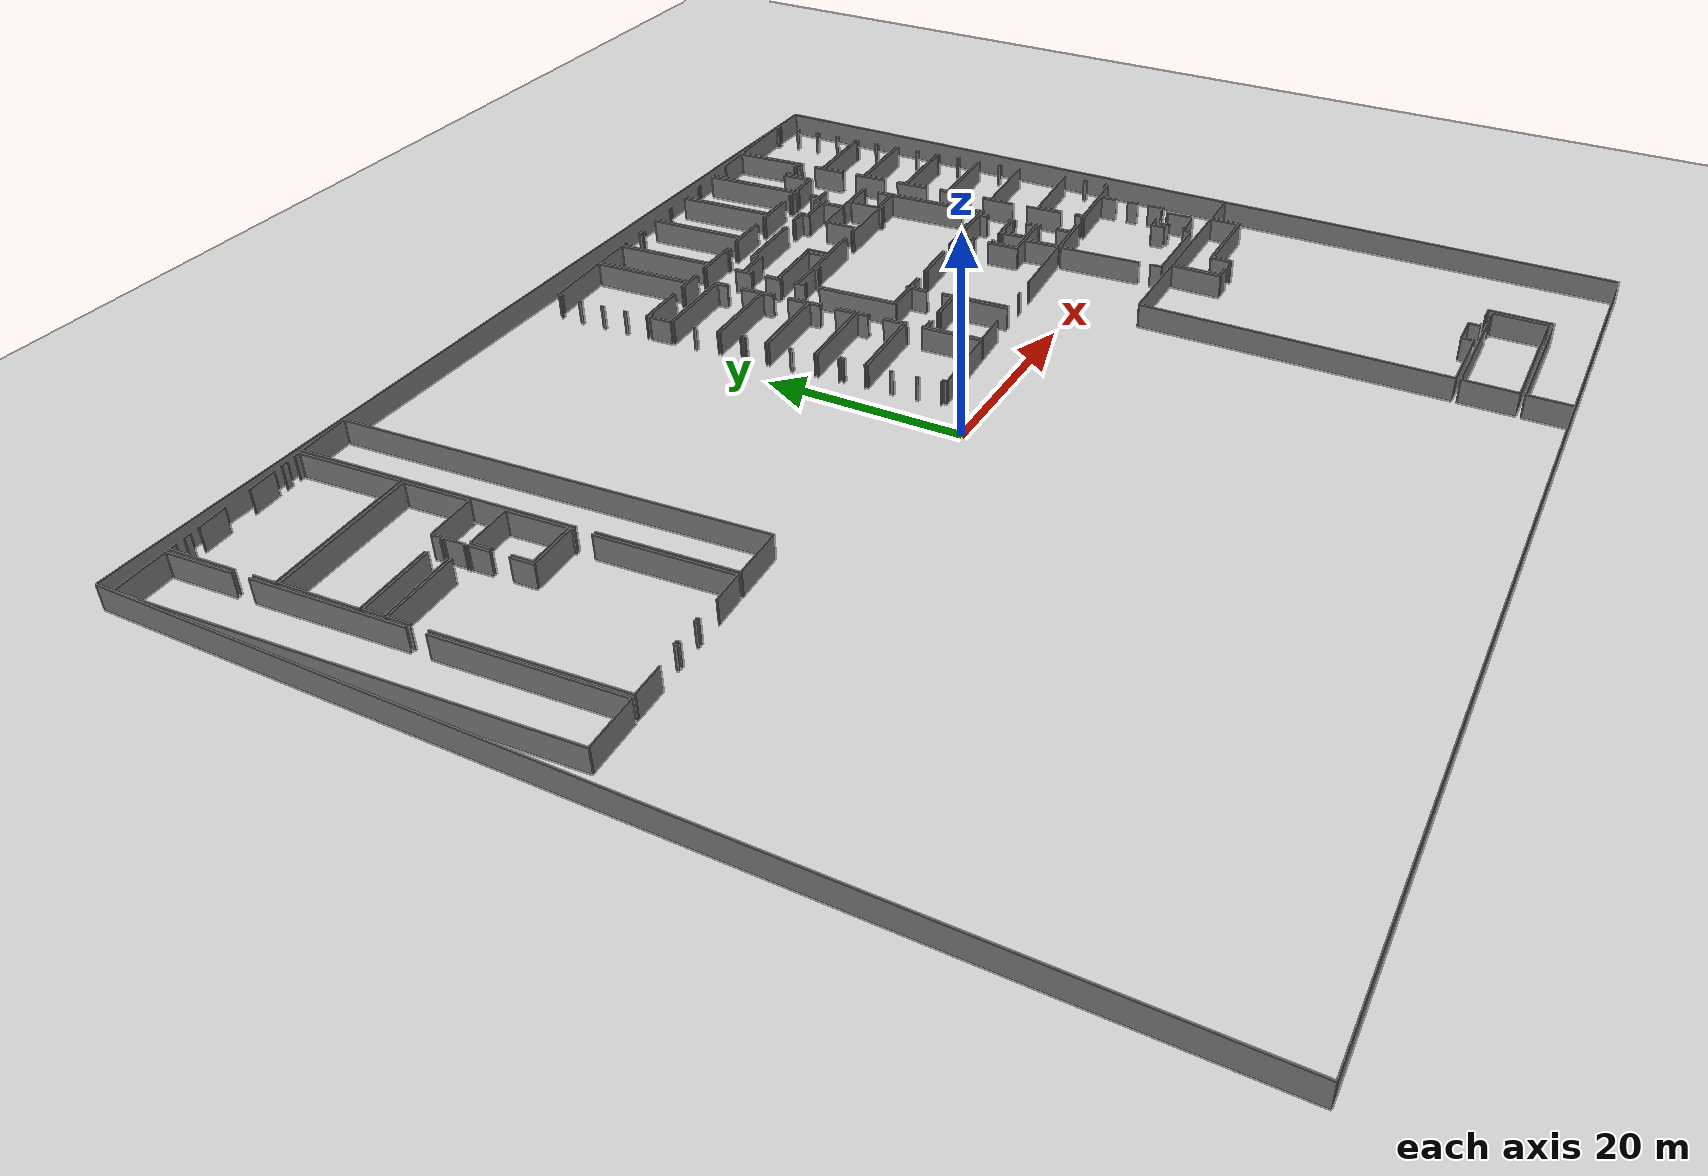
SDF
<sdf version="1.6">
  <world name="default">
    <light name="sun" type="directional">
      <cast_shadows>1</cast_shadows>
      <pose frame="">0 0 10 0 -0 0</pose>
      <diffuse>0.8 0.8 0.8 1</diffuse>
      <specular>0.1 0.1 0.1 1</specular>
      <attenuation>
        <range>1000</range>
        <constant>0.9</constant>
        <linear>0.01</linear>
        <quadratic>0.001</quadratic>
      </attenuation>
      <direction>-0.5 0.5 -1</direction>
    </light>
    <model name="ground_plane">
      <static>1</static>
      <link name="link">
        <collision name="collision">
          <geometry>
            <plane>
              <normal>0 0 1</normal>
              <size>100 100</size>
            </plane>
          </geometry>
          <surface>
            <friction>
              <ode>
                <mu>100</mu>
                <mu2>50</mu2>
              </ode>
              <torsional>
                <ode />
              </torsional>
            </friction>
            <contact>
              <ode />
            </contact>
            <bounce />
          </surface>
          <max_contacts>10</max_contacts>
        </collision>
        <visual name="visual">
          <cast_shadows>0</cast_shadows>
          <geometry>
            <plane>
              <normal>0 0 1</normal>
              <size>100 100</size>
            </plane>
          </geometry>
          <material>
            <script>
              <uri>file://media/materials/scripts/gazebo.material</uri>
              <name>Gazebo/Grey</name>
            </script>
          </material>
        </visual>
        <self_collide>0</self_collide>
        <kinematic>0</kinematic>
        <gravity>1</gravity>
      </link>
    </model>
    <gravity>0 0 -9.8</gravity>
    <magnetic_field>6e-06 2.3e-05 -4.2e-05</magnetic_field>
    <atmosphere type="adiabatic" />
    <physics default="0" name="default_physics" type="ode">
      <max_step_size>0.001</max_step_size>
      <real_time_factor>1</real_time_factor>
      <real_time_update_rate>1000</real_time_update_rate>
    </physics>
    <scene>
      <ambient>0.4 0.4 0.4 1</ambient>
      <background>0.7 0.7 0.7 1</background>
      <shadows>1</shadows>
    </scene>
    <spherical_coordinates>
      <surface_model>EARTH_WGS84</surface_model>
      <latitude_deg>0</latitude_deg>
      <longitude_deg>0</longitude_deg>
      <elevation>0</elevation>
      <heading_deg>0</heading_deg>
    </spherical_coordinates>
  <model name="50025633">
		<static>1</static>
		<link name="Wall_0">
			<collision name="Wall_0_Collision">
				<geometry>
					<box>
						<size>0.969436459965 0.1 2.5</size>
					</box>
				</geometry>
				<pose frame="">0.484718229982 0 1.25 0 0 0</pose>
			</collision>
			<visual name="Wall_0_Visual">
				<pose frame="">0.484718229982 0 1.25 0 0 0</pose>
				<geometry>
					<box>
						<size>0.969436459965 0.1 2.5</size>
					</box>
				</geometry>
				<material>
					<script>
						<uri>file://media/materials/scripts/gazebo.material</uri>
						<name>Gazebo/Grey</name>
					</script>
					<ambient>1 1 1 1</ambient>
				</material>
			</visual>
			<pose frame="">59.5283012875 -12.5141427038 0 0 0 -3.05907173526</pose>
		</link>
		<link name="Wall_1">
			<collision name="Wall_1_Collision">
				<geometry>
					<box>
						<size>4.89840338192 0.1 2.5</size>
					</box>
				</geometry>
				<pose frame="">2.44920169096 0 1.25 0 0 0</pose>
			</collision>
			<visual name="Wall_1_Visual">
				<pose frame="">2.44920169096 0 1.25 0 0 0</pose>
				<geometry>
					<box>
						<size>4.89840338192 0.1 2.5</size>
					</box>
				</geometry>
				<material>
					<script>
						<uri>file://media/materials/scripts/gazebo.material</uri>
						<name>Gazebo/Grey</name>
					</script>
					<ambient>1 1 1 1</ambient>
				</material>
			</visual>
			<pose frame="">56.970228227 -12.6720531534 0 0 0 -3.07837304394</pose>
		</link>
		<link name="Wall_2">
			<collision name="Wall_2_Collision">
				<geometry>
					<box>
						<size>0.39960573099 0.1 2.5</size>
					</box>
				</geometry>
				<pose frame="">0.199802865495 0 1.25 0 0 0</pose>
			</collision>
			<visual name="Wall_2_Visual">
				<pose frame="">0.199802865495 0 1.25 0 0 0</pose>
				<geometry>
					<box>
						<size>0.39960573099 0.1 2.5</size>
					</box>
				</geometry>
				<material>
					<script>
						<uri>file://media/materials/scripts/gazebo.material</uri>
						<name>Gazebo/Grey</name>
					</script>
					<ambient>1 1 1 1</ambient>
				</material>
			</visual>
			<pose frame="">51.9773106948 -10.8397583703 0 0 0 1.58891834909</pose>
		</link>
		<link name="Wall_3">
			<collision name="Wall_3_Collision">
				<geometry>
					<box>
						<size>0.38551686731 0.1 2.5</size>
					</box>
				</geometry>
				<pose frame="">0.192758433655 0 1.25 0 0 0</pose>
			</collision>
			<visual name="Wall_3_Visual">
				<pose frame="">0.192758433655 0 1.25 0 0 0</pose>
				<geometry>
					<box>
						<size>0.38551686731 0.1 2.5</size>
					</box>
				</geometry>
				<material>
					<script>
						<uri>file://media/materials/scripts/gazebo.material</uri>
						<name>Gazebo/Grey</name>
					</script>
					<ambient>1 1 1 1</ambient>
				</material>
			</visual>
			<pose frame="">51.8225762397 -8.25081464261 0 0 0 1.60342569152</pose>
		</link>
		<link name="Wall_4">
			<collision name="Wall_4_Collision">
				<geometry>
					<box>
						<size>0.398091356513 0.1 2.5</size>
					</box>
				</geometry>
				<pose frame="">0.199045678256 0 1.25 0 0 0</pose>
			</collision>
			<visual name="Wall_4_Visual">
				<pose frame="">0.199045678256 0 1.25 0 0 0</pose>
				<geometry>
					<box>
						<size>0.398091356513 0.1 2.5</size>
					</box>
				</geometry>
				<material>
					<script>
						<uri>file://media/materials/scripts/gazebo.material</uri>
						<name>Gazebo/Grey</name>
					</script>
					<ambient>1 1 1 1</ambient>
				</material>
			</visual>
			<pose frame="">51.6773697683 -5.69274158203 0 0 0 1.60271396404</pose>
		</link>
		<link name="Wall_5">
			<collision name="Wall_5_Collision">
				<geometry>
					<box>
						<size>0.392351935738 0.1 2.5</size>
					</box>
				</geometry>
				<pose frame="">0.196175967869 0 1.25 0 0 0</pose>
			</collision>
			<visual name="Wall_5_Visual">
				<pose frame="">0.196175967869 0 1.25 0 0 0</pose>
				<geometry>
					<box>
						<size>0.392351935738 0.1 2.5</size>
					</box>
				</geometry>
				<material>
					<script>
						<uri>file://media/materials/scripts/gazebo.material</uri>
						<name>Gazebo/Grey</name>
					</script>
					<ambient>1 1 1 1</ambient>
				</material>
			</visual>
			<pose frame="">51.5258113078 -3.14102051057 0 0 0 0.0644789553313</pose>
		</link>
		<link name="Wall_6">
			<collision name="Wall_6_Collision">
				<geometry>
					<box>
						<size>0.423217186138 0.1 2.5</size>
					</box>
				</geometry>
				<pose frame="">0.211608593069 0 1.25 0 0 0</pose>
			</collision>
			<visual name="Wall_6_Visual">
				<pose frame="">0.211608593069 0 1.25 0 0 0</pose>
				<geometry>
					<box>
						<size>0.423217186138 0.1 2.5</size>
					</box>
				</geometry>
				<material>
					<script>
						<uri>file://media/materials/scripts/gazebo.material</uri>
						<name>Gazebo/Grey</name>
					</script>
					<ambient>1 1 1 1</ambient>
				</material>
			</visual>
			<pose frame="">51.9173479175 -3.11573959385 0 0 0 1.58580570694</pose>
		</link>
		<link name="Wall_7">
			<collision name="Wall_7_Collision">
				<geometry>
					<box>
						<size>6.99771601938 0.1 2.5</size>
					</box>
				</geometry>
				<pose frame="">3.49885800969 0 1.25 0 0 0</pose>
			</collision>
			<visual name="Wall_7_Visual">
				<pose frame="">3.49885800969 0 1.25 0 0 0</pose>
				<geometry>
					<box>
						<size>6.99771601938 0.1 2.5</size>
					</box>
				</geometry>
				<material>
					<script>
						<uri>file://media/materials/scripts/gazebo.material</uri>
						<name>Gazebo/Grey</name>
					</script>
					<ambient>1 1 1 1</ambient>
				</material>
			</visual>
			<pose frame="">51.9109959284 -2.69257007832 0 0 0 0.0586998542074</pose>
		</link>
		<link name="Wall_8">
			<collision name="Wall_8_Collision">
				<geometry>
					<box>
						<size>10.2515792055 0.1 2.5</size>
					</box>
				</geometry>
				<pose frame="">5.12578960273 0 1.25 0 0 0</pose>
			</collision>
			<visual name="Wall_8_Visual">
				<pose frame="">5.12578960273 0 1.25 0 0 0</pose>
				<geometry>
					<box>
						<size>10.2515792055 0.1 2.5</size>
					</box>
				</geometry>
				<material>
					<script>
						<uri>file://media/materials/scripts/gazebo.material</uri>
						<name>Gazebo/Grey</name>
					</script>
					<ambient>1 1 1 1</ambient>
				</material>
			</visual>
			<pose frame="">58.8966594889 -2.28204102115 0 0 0 -1.50914317851</pose>
		</link>
		<link name="Wall_9">
			<collision name="Wall_9_Collision">
				<geometry>
					<box>
						<size>0.957259403958 0.1 2.5</size>
					</box>
				</geometry>
				<pose frame="">0.478629701979 0 1.25 0 0 0</pose>
			</collision>
			<visual name="Wall_9_Visual">
				<pose frame="">0.478629701979 0 1.25 0 0 0</pose>
				<geometry>
					<box>
						<size>0.957259403958 0.1 2.5</size>
					</box>
				</geometry>
				<material>
					<script>
						<uri>file://media/materials/scripts/gazebo.material</uri>
						<name>Gazebo/Grey</name>
					</script>
					<ambient>1 1 1 1</ambient>
				</material>
			</visual>
			<pose frame="">63.7411945551 -12.2488836379 0 0 0 -3.08037420395</pose>
		</link>
		<link name="Wall_10">
			<collision name="Wall_10_Collision">
				<geometry>
					<box>
						<size>1.39302038249 0.1 2.5</size>
					</box>
				</geometry>
				<pose frame="">0.696510191243 0 1.25 0 0 0</pose>
			</collision>
			<visual name="Wall_10_Visual">
				<pose frame="">0.696510191243 0 1.25 0 0 0</pose>
				<geometry>
					<box>
						<size>1.39302038249 0.1 2.5</size>
					</box>
				</geometry>
				<material>
					<script>
						<uri>file://media/materials/scripts/gazebo.material</uri>
						<name>Gazebo/Grey</name>
					</script>
					<ambient>1 1 1 1</ambient>
				</material>
			</visual>
			<pose frame="">61.202685621 -12.3990446608 0 0 0 -3.07935588312</pose>
		</link>
		<link name="Wall_11">
			<collision name="Wall_11_Collision">
				<geometry>
					<box>
						<size>10.2055584932 0.1 2.5</size>
					</box>
				</geometry>
				<pose frame="">5.10277924658 0 1.25 0 0 0</pose>
			</collision>
			<visual name="Wall_11_Visual">
				<pose frame="">5.10277924658 0 1.25 0 0 0</pose>
				<geometry>
					<box>
						<size>10.2055584932 0.1 2.5</size>
					</box>
				</geometry>
				<material>
					<script>
						<uri>file://media/materials/scripts/gazebo.material</uri>
						<name>Gazebo/Grey</name>
					</script>
					<ambient>1 1 1 1</ambient>
				</material>
			</visual>
			<pose frame="">59.8123622412 -12.4856857925 0 0 0 1.63323920801</pose>
		</link>
		<link name="Wall_12">
			<collision name="Wall_12_Collision">
				<geometry>
					<box>
						<size>3.95240272326 0.1 2.5</size>
					</box>
				</geometry>
				<pose frame="">1.97620136163 0 1.25 0 0 0</pose>
			</collision>
			<visual name="Wall_12_Visual">
				<pose frame="">1.97620136163 0 1.25 0 0 0</pose>
				<geometry>
					<box>
						<size>3.95240272326 0.1 2.5</size>
					</box>
				</geometry>
				<material>
					<script>
						<uri>file://media/materials/scripts/gazebo.material</uri>
						<name>Gazebo/Grey</name>
					</script>
					<ambient>1 1 1 1</ambient>
				</material>
			</visual>
			<pose frame="">59.1755118115 -2.30001715037 0 0 0 0.0649186328604</pose>
		</link>
		<link name="Wall_13">
			<collision name="Wall_13_Collision">
				<geometry>
					<box>
						<size>10.2241844338 0.1 2.5</size>
					</box>
				</geometry>
				<pose frame="">5.11209221692 0 1.25 0 0 0</pose>
			</collision>
			<visual name="Wall_13_Visual">
				<pose frame="">5.11209221692 0 1.25 0 0 0</pose>
				<geometry>
					<box>
						<size>10.2241844338 0.1 2.5</size>
					</box>
				</geometry>
				<material>
					<script>
						<uri>file://media/materials/scripts/gazebo.material</uri>
						<name>Gazebo/Grey</name>
					</script>
					<ambient>1 1 1 1</ambient>
				</material>
			</visual>
			<pose frame="">63.1195888993 -2.04361275733 0 0 0 -1.50996123104</pose>
		</link>
		<link name="Wall_14">
			<collision name="Wall_14_Collision">
				<geometry>
					<box>
						<size>0.938079922065 0.1 2.5</size>
					</box>
				</geometry>
				<pose frame="">0.469039961033 0 1.25 0 0 0</pose>
			</collision>
			<visual name="Wall_14_Visual">
				<pose frame="">0.469039961033 0 1.25 0 0 0</pose>
				<geometry>
					<box>
						<size>0.938079922065 0.1 2.5</size>
					</box>
				</geometry>
				<material>
					<script>
						<uri>file://media/materials/scripts/gazebo.material</uri>
						<name>Gazebo/Grey</name>
					</script>
					<ambient>1 1 1 1</ambient>
				</material>
			</visual>
			<pose frame="">70.1288818594 -11.8567118293 0 0 0 -3.07545689106</pose>
		</link>
		<link name="Wall_15">
			<collision name="Wall_15_Collision">
				<geometry>
					<box>
						<size>3.58060873368 0.1 2.5</size>
					</box>
				</geometry>
				<pose frame="">1.79030436684 0 1.25 0 0 0</pose>
			</collision>
			<visual name="Wall_15_Visual">
				<pose frame="">1.79030436684 0 1.25 0 0 0</pose>
				<geometry>
					<box>
						<size>3.58060873368 0.1 2.5</size>
					</box>
				</geometry>
				<material>
					<script>
						<uri>file://media/materials/scripts/gazebo.material</uri>
						<name>Gazebo/Grey</name>
					</script>
					<ambient>1 1 1 1</ambient>
				</material>
			</visual>
			<pose frame="">67.6002820283 -12.0214824272 0 0 0 -3.08511404785</pose>
		</link>
		<link name="Wall_16">
			<collision name="Wall_16_Collision">
				<geometry>
					<box>
						<size>10.2271120577 0.1 2.5</size>
					</box>
				</geometry>
				<pose frame="">5.11355602885 0 1.25 0 0 0</pose>
			</collision>
			<visual name="Wall_16_Visual">
				<pose frame="">5.11355602885 0 1.25 0 0 0</pose>
				<geometry>
					<box>
						<size>10.2271120577 0.1 2.5</size>
					</box>
				</geometry>
				<material>
					<script>
						<uri>file://media/materials/scripts/gazebo.material</uri>
						<name>Gazebo/Grey</name>
					</script>
					<ambient>1 1 1 1</ambient>
				</material>
			</visual>
			<pose frame="">64.0253825485 -12.2236027212 0 0 0 1.63258471512</pose>
		</link>
		<link name="Wall_17">
			<collision name="Wall_17_Collision">
				<geometry>
					<box>
						<size>0.477315919187 0.1 2.5</size>
					</box>
				</geometry>
				<pose frame="">0.238657959593 0 1.25 0 0 0</pose>
			</collision>
			<visual name="Wall_17_Visual">
				<pose frame="">0.238657959593 0 1.25 0 0 0</pose>
				<geometry>
					<box>
						<size>0.477315919187 0.1 2.5</size>
					</box>
				</geometry>
				<material>
					<script>
						<uri>file://media/materials/scripts/gazebo.material</uri>
						<name>Gazebo/Grey</name>
					</script>
					<ambient>1 1 1 1</ambient>
				</material>
			</visual>
			<pose frame="">63.3938677897 -2.0160070126 0 0 0 0.0700559247163</pose>
		</link>
		<link name="Wall_18">
			<collision name="Wall_18_Collision">
				<geometry>
					<box>
						<size>0.398716292036 0.1 2.5</size>
					</box>
				</geometry>
				<pose frame="">0.199358146018 0 1.25 0 0 0</pose>
			</collision>
			<visual name="Wall_18_Visual">
				<pose frame="">0.199358146018 0 1.25 0 0 0</pose>
				<geometry>
					<box>
						<size>0.398716292036 0.1 2.5</size>
					</box>
				</geometry>
				<material>
					<script>
						<uri>file://media/materials/scripts/gazebo.material</uri>
						<name>Gazebo/Grey</name>
					</script>
					<ambient>1 1 1 1</ambient>
				</material>
			</visual>
			<pose frame="">66.4381220979 -1.82096283451 0 0 0 -1.50734798673</pose>
		</link>
		<link name="Wall_19">
			<collision name="Wall_19_Collision">
				<geometry>
					<box>
						<size>0.436477734711 0.1 2.5</size>
					</box>
				</geometry>
				<pose frame="">0.218238867355 0 1.25 0 0 0</pose>
			</collision>
			<visual name="Wall_19_Visual">
				<pose frame="">0.218238867355 0 1.25 0 0 0</pose>
				<geometry>
					<box>
						<size>0.436477734711 0.1 2.5</size>
					</box>
				</geometry>
				<material>
					<script>
						<uri>file://media/materials/scripts/gazebo.material</uri>
						<name>Gazebo/Grey</name>
					</script>
					<ambient>1 1 1 1</ambient>
				</material>
			</visual>
			<pose frame="">66.4634030147 -2.21887684128 0 0 0 0.0578944140467</pose>
		</link>
		<link name="Wall_20">
			<collision name="Wall_20_Collision">
				<geometry>
					<box>
						<size>0.39796269521 0.1 2.5</size>
					</box>
				</geometry>
				<pose frame="">0.198981347605 0 1.25 0 0 0</pose>
			</collision>
			<visual name="Wall_20_Visual">
				<pose frame="">0.198981347605 0 1.25 0 0 0</pose>
				<geometry>
					<box>
						<size>0.39796269521 0.1 2.5</size>
					</box>
				</geometry>
				<material>
					<script>
						<uri>file://media/materials/scripts/gazebo.material</uri>
						<name>Gazebo/Grey</name>
					</script>
					<ambient>1 1 1 1</ambient>
				</material>
			</visual>
			<pose frame="">66.8991494687 -2.19362133252 0 0 0 1.58643900711</pose>
		</link>
		<link name="Wall_21">
			<collision name="Wall_21_Collision">
				<geometry>
					<box>
						<size>10.2370171481 0.1 2.5</size>
					</box>
				</geometry>
				<pose frame="">5.11850857406 0 1.25 0 0 0</pose>
			</collision>
			<visual name="Wall_21_Visual">
				<pose frame="">5.11850857406 0 1.25 0 0 0</pose>
				<geometry>
					<box>
						<size>10.2370171481 0.1 2.5</size>
					</box>
				</geometry>
				<material>
					<script>
						<uri>file://media/materials/scripts/gazebo.material</uri>
						<name>Gazebo/Grey</name>
					</script>
					<ambient>1 1 1 1</ambient>
				</material>
			</visual>
			<pose frame="">69.5203613011 -1.63779687609 0 0 0 -1.51131811286</pose>
		</link>
		<link name="Wall_22">
			<collision name="Wall_22_Collision">
				<geometry>
					<box>
						<size>0.977506399178 0.1 2.5</size>
					</box>
				</geometry>
				<pose frame="">0.488753199589 0 1.25 0 0 0</pose>
			</collision>
			<visual name="Wall_22_Visual">
				<pose frame="">0.488753199589 0 1.25 0 0 0</pose>
				<geometry>
					<box>
						<size>0.977506399178 0.1 2.5</size>
					</box>
				</geometry>
				<material>
					<script>
						<uri>file://media/materials/scripts/gazebo.material</uri>
						<name>Gazebo/Grey</name>
					</script>
					<ambient>1 1 1 1</ambient>
				</material>
			</visual>
			<pose frame="">76.1431992428 -11.4862638235 0 0 0 -3.080211524</pose>
		</link>
		<link name="Wall_23">
			<collision name="Wall_23_Collision">
				<geometry>
					<box>
						<size>3.18343379874 0.1 2.5</size>
					</box>
				</geometry>
				<pose frame="">1.59171689937 0 1.25 0 0 0</pose>
			</collision>
			<visual name="Wall_23_Visual">
				<pose frame="">1.59171689937 0 1.25 0 0 0</pose>
				<geometry>
					<box>
						<size>3.18343379874 0.1 2.5</size>
					</box>
				</geometry>
				<material>
					<script>
						<uri>file://media/materials/scripts/gazebo.material</uri>
						<name>Gazebo/Grey</name>
					</script>
					<ambient>1 1 1 1</ambient>
				</material>
			</visual>
			<pose frame="">73.6069770249 -11.6361707669 0 0 0 -3.07805863666</pose>
		</link>
		<link name="Wall_24">
			<collision name="Wall_24_Collision">
				<geometry>
					<box>
						<size>10.2492937083 0.1 2.5</size>
					</box>
				</geometry>
				<pose frame="">5.12464685417 0 1.25 0 0 0</pose>
			</collision>
			<visual name="Wall_24_Visual">
				<pose frame="">5.12464685417 0 1.25 0 0 0</pose>
				<geometry>
					<box>
						<size>10.2492937083 0.1 2.5</size>
					</box>
				</geometry>
				<material>
					<script>
						<uri>file://media/materials/scripts/gazebo.material</uri>
						<name>Gazebo/Grey</name>
					</script>
					<ambient>1 1 1 1</ambient>
				</material>
			</visual>
			<pose frame="">70.4299661439 -11.8382910608 0 0 0 1.63138285958</pose>
		</link>
		<link name="Wall_25">
			<collision name="Wall_25_Collision">
				<geometry>
					<box>
						<size>0.422264637513 0.1 2.5</size>
					</box>
				</geometry>
				<pose frame="">0.211132318757 0 1.25 0 0 0</pose>
			</collision>
			<visual name="Wall_25_Visual">
				<pose frame="">0.211132318757 0 1.25 0 0 0</pose>
				<geometry>
					<box>
						<size>0.422264637513 0.1 2.5</size>
					</box>
				</geometry>
				<material>
					<script>
						<uri>file://media/materials/scripts/gazebo.material</uri>
						<name>Gazebo/Grey</name>
					</script>
					<ambient>1 1 1 1</ambient>
				</material>
			</visual>
			<pose frame="">72.4387191849 -1.45526611658 0 0 0 0.0688595942033</pose>
		</link>
		<link name="Wall_26">
			<collision name="Wall_26_Collision">
				<geometry>
					<box>
						<size>10.2412191776 0.1 2.5</size>
					</box>
				</geometry>
				<pose frame="">5.12060958881 0 1.25 0 0 0</pose>
			</collision>
			<visual name="Wall_26_Visual">
				<pose frame="">5.12060958881 0 1.25 0 0 0</pose>
				<geometry>
					<box>
						<size>10.2412191776 0.1 2.5</size>
					</box>
				</geometry>
				<material>
					<script>
						<uri>file://media/materials/scripts/gazebo.material</uri>
						<name>Gazebo/Grey</name>
					</script>
					<ambient>1 1 1 1</ambient>
				</material>
			</visual>
			<pose frame="">75.501775381 -1.26515108206 0 0 0 -1.50812371461</pose>
		</link>
		<link name="Wall_27">
			<collision name="Wall_27_Collision">
				<geometry>
					<box>
						<size>0.972380827445 0.1 2.5</size>
					</box>
				</geometry>
				<pose frame="">0.486190413722 0 1.25 0 0 0</pose>
			</collision>
			<visual name="Wall_27_Visual">
				<pose frame="">0.486190413722 0 1.25 0 0 0</pose>
				<geometry>
					<box>
						<size>0.972380827445 0.1 2.5</size>
					</box>
				</geometry>
				<material>
					<script>
						<uri>file://media/materials/scripts/gazebo.material</uri>
						<name>Gazebo/Grey</name>
					</script>
					<ambient>1 1 1 1</ambient>
				</material>
			</visual>
			<pose frame="">82.1318545903 -11.1329661884 0 0 0 -3.08525348964</pose>
		</link>
		<link name="Wall_28">
			<collision name="Wall_28_Collision">
				<geometry>
					<box>
						<size>3.14222034256 0.1 2.5</size>
					</box>
				</geometry>
				<pose frame="">1.57111017128 0 1.25 0 0 0</pose>
			</collision>
			<visual name="Wall_28_Visual">
				<pose frame="">1.57111017128 0 1.25 0 0 0</pose>
				<geometry>
					<box>
						<size>3.14222034256 0.1 2.5</size>
					</box>
				</geometry>
				<material>
					<script>
						<uri>file://media/materials/scripts/gazebo.material</uri>
						<name>Gazebo/Grey</name>
					</script>
					<ambient>1 1 1 1</ambient>
				</material>
			</visual>
			<pose frame="">79.5598071536 -11.2828731317 0 0 0 -3.08532491945</pose>
		</link>
		<link name="Wall_29">
			<collision name="Wall_29_Collision">
				<geometry>
					<box>
						<size>10.2571789274 0.1 2.5</size>
					</box>
				</geometry>
				<pose frame="">5.1285894637 0 1.25 0 0 0</pose>
			</collision>
			<visual name="Wall_29_Visual">
				<pose frame="">5.1285894637 0 1.25 0 0 0</pose>
				<geometry>
					<box>
						<size>10.2571789274 0.1 2.5</size>
					</box>
				</geometry>
				<material>
					<script>
						<uri>file://media/materials/scripts/gazebo.material</uri>
						<name>Gazebo/Grey</name>
					</script>
					<ambient>1 1 1 1</ambient>
				</material>
			</visual>
			<pose frame="">76.4225597246 -11.4595854692 0 0 0 1.63334647593</pose>
		</link>
		<link name="Wall_30">
			<collision name="Wall_30_Collision">
				<geometry>
					<box>
						<size>0.410088114194 0.1 2.5</size>
					</box>
				</geometry>
				<pose frame="">0.205044057097 0 1.25 0 0 0</pose>
			</collision>
			<visual name="Wall_30_Visual">
				<pose frame="">0.205044057097 0 1.25 0 0 0</pose>
				<geometry>
					<box>
						<size>0.410088114194 0.1 2.5</size>
					</box>
				</geometry>
				<material>
					<script>
						<uri>file://media/materials/scripts/gazebo.material</uri>
						<name>Gazebo/Grey</name>
					</script>
					<ambient>1 1 1 1</ambient>
				</material>
			</visual>
			<pose frame="">78.4376647547 -1.08046064625 0 0 0 0.0611279695019</pose>
		</link>
		<link name="Wall_31">
			<collision name="Wall_31_Collision">
				<geometry>
					<box>
						<size>10.2647523739 0.1 2.5</size>
					</box>
				</geometry>
				<pose frame="">5.13237618697 0 1.25 0 0 0</pose>
			</collision>
			<visual name="Wall_31_Visual">
				<pose frame="">5.13237618697 0 1.25 0 0 0</pose>
				<geometry>
					<box>
						<size>10.2647523739 0.1 2.5</size>
					</box>
				</geometry>
				<material>
					<script>
						<uri>file://media/materials/scripts/gazebo.material</uri>
						<name>Gazebo/Grey</name>
					</script>
					<ambient>1 1 1 1</ambient>
				</material>
			</visual>
			<pose frame="">81.4262756382 -0.892492584053 0 0 0 -1.50200404181</pose>
		</link>
		<link name="Wall_32">
			<collision name="Wall_32_Collision">
				<geometry>
					<box>
						<size>3.23218013585 0.1 2.5</size>
					</box>
				</geometry>
				<pose frame="">1.61609006792 0 1.25 0 0 0</pose>
			</collision>
			<visual name="Wall_32_Visual">
				<pose frame="">1.61609006792 0 1.25 0 0 0</pose>
				<geometry>
					<box>
						<size>3.23218013585 0.1 2.5</size>
					</box>
				</geometry>
				<material>
					<script>
						<uri>file://media/materials/scripts/gazebo.material</uri>
						<name>Gazebo/Grey</name>
					</script>
					<ambient>1 1 1 1</ambient>
				</material>
			</visual>
			<pose frame="">85.6129987105 -10.9204286322 0 0 0 -3.08602656118</pose>
		</link>
		<link name="Wall_33">
			<collision name="Wall_33_Collision">
				<geometry>
					<box>
						<size>9.83225560325 0.1 2.5</size>
					</box>
				</geometry>
				<pose frame="">4.91612780163 0 1.25 0 0 0</pose>
			</collision>
			<visual name="Wall_33_Visual">
				<pose frame="">4.91612780163 0 1.25 0 0 0</pose>
				<geometry>
					<box>
						<size>9.83225560325 0.1 2.5</size>
					</box>
				</geometry>
				<material>
					<script>
						<uri>file://media/materials/scripts/gazebo.material</uri>
						<name>Gazebo/Grey</name>
					</script>
					<ambient>1 1 1 1</ambient>
				</material>
			</visual>
			<pose frame="">82.3858071155 -11.0999358449 0 0 0 1.62858408503</pose>
		</link>
		<link name="Wall_34">
			<collision name="Wall_34_Collision">
				<geometry>
					<box>
						<size>0.0886448327981 0.1 2.5</size>
					</box>
				</geometry>
				<pose frame="">0.044322416399 0 1.25 0 0 0</pose>
			</collision>
			<visual name="Wall_34_Visual">
				<pose frame="">0.044322416399 0 1.25 0 0 0</pose>
				<geometry>
					<box>
						<size>0.0886448327981 0.1 2.5</size>
					</box>
				</geometry>
				<material>
					<script>
						<uri>file://media/materials/scripts/gazebo.material</uri>
						<name>Gazebo/Grey</name>
					</script>
					<ambient>1 1 1 1</ambient>
				</material>
			</visual>
			<pose frame="">81.8179392877 -1.28409271363 0 0 0 -0.0712870434941</pose>
		</link>
		<link name="Wall_35">
			<collision name="Wall_35_Collision">
				<geometry>
					<box>
						<size>0.431172528495 0.1 2.5</size>
					</box>
				</geometry>
				<pose frame="">0.215586264247 0 1.25 0 0 0</pose>
			</collision>
			<visual name="Wall_35_Visual">
				<pose frame="">0.215586264247 0 1.25 0 0 0</pose>
				<geometry>
					<box>
						<size>0.431172528495 0.1 2.5</size>
					</box>
				</geometry>
				<material>
					<script>
						<uri>file://media/materials/scripts/gazebo.material</uri>
						<name>Gazebo/Grey</name>
					</script>
					<ambient>1 1 1 1</ambient>
				</material>
			</visual>
			<pose frame="">81.9063589763 -1.29040659082 0 0 0 1.65900742222</pose>
		</link>
		<link name="Wall_36">
			<collision name="Wall_36_Collision">
				<geometry>
					<box>
						<size>3.73860603192 0.1 2.5</size>
					</box>
				</geometry>
				<pose frame="">1.86930301596 0 1.25 0 0 0</pose>
			</collision>
			<visual name="Wall_36_Visual">
				<pose frame="">1.86930301596 0 1.25 0 0 0</pose>
				<geometry>
					<box>
						<size>3.73860603192 0.1 2.5</size>
					</box>
				</geometry>
				<material>
					<script>
						<uri>file://media/materials/scripts/gazebo.material</uri>
						<name>Gazebo/Grey</name>
					</script>
					<ambient>1 1 1 1</ambient>
				</material>
			</visual>
			<pose frame="">84.4279716193 -0.714471736824 0 0 0 0.0562980799925</pose>
		</link>
		<link name="Wall_37">
			<collision name="Wall_37_Collision">
				<geometry>
					<box>
						<size>7.18325854843 0.1 2.5</size>
					</box>
				</geometry>
				<pose frame="">3.59162927421 0 1.25 0 0 0</pose>
			</collision>
			<visual name="Wall_37_Visual">
				<pose frame="">3.59162927421 0 1.25 0 0 0</pose>
				<geometry>
					<box>
						<size>7.18325854843 0.1 2.5</size>
					</box>
				</geometry>
				<material>
					<script>
						<uri>file://media/materials/scripts/gazebo.material</uri>
						<name>Gazebo/Grey</name>
					</script>
					<ambient>1 1 1 1</ambient>
				</material>
			</visual>
			<pose frame="">88.160654509 -0.50410656097 0 0 0 -1.50329243491</pose>
		</link>
		<link name="Wall_38">
			<collision name="Wall_38_Collision">
				<geometry>
					<box>
						<size>0.864491419705 0.1 2.5</size>
					</box>
				</geometry>
				<pose frame="">0.432245709852 0 1.25 0 0 0</pose>
			</collision>
			<visual name="Wall_38_Visual">
				<pose frame="">0.432245709852 0 1.25 0 0 0</pose>
				<geometry>
					<box>
						<size>0.864491419705 0.1 2.5</size>
					</box>
				</geometry>
				<material>
					<script>
						<uri>file://media/materials/scripts/gazebo.material</uri>
						<name>Gazebo/Grey</name>
					</script>
					<ambient>1 1 1 1</ambient>
				</material>
			</visual>
			<pose frame="">88.6451842394 -7.67100507524 0 0 0 -3.04474612614</pose>
		</link>
		<link name="Wall_39">
			<collision name="Wall_39_Collision">
				<geometry>
					<box>
						<size>0.778459122221 0.1 2.5</size>
					</box>
				</geometry>
				<pose frame="">0.389229561111 0 1.25 0 0 0</pose>
			</collision>
			<visual name="Wall_39_Visual">
				<pose frame="">0.389229561111 0 1.25 0 0 0</pose>
				<geometry>
					<box>
						<size>0.778459122221 0.1 2.5</size>
					</box>
				</geometry>
				<material>
					<script>
						<uri>file://media/materials/scripts/gazebo.material</uri>
						<name>Gazebo/Grey</name>
					</script>
					<ambient>1 1 1 1</ambient>
				</material>
			</visual>
			<pose frame="">86.1893782038 -7.86321626617 0 0 0 -3.07724986853</pose>
		</link>
		<link name="Wall_40">
			<collision name="Wall_40_Collision">
				<geometry>
					<box>
						<size>3.01383329463 0.1 2.5</size>
					</box>
				</geometry>
				<pose frame="">1.50691664731 0 1.25 0 0 0</pose>
			</collision>
			<visual name="Wall_40_Visual">
				<pose frame="">1.50691664731 0 1.25 0 0 0</pose>
				<geometry>
					<box>
						<size>3.01383329463 0.1 2.5</size>
					</box>
				</geometry>
				<material>
					<script>
						<uri>file://media/materials/scripts/gazebo.material</uri>
						<name>Gazebo/Grey</name>
					</script>
					<ambient>1 1 1 1</ambient>
				</material>
			</visual>
			<pose frame="">85.4125299337 -7.91326994048 0 0 0 -1.50423096694</pose>
		</link>
		<link name="Wall_41">
			<collision name="Wall_41_Collision">
				<geometry>
					<box>
						<size>0.353597451561 0.1 2.5</size>
					</box>
				</geometry>
				<pose frame="">0.17679872578 0 1.25 0 0 0</pose>
			</collision>
			<visual name="Wall_41_Visual">
				<pose frame="">0.17679872578 0 1.25 0 0 0</pose>
				<geometry>
					<box>
						<size>0.353597451561 0.1 2.5</size>
					</box>
				</geometry>
				<material>
					<script>
						<uri>file://media/materials/scripts/gazebo.material</uri>
						<name>Gazebo/Grey</name>
					</script>
					<ambient>1 1 1 1</ambient>
				</material>
			</visual>
			<pose frame="">97.3011668604 -8.03497405212 0 0 0 1.60205860414</pose>
		</link>
		<link name="Wall_42">
			<collision name="Wall_42_Collision">
				<geometry>
					<box>
						<size>0.368060231428 0.1 2.5</size>
					</box>
				</geometry>
				<pose frame="">0.184030115714 0 1.25 0 0 0</pose>
			</collision>
			<visual name="Wall_42_Visual">
				<pose frame="">0.184030115714 0 1.25 0 0 0</pose>
				<geometry>
					<box>
						<size>0.368060231428 0.1 2.5</size>
					</box>
				</geometry>
				<material>
					<script>
						<uri>file://media/materials/scripts/gazebo.material</uri>
						<name>Gazebo/Grey</name>
					</script>
					<ambient>1 1 1 1</ambient>
				</material>
			</visual>
			<pose frame="">97.1557063094 -5.46648372938 0 0 0 1.60980933714</pose>
		</link>
		<link name="Wall_43">
			<collision name="Wall_43_Collision">
				<geometry>
					<box>
						<size>0.397083035809 0.1 2.5</size>
					</box>
				</geometry>
				<pose frame="">0.198541517904 0 1.25 0 0 0</pose>
			</collision>
			<visual name="Wall_43_Visual">
				<pose frame="">0.198541517904 0 1.25 0 0 0</pose>
				<geometry>
					<box>
						<size>0.397083035809 0.1 2.5</size>
					</box>
				</geometry>
				<material>
					<script>
						<uri>file://media/materials/scripts/gazebo.material</uri>
						<name>Gazebo/Grey</name>
					</script>
					<ambient>1 1 1 1</ambient>
				</material>
			</visual>
			<pose frame="">96.9933494674 -2.91616009553 0 0 0 1.63097996848</pose>
		</link>
		<link name="Wall_44">
			<collision name="Wall_44_Collision">
				<geometry>
					<box>
						<size>0.418354468596 0.1 2.5</size>
					</box>
				</geometry>
				<pose frame="">0.209177234298 0 1.25 0 0 0</pose>
			</collision>
			<visual name="Wall_44_Visual">
				<pose frame="">0.209177234298 0 1.25 0 0 0</pose>
				<geometry>
					<box>
						<size>0.418354468596 0.1 2.5</size>
					</box>
				</geometry>
				<material>
					<script>
						<uri>file://media/materials/scripts/gazebo.material</uri>
						<name>Gazebo/Grey</name>
					</script>
					<ambient>1 1 1 1</ambient>
				</material>
			</visual>
			<pose frame="">96.8469996379 -0.362495315408 0 0 0 -3.0759233687</pose>
		</link>
		<link name="Wall_45">
			<collision name="Wall_45_Collision">
				<geometry>
					<box>
						<size>0.39029818244 0.1 2.5</size>
					</box>
				</geometry>
				<pose frame="">0.19514909122 0 1.25 0 0 0</pose>
			</collision>
			<visual name="Wall_45_Visual">
				<pose frame="">0.19514909122 0 1.25 0 0 0</pose>
				<geometry>
					<box>
						<size>0.39029818244 0.1 2.5</size>
					</box>
				</geometry>
				<material>
					<script>
						<uri>file://media/materials/scripts/gazebo.material</uri>
						<name>Gazebo/Grey</name>
					</script>
					<ambient>1 1 1 1</ambient>
				</material>
			</visual>
			<pose frame="">96.4295469126 -0.389948612408 0 0 0 1.61312320617</pose>
		</link>
		<link name="Wall_46">
			<collision name="Wall_46_Collision">
				<geometry>
					<box>
						<size>7.97525997111 0.1 2.5</size>
					</box>
				</geometry>
				<pose frame="">3.98762998556 0 1.25 0 0 0</pose>
			</collision>
			<visual name="Wall_46_Visual">
				<pose frame="">3.98762998556 0 1.25 0 0 0</pose>
				<geometry>
					<box>
						<size>7.97525997111 0.1 2.5</size>
					</box>
				</geometry>
				<material>
					<script>
						<uri>file://media/materials/scripts/gazebo.material</uri>
						<name>Gazebo/Grey</name>
					</script>
					<ambient>1 1 1 1</ambient>
				</material>
			</visual>
			<pose frame="">96.4130317409 -0.0 0 0 0 -3.07932646644</pose>
		</link>
		<link name="Wall_47">
			<collision name="Wall_47_Collision">
				<geometry>
					<box>
						<size>7.81610969272 0.1 2.5</size>
					</box>
				</geometry>
				<pose frame="">3.90805484636 0 1.25 0 0 0</pose>
			</collision>
			<visual name="Wall_47_Visual">
				<pose frame="">3.90805484636 0 1.25 0 0 0</pose>
				<geometry>
					<box>
						<size>7.81610969272 0.1 2.5</size>
					</box>
				</geometry>
				<material>
					<script>
						<uri>file://media/materials/scripts/gazebo.material</uri>
						<name>Gazebo/Grey</name>
					</script>
					<ambient>1 1 1 1</ambient>
				</material>
			</visual>
			<pose frame="">88.4532271281 -0.496268206389 0 0 0 -1.50922136141</pose>
		</link>
		<link name="Wall_48">
			<collision name="Wall_48_Collision">
				<geometry>
					<box>
						<size>0.879940785302 0.1 2.5</size>
					</box>
				</geometry>
				<pose frame="">0.439970392651 0 1.25 0 0 0</pose>
			</collision>
			<visual name="Wall_48_Visual">
				<pose frame="">0.439970392651 0 1.25 0 0 0</pose>
				<geometry>
					<box>
						<size>0.879940785302 0.1 2.5</size>
					</box>
				</geometry>
				<material>
					<script>
						<uri>file://media/materials/scripts/gazebo.material</uri>
						<name>Gazebo/Grey</name>
					</script>
					<ambient>1 1 1 1</ambient>
				</material>
			</visual>
			<pose frame="">89.0359586104 -9.87374786414 0 0 0 -1.52125609071</pose>
		</link>
		<link name="Wall_49">
			<collision name="Wall_49_Collision">
				<geometry>
					<box>
						<size>7.94210908684 0.1 2.5</size>
					</box>
				</geometry>
				<pose frame="">3.97105454342 0 1.25 0 0 0</pose>
			</collision>
			<visual name="Wall_49_Visual">
				<pose frame="">3.97105454342 0 1.25 0 0 0</pose>
				<geometry>
					<box>
						<size>7.94210908684 0.1 2.5</size>
					</box>
				</geometry>
				<material>
					<script>
						<uri>file://media/materials/scripts/gazebo.material</uri>
						<name>Gazebo/Grey</name>
					</script>
					<ambient>1 1 1 1</ambient>
				</material>
			</visual>
			<pose frame="">89.0795332558 -10.7526090795 0 0 0 0.0581612449971</pose>
		</link>
		<link name="Wall_50">
			<collision name="Wall_50_Collision">
				<geometry>
					<box>
						<size>0.0887652697066 0.1 2.5</size>
					</box>
				</geometry>
				<pose frame="">0.0443826348533 0 1.25 0 0 0</pose>
			</collision>
			<visual name="Wall_50_Visual">
				<pose frame="">0.0443826348533 0 1.25 0 0 0</pose>
				<geometry>
					<box>
						<size>0.0887652697066 0.1 2.5</size>
					</box>
				</geometry>
				<material>
					<script>
						<uri>file://media/materials/scripts/gazebo.material</uri>
						<name>Gazebo/Grey</name>
					</script>
					<ambient>1 1 1 1</ambient>
				</material>
			</visual>
			<pose frame="">97.0082131219 -10.2909465099 0 0 0 1.50061050934</pose>
		</link>
		<link name="Wall_51">
			<collision name="Wall_51_Collision">
				<geometry>
					<box>
						<size>0.419566398624 0.1 2.5</size>
					</box>
				</geometry>
				<pose frame="">0.209783199312 0 1.25 0 0 0</pose>
			</collision>
			<visual name="Wall_51_Visual">
				<pose frame="">0.209783199312 0 1.25 0 0 0</pose>
				<geometry>
					<box>
						<size>0.419566398624 0.1 2.5</size>
					</box>
				</geometry>
				<material>
					<script>
						<uri>file://media/materials/scripts/gazebo.material</uri>
						<name>Gazebo/Grey</name>
					</script>
					<ambient>1 1 1 1</ambient>
				</material>
			</visual>
			<pose frame="">97.0144380713 -10.2023997815 0 0 0 0.0314951863792</pose>
		</link>
		<link name="Wall_52">
			<collision name="Wall_52_Collision">
				<geometry>
					<box>
						<size>3.49836622197 0.1 2.5</size>
					</box>
				</geometry>
				<pose frame="">1.74918311098 0 1.25 0 0 0</pose>
			</collision>
			<visual name="Wall_52_Visual">
				<pose frame="">1.74918311098 0 1.25 0 0 0</pose>
				<geometry>
					<box>
						<size>3.49836622197 0.1 2.5</size>
					</box>
				</geometry>
				<material>
					<script>
						<uri>file://media/materials/scripts/gazebo.material</uri>
						<name>Gazebo/Grey</name>
					</script>
					<ambient>1 1 1 1</ambient>
				</material>
			</visual>
			<pose frame="">68.6968894309 -37.3599481678 0 0 0 -3.07636271792</pose>
		</link>
		<link name="Wall_53">
			<collision name="Wall_53_Collision">
				<geometry>
					<box>
						<size>1.28263585378 0.1 2.5</size>
					</box>
				</geometry>
				<pose frame="">0.641317926891 0 1.25 0 0 0</pose>
			</collision>
			<visual name="Wall_53_Visual">
				<pose frame="">0.641317926891 0 1.25 0 0 0</pose>
				<geometry>
					<box>
						<size>1.28263585378 0.1 2.5</size>
					</box>
				</geometry>
				<material>
					<script>
						<uri>file://media/materials/scripts/gazebo.material</uri>
						<name>Gazebo/Grey</name>
					</script>
					<ambient>1 1 1 1</ambient>
				</material>
			</visual>
			<pose frame="">63.5970044019 -37.6960954323 0 0 0 -3.09859349736</pose>
		</link>
		<link name="Wall_54">
			<collision name="Wall_54_Collision">
				<geometry>
					<box>
						<size>0.210160549495 0.1 2.5</size>
					</box>
				</geometry>
				<pose frame="">0.105080274747 0 1.25 0 0 0</pose>
			</collision>
			<visual name="Wall_54_Visual">
				<pose frame="">0.105080274747 0 1.25 0 0 0</pose>
				<geometry>
					<box>
						<size>0.210160549495 0.1 2.5</size>
					</box>
				</geometry>
				<material>
					<script>
						<uri>file://media/materials/scripts/gazebo.material</uri>
						<name>Gazebo/Grey</name>
					</script>
					<ambient>1 1 1 1</ambient>
				</material>
			</visual>
			<pose frame="">62.3155541158 -37.7512306979 0 0 0 1.62341115965</pose>
		</link>
		<link name="Wall_55">
			<collision name="Wall_55_Collision">
				<geometry>
					<box>
						<size>2.48927145445 0.1 2.5</size>
					</box>
				</geometry>
				<pose frame="">1.24463572722 0 1.25 0 0 0</pose>
			</collision>
			<visual name="Wall_55_Visual">
				<pose frame="">1.24463572722 0 1.25 0 0 0</pose>
				<geometry>
					<box>
						<size>2.48927145445 0.1 2.5</size>
					</box>
				</geometry>
				<material>
					<script>
						<uri>file://media/materials/scripts/gazebo.material</uri>
						<name>Gazebo/Grey</name>
					</script>
					<ambient>1 1 1 1</ambient>
				</material>
			</visual>
			<pose frame="">62.1971530385 -35.9861399597 0 0 0 1.63504245026</pose>
		</link>
		<link name="Wall_56">
			<collision name="Wall_56_Collision">
				<geometry>
					<box>
						<size>3.55040020973 0.1 2.5</size>
					</box>
				</geometry>
				<pose frame="">1.77520010486 0 1.25 0 0 0</pose>
			</collision>
			<visual name="Wall_56_Visual">
				<pose frame="">1.77520010486 0 1.25 0 0 0</pose>
				<geometry>
					<box>
						<size>3.55040020973 0.1 2.5</size>
					</box>
				</geometry>
				<material>
					<script>
						<uri>file://media/materials/scripts/gazebo.material</uri>
						<name>Gazebo/Grey</name>
					</script>
					<ambient>1 1 1 1</ambient>
				</material>
			</visual>
			<pose frame="">61.9400245187 -31.9300137838 0 0 0 1.62764847852</pose>
		</link>
		<link name="Wall_57">
			<collision name="Wall_57_Collision">
				<geometry>
					<box>
						<size>3.56207625701 0.1 2.5</size>
					</box>
				</geometry>
				<pose frame="">1.78103812851 0 1.25 0 0 0</pose>
			</collision>
			<visual name="Wall_57_Visual">
				<pose frame="">1.78103812851 0 1.25 0 0 0</pose>
				<geometry>
					<box>
						<size>3.56207625701 0.1 2.5</size>
					</box>
				</geometry>
				<material>
					<script>
						<uri>file://media/materials/scripts/gazebo.material</uri>
						<name>Gazebo/Grey</name>
					</script>
					<ambient>1 1 1 1</ambient>
				</material>
			</visual>
			<pose frame="">61.6379239159 -26.8075156735 0 0 0 1.62935528593</pose>
		</link>
		<link name="Wall_58">
			<collision name="Wall_58_Collision">
				<geometry>
					<box>
						<size>3.53903980588 0.1 2.5</size>
					</box>
				</geometry>
				<pose frame="">1.76951990294 0 1.25 0 0 0</pose>
			</collision>
			<visual name="Wall_58_Visual">
				<pose frame="">1.76951990294 0 1.25 0 0 0</pose>
				<geometry>
					<box>
						<size>3.53903980588 0.1 2.5</size>
					</box>
				</geometry>
				<material>
					<script>
						<uri>file://media/materials/scripts/gazebo.material</uri>
						<name>Gazebo/Grey</name>
					</script>
					<ambient>1 1 1 1</ambient>
				</material>
			</visual>
			<pose frame="">61.3222300563 -21.662404482 0 0 0 1.62747162536</pose>
		</link>
		<link name="Wall_59">
			<collision name="Wall_59_Collision">
				<geometry>
					<box>
						<size>1.43457575567 0.1 2.5</size>
					</box>
				</geometry>
				<pose frame="">0.717287877837 0 1.25 0 0 0</pose>
			</collision>
			<visual name="Wall_59_Visual">
				<pose frame="">0.717287877837 0 1.25 0 0 0</pose>
				<geometry>
					<box>
						<size>1.43457575567 0.1 2.5</size>
					</box>
				</geometry>
				<material>
					<script>
						<uri>file://media/materials/scripts/gazebo.material</uri>
						<name>Gazebo/Grey</name>
					</script>
					<ambient>1 1 1 1</ambient>
				</material>
			</visual>
			<pose frame="">61.008187714 -16.5411767695 0 0 0 1.63779450686</pose>
		</link>
		<link name="Wall_60">
			<collision name="Wall_60_Collision">
				<geometry>
					<box>
						<size>8.64301678864 0.1 2.5</size>
					</box>
				</geometry>
				<pose frame="">4.32150839432 0 1.25 0 0 0</pose>
			</collision>
			<visual name="Wall_60_Visual">
				<pose frame="">4.32150839432 0 1.25 0 0 0</pose>
				<geometry>
					<box>
						<size>8.64301678864 0.1 2.5</size>
					</box>
				</geometry>
				<material>
					<script>
						<uri>file://media/materials/scripts/gazebo.material</uri>
						<name>Gazebo/Grey</name>
					</script>
					<ambient>1 1 1 1</ambient>
				</material>
			</visual>
			<pose frame="">60.9121456384 -15.10981954 0 0 0 -3.07930403915</pose>
		</link>
		<link name="Wall_61">
			<collision name="Wall_61_Collision">
				<geometry>
					<box>
						<size>2.27100583824 0.1 2.5</size>
					</box>
				</geometry>
				<pose frame="">1.13550291912 0 1.25 0 0 0</pose>
			</collision>
			<visual name="Wall_61_Visual">
				<pose frame="">1.13550291912 0 1.25 0 0 0</pose>
				<geometry>
					<box>
						<size>2.27100583824 0.1 2.5</size>
					</box>
				</geometry>
				<material>
					<script>
						<uri>file://media/materials/scripts/gazebo.material</uri>
						<name>Gazebo/Grey</name>
					</script>
					<ambient>1 1 1 1</ambient>
				</material>
			</visual>
			<pose frame="">52.2858903266 -15.6478330189 0 0 0 1.63001532079</pose>
		</link>
		<link name="Wall_62">
			<collision name="Wall_62_Collision">
				<geometry>
					<box>
						<size>0.432614855793 0.1 2.5</size>
					</box>
				</geometry>
				<pose frame="">0.216307427896 0 1.25 0 0 0</pose>
			</collision>
			<visual name="Wall_62_Visual">
				<pose frame="">0.216307427896 0 1.25 0 0 0</pose>
				<geometry>
					<box>
						<size>0.432614855793 0.1 2.5</size>
					</box>
				</geometry>
				<material>
					<script>
						<uri>file://media/materials/scripts/gazebo.material</uri>
						<name>Gazebo/Grey</name>
					</script>
					<ambient>1 1 1 1</ambient>
				</material>
			</visual>
			<pose frame="">52.1514822367 -13.3808081001 0 0 0 0.0443565420437</pose>
		</link>
		<link name="Wall_63">
			<collision name="Wall_63_Collision">
				<geometry>
					<box>
						<size>0.183561275989 0.1 2.5</size>
					</box>
				</geometry>
				<pose frame="">0.0917806379945 0 1.25 0 0 0</pose>
			</collision>
			<visual name="Wall_63_Visual">
				<pose frame="">0.0917806379945 0 1.25 0 0 0</pose>
				<geometry>
					<box>
						<size>0.183561275989 0.1 2.5</size>
					</box>
				</geometry>
				<material>
					<script>
						<uri>file://media/materials/scripts/gazebo.material</uri>
						<name>Gazebo/Grey</name>
					</script>
					<ambient>1 1 1 1</ambient>
				</material>
			</visual>
			<pose frame="">52.5836715768 -13.3616250929 0 0 0 1.67549213892</pose>
		</link>
		<link name="Wall_64">
			<collision name="Wall_64_Collision">
				<geometry>
					<box>
						<size>4.45454311619 0.1 2.5</size>
					</box>
				</geometry>
				<pose frame="">2.2272715581 0 1.25 0 0 0</pose>
			</collision>
			<visual name="Wall_64_Visual">
				<pose frame="">2.2272715581 0 1.25 0 0 0</pose>
				<geometry>
					<box>
						<size>4.45454311619 0.1 2.5</size>
					</box>
				</geometry>
				<material>
					<script>
						<uri>file://media/materials/scripts/gazebo.material</uri>
						<name>Gazebo/Grey</name>
					</script>
					<ambient>1 1 1 1</ambient>
				</material>
			</visual>
			<pose frame="">52.5644885696 -13.1790689254 0 0 0 0.0560980672879</pose>
		</link>
		<link name="Wall_65">
			<collision name="Wall_65_Collision">
				<geometry>
					<box>
						<size>2.64670446456 0.1 2.5</size>
					</box>
				</geometry>
				<pose frame="">1.32335223228 0 1.25 0 0 0</pose>
			</collision>
			<visual name="Wall_65_Visual">
				<pose frame="">1.32335223228 0 1.25 0 0 0</pose>
				<geometry>
					<box>
						<size>2.64670446456 0.1 2.5</size>
					</box>
				</geometry>
				<material>
					<script>
						<uri>file://media/materials/scripts/gazebo.material</uri>
						<name>Gazebo/Grey</name>
					</script>
					<ambient>1 1 1 1</ambient>
				</material>
			</visual>
			<pose frame="">58.5874446583 -12.8427946211 0 0 0 0.0617181882338</pose>
		</link>
		<link name="Wall_66">
			<collision name="Wall_66_Collision">
				<geometry>
					<box>
						<size>4.2702490757 0.1 2.5</size>
					</box>
				</geometry>
				<pose frame="">2.13512453785 0 1.25 0 0 0</pose>
			</collision>
			<visual name="Wall_66_Visual">
				<pose frame="">2.13512453785 0 1.25 0 0 0</pose>
				<geometry>
					<box>
						<size>4.2702490757 0.1 2.5</size>
					</box>
				</geometry>
				<material>
					<script>
						<uri>file://media/materials/scripts/gazebo.material</uri>
						<name>Gazebo/Grey</name>
					</script>
					<ambient>1 1 1 1</ambient>
				</material>
			</visual>
			<pose frame="">62.8237132458 -12.575375879 0 0 0 0.0629031613262</pose>
		</link>
		<link name="Wall_67">
			<collision name="Wall_67_Collision">
				<geometry>
					<box>
						<size>0.203390691795 0.1 2.5</size>
					</box>
				</geometry>
				<pose frame="">0.101695345898 0 1.25 0 0 0</pose>
			</collision>
			<visual name="Wall_67_Visual">
				<pose frame="">0.101695345898 0 1.25 0 0 0</pose>
				<geometry>
					<box>
						<size>0.203390691795 0.1 2.5</size>
					</box>
				</geometry>
				<material>
					<script>
						<uri>file://media/materials/scripts/gazebo.material</uri>
						<name>Gazebo/Grey</name>
					</script>
					<ambient>1 1 1 1</ambient>
				</material>
			</visual>
			<pose frame="">67.0855168296 -12.3069408185 0 0 0 -1.57079632679</pose>
		</link>
		<link name="Wall_68">
			<collision name="Wall_68_Collision">
				<geometry>
					<box>
						<size>0.466256372725 0.1 2.5</size>
					</box>
				</geometry>
				<pose frame="">0.233128186362 0 1.25 0 0 0</pose>
			</collision>
			<visual name="Wall_68_Visual">
				<pose frame="">0.233128186362 0 1.25 0 0 0</pose>
				<geometry>
					<box>
						<size>0.466256372725 0.1 2.5</size>
					</box>
				</geometry>
				<material>
					<script>
						<uri>file://media/materials/scripts/gazebo.material</uri>
						<name>Gazebo/Grey</name>
					</script>
					<ambient>1 1 1 1</ambient>
				</material>
			</visual>
			<pose frame="">67.0855168296 -12.5103315103 0 0 0 0.0780048331983</pose>
		</link>
		<link name="Wall_69">
			<collision name="Wall_69_Collision">
				<geometry>
					<box>
						<size>0.210756395576 0.1 2.5</size>
					</box>
				</geometry>
				<pose frame="">0.105378197788 0 1.25 0 0 0</pose>
			</collision>
			<visual name="Wall_69_Visual">
				<pose frame="">0.105378197788 0 1.25 0 0 0</pose>
				<geometry>
					<box>
						<size>0.210756395576 0.1 2.5</size>
					</box>
				</geometry>
				<material>
					<script>
						<uri>file://media/materials/scripts/gazebo.material</uri>
						<name>Gazebo/Grey</name>
					</script>
					<ambient>1 1 1 1</ambient>
				</material>
			</visual>
			<pose frame="">67.5503553938 -12.4739981325 0 0 0 1.60516156191</pose>
		</link>
		<link name="Wall_70">
			<collision name="Wall_70_Collision">
				<geometry>
					<box>
						<size>0.0726667555945 0.1 2.5</size>
					</box>
				</geometry>
				<pose frame="">0.0363333777973 0 1.25 0 0 0</pose>
			</collision>
			<visual name="Wall_70_Visual">
				<pose frame="">0.0363333777973 0 1.25 0 0 0</pose>
				<geometry>
					<box>
						<size>0.0726667555945 0.1 2.5</size>
					</box>
				</geometry>
				<material>
					<script>
						<uri>file://media/materials/scripts/gazebo.material</uri>
						<name>Gazebo/Grey</name>
					</script>
					<ambient>1 1 1 1</ambient>
				</material>
			</visual>
			<pose frame="">67.5431141262 -12.2633661731 0 0 0 0.0</pose>
		</link>
		<link name="Wall_71">
			<collision name="Wall_71_Collision">
				<geometry>
					<box>
						<size>4.41754171635 0.1 2.5</size>
					</box>
				</geometry>
				<pose frame="">2.20877085818 0 1.25 0 0 0</pose>
			</collision>
			<visual name="Wall_71_Visual">
				<pose frame="">2.20877085818 0 1.25 0 0 0</pose>
				<geometry>
					<box>
						<size>4.41754171635 0.1 2.5</size>
					</box>
				</geometry>
				<material>
					<script>
						<uri>file://media/materials/scripts/gazebo.material</uri>
						<name>Gazebo/Grey</name>
					</script>
					<ambient>1 1 1 1</ambient>
				</material>
			</visual>
			<pose frame="">69.1919634634 -12.1762168823 0 0 0 0.0625031221877</pose>
		</link>
		<link name="Wall_72">
			<collision name="Wall_72_Collision">
				<geometry>
					<box>
						<size>4.42643292955 0.1 2.5</size>
					</box>
				</geometry>
				<pose frame="">2.21321646477 0 1.25 0 0 0</pose>
			</collision>
			<visual name="Wall_72_Visual">
				<pose frame="">2.21321646477 0 1.25 0 0 0</pose>
				<geometry>
					<box>
						<size>4.42643292955 0.1 2.5</size>
					</box>
				</geometry>
				<material>
					<script>
						<uri>file://media/materials/scripts/gazebo.material</uri>
						<name>Gazebo/Grey</name>
					</script>
					<ambient>1 1 1 1</ambient>
				</material>
			</visual>
			<pose frame="">75.196244704 -11.8150427806 0 0 0 0.0586395344359</pose>
		</link>
		<link name="Wall_73">
			<collision name="Wall_73_Collision">
				<geometry>
					<box>
						<size>0.89583274343 0.1 2.5</size>
					</box>
				</geometry>
				<pose frame="">0.447916371715 0 1.25 0 0 0</pose>
			</collision>
			<visual name="Wall_73_Visual">
				<pose frame="">0.447916371715 0 1.25 0 0 0</pose>
				<geometry>
					<box>
						<size>0.89583274343 0.1 2.5</size>
					</box>
				</geometry>
				<material>
					<script>
						<uri>file://media/materials/scripts/gazebo.material</uri>
						<name>Gazebo/Grey</name>
					</script>
					<ambient>1 1 1 1</ambient>
				</material>
			</visual>
			<pose frame="">81.1948091545 -11.4706379303 0 0 0 0.049370610395</pose>
		</link>
		<link name="Wall_74">
			<collision name="Wall_74_Collision">
				<geometry>
					<box>
						<size>0.232237791553 0.1 2.5</size>
					</box>
				</geometry>
				<pose frame="">0.116118895777 0 1.25 0 0 0</pose>
			</collision>
			<visual name="Wall_74_Visual">
				<pose frame="">0.116118895777 0 1.25 0 0 0</pose>
				<geometry>
					<box>
						<size>0.232237791553 0.1 2.5</size>
					</box>
				</geometry>
				<material>
					<script>
						<uri>file://media/materials/scripts/gazebo.material</uri>
						<name>Gazebo/Grey</name>
					</script>
					<ambient>1 1 1 1</ambient>
				</material>
			</visual>
			<pose frame="">82.0895503427 -11.426428086 0 0 0 -1.52318720421</pose>
		</link>
		<link name="Wall_75">
			<collision name="Wall_75_Collision">
				<geometry>
					<box>
						<size>1.08695917952 0.1 2.5</size>
					</box>
				</geometry>
				<pose frame="">0.543479589758 0 1.25 0 0 0</pose>
			</collision>
			<visual name="Wall_75_Visual">
				<pose frame="">0.543479589758 0 1.25 0 0 0</pose>
				<geometry>
					<box>
						<size>1.08695917952 0.1 2.5</size>
					</box>
				</geometry>
				<material>
					<script>
						<uri>file://media/materials/scripts/gazebo.material</uri>
						<name>Gazebo/Grey</name>
					</script>
					<ambient>1 1 1 1</ambient>
				</material>
			</visual>
			<pose frame="">82.1702206046 -13.2367449867 0 0 0 -1.51770954878</pose>
		</link>
		<link name="Wall_76">
			<collision name="Wall_76_Collision">
				<geometry>
					<box>
						<size>1.21126029167 0.1 2.5</size>
					</box>
				</geometry>
				<pose frame="">0.605630145837 0 1.25 0 0 0</pose>
			</collision>
			<visual name="Wall_76_Visual">
				<pose frame="">0.605630145837 0 1.25 0 0 0</pose>
				<geometry>
					<box>
						<size>1.21126029167 0.1 2.5</size>
					</box>
				</geometry>
				<material>
					<script>
						<uri>file://media/materials/scripts/gazebo.material</uri>
						<name>Gazebo/Grey</name>
					</script>
					<ambient>1 1 1 1</ambient>
				</material>
			</visual>
			<pose frame="">82.2278966658 -14.3221728884 0 0 0 -3.10193674588</pose>
		</link>
		<link name="Wall_77">
			<collision name="Wall_77_Collision">
				<geometry>
					<box>
						<size>0.831703609184 0.1 2.5</size>
					</box>
				</geometry>
				<pose frame="">0.415851804592 0 1.25 0 0 0</pose>
			</collision>
			<visual name="Wall_77_Visual">
				<pose frame="">0.415851804592 0 1.25 0 0 0</pose>
				<geometry>
					<box>
						<size>0.831703609184 0.1 2.5</size>
					</box>
				</geometry>
				<material>
					<script>
						<uri>file://media/materials/scripts/gazebo.material</uri>
						<name>Gazebo/Grey</name>
					</script>
					<ambient>1 1 1 1</ambient>
				</material>
			</visual>
			<pose frame="">81.0175886579 -14.3701939262 0 0 0 -1.45506180836</pose>
		</link>
		<link name="Wall_78">
			<collision name="Wall_78_Collision">
				<geometry>
					<box>
						<size>3.02241551227 0.1 2.5</size>
					</box>
				</geometry>
				<pose frame="">1.51120775613 0 1.25 0 0 0</pose>
			</collision>
			<visual name="Wall_78_Visual">
				<pose frame="">1.51120775613 0 1.25 0 0 0</pose>
				<geometry>
					<box>
						<size>3.02241551227 0.1 2.5</size>
					</box>
				</geometry>
				<material>
					<script>
						<uri>file://media/materials/scripts/gazebo.material</uri>
						<name>Gazebo/Grey</name>
					</script>
					<ambient>1 1 1 1</ambient>
				</material>
			</visual>
			<pose frame="">81.1136307335 -15.1963336319 0 0 0 -3.0779966024</pose>
		</link>
		<link name="Wall_79">
			<collision name="Wall_79_Collision">
				<geometry>
					<box>
						<size>0.808257457894 0.1 2.5</size>
					</box>
				</geometry>
				<pose frame="">0.404128728947 0 1.25 0 0 0</pose>
			</collision>
			<visual name="Wall_79_Visual">
				<pose frame="">0.404128728947 0 1.25 0 0 0</pose>
				<geometry>
					<box>
						<size>0.808257457894 0.1 2.5</size>
					</box>
				</geometry>
				<material>
					<script>
						<uri>file://media/materials/scripts/gazebo.material</uri>
						<name>Gazebo/Grey</name>
					</script>
					<ambient>1 1 1 1</ambient>
				</material>
			</visual>
			<pose frame="">78.0973251774 -15.388417783 0 0 0 1.63024438254</pose>
		</link>
		<link name="Wall_80">
			<collision name="Wall_80_Collision">
				<geometry>
					<box>
						<size>1.94382377282 0.1 2.5</size>
					</box>
				</geometry>
				<pose frame="">0.971911886409 0 1.25 0 0 0</pose>
			</collision>
			<visual name="Wall_80_Visual">
				<pose frame="">0.971911886409 0 1.25 0 0 0</pose>
				<geometry>
					<box>
						<size>1.94382377282 0.1 2.5</size>
					</box>
				</geometry>
				<material>
					<script>
						<uri>file://media/materials/scripts/gazebo.material</uri>
						<name>Gazebo/Grey</name>
					</script>
					<ambient>1 1 1 1</ambient>
				</material>
			</visual>
			<pose frame="">78.0493041396 -14.5815881243 0 0 0 -3.0822803479</pose>
		</link>
		<link name="Wall_81">
			<collision name="Wall_81_Collision">
				<geometry>
					<box>
						<size>7.47284457346 0.1 2.5</size>
					</box>
				</geometry>
				<pose frame="">3.73642228673 0 1.25 0 0 0</pose>
			</collision>
			<visual name="Wall_81_Visual">
				<pose frame="">3.73642228673 0 1.25 0 0 0</pose>
				<geometry>
					<box>
						<size>7.47284457346 0.1 2.5</size>
					</box>
				</geometry>
				<material>
					<script>
						<uri>file://media/materials/scripts/gazebo.material</uri>
						<name>Gazebo/Grey</name>
					</script>
					<ambient>1 1 1 1</ambient>
				</material>
			</visual>
			<pose frame="">74.5318266415 -14.7913308052 0 0 0 -3.07694691196</pose>
		</link>
		<link name="Wall_82">
			<collision name="Wall_82_Collision">
				<geometry>
					<box>
						<size>0.73858093279 0.1 2.5</size>
					</box>
				</geometry>
				<pose frame="">0.369290466395 0 1.25 0 0 0</pose>
			</collision>
			<visual name="Wall_82_Visual">
				<pose frame="">0.369290466395 0 1.25 0 0 0</pose>
				<geometry>
					<box>
						<size>0.73858093279 0.1 2.5</size>
					</box>
				</geometry>
				<material>
					<script>
						<uri>file://media/materials/scripts/gazebo.material</uri>
						<name>Gazebo/Grey</name>
					</script>
					<ambient>1 1 1 1</ambient>
				</material>
			</visual>
			<pose frame="">67.0745914083 -15.2740819788 0 0 0 -1.50193983749</pose>
		</link>
		<link name="Wall_83">
			<collision name="Wall_83_Collision">
				<geometry>
					<box>
						<size>2.95347686389 0.1 2.5</size>
					</box>
				</geometry>
				<pose frame="">1.47673843194 0 1.25 0 0 0</pose>
			</collision>
			<visual name="Wall_83_Visual">
				<pose frame="">1.47673843194 0 1.25 0 0 0</pose>
				<geometry>
					<box>
						<size>2.95347686389 0.1 2.5</size>
					</box>
				</geometry>
				<material>
					<script>
						<uri>file://media/materials/scripts/gazebo.material</uri>
						<name>Gazebo/Grey</name>
					</script>
					<ambient>1 1 1 1</ambient>
				</material>
			</visual>
			<pose frame="">67.1254073213 -16.0109127173 0 0 0 -3.07702734837</pose>
		</link>
		<link name="Wall_84">
			<collision name="Wall_84_Collision">
				<geometry>
					<box>
						<size>0.763930680914 0.1 2.5</size>
					</box>
				</geometry>
				<pose frame="">0.381965340457 0 1.25 0 0 0</pose>
			</collision>
			<visual name="Wall_84_Visual">
				<pose frame="">0.381965340457 0 1.25 0 0 0</pose>
				<geometry>
					<box>
						<size>0.763930680914 0.1 2.5</size>
					</box>
				</geometry>
				<material>
					<script>
						<uri>file://media/materials/scripts/gazebo.material</uri>
						<name>Gazebo/Grey</name>
					</script>
					<ambient>1 1 1 1</ambient>
				</material>
			</visual>
			<pose frame="">64.1780843671 -16.2014723911 0 0 0 1.63736449057</pose>
		</link>
		<link name="Wall_85">
			<collision name="Wall_85_Collision">
				<geometry>
					<box>
						<size>0.249570582334 0.1 2.5</size>
					</box>
				</geometry>
				<pose frame="">0.124785291167 0 1.25 0 0 0</pose>
			</collision>
			<visual name="Wall_85_Visual">
				<pose frame="">0.124785291167 0 1.25 0 0 0</pose>
				<geometry>
					<box>
						<size>0.249570582334 0.1 2.5</size>
					</box>
				</geometry>
				<material>
					<script>
						<uri>file://media/materials/scripts/gazebo.material</uri>
						<name>Gazebo/Grey</name>
					</script>
					<ambient>1 1 1 1</ambient>
				</material>
			</visual>
			<pose frame="">64.1272684541 -15.439233696 0 0 0 -3.07383937541</pose>
		</link>
		<link name="Wall_86">
			<collision name="Wall_86_Collision">
				<geometry>
					<box>
						<size>1.80700113468 0.1 2.5</size>
					</box>
				</geometry>
				<pose frame="">0.903500567341 0 1.25 0 0 0</pose>
			</collision>
			<visual name="Wall_86_Visual">
				<pose frame="">0.903500567341 0 1.25 0 0 0</pose>
				<geometry>
					<box>
						<size>1.80700113468 0.1 2.5</size>
					</box>
				</geometry>
				<material>
					<script>
						<uri>file://media/materials/scripts/gazebo.material</uri>
						<name>Gazebo/Grey</name>
					</script>
					<ambient>1 1 1 1</ambient>
				</material>
			</visual>
			<pose frame="">63.8782704804 -15.4561299871 0 0 0 -1.51529782155</pose>
		</link>
		<link name="Wall_87">
			<collision name="Wall_87_Collision">
				<geometry>
					<box>
						<size>1.69778613728 0.1 2.5</size>
					</box>
				</geometry>
				<pose frame="">0.848893068639 0 1.25 0 0 0</pose>
			</collision>
			<visual name="Wall_87_Visual">
				<pose frame="">0.848893068639 0 1.25 0 0 0</pose>
				<geometry>
					<box>
						<size>1.69778613728 0.1 2.5</size>
					</box>
				</geometry>
				<material>
					<script>
						<uri>file://media/materials/scripts/gazebo.material</uri>
						<name>Gazebo/Grey</name>
					</script>
					<ambient>1 1 1 1</ambient>
				</material>
			</visual>
			<pose frame="">64.0787392572 -18.8390723555 0 0 0 -1.52154042481</pose>
		</link>
		<link name="Wall_88">
			<collision name="Wall_88_Collision">
				<geometry>
					<box>
						<size>1.18136185196 0.1 2.5</size>
					</box>
				</geometry>
				<pose frame="">0.590680925979 0 1.25 0 0 0</pose>
			</collision>
			<visual name="Wall_88_Visual">
				<pose frame="">0.590680925979 0 1.25 0 0 0</pose>
				<geometry>
					<box>
						<size>1.18136185196 0.1 2.5</size>
					</box>
				</geometry>
				<material>
					<script>
						<uri>file://media/materials/scripts/gazebo.material</uri>
						<name>Gazebo/Grey</name>
					</script>
					<ambient>1 1 1 1</ambient>
				</material>
			</visual>
			<pose frame="">64.2625658225 -22.0967534984 0 0 0 -1.49296873099</pose>
		</link>
		<link name="Wall_89">
			<collision name="Wall_89_Collision">
				<geometry>
					<box>
						<size>8.34484987003 0.1 2.5</size>
					</box>
				</geometry>
				<pose frame="">4.17242493501 0 1.25 0 0 0</pose>
			</collision>
			<visual name="Wall_89_Visual">
				<pose frame="">4.17242493501 0 1.25 0 0 0</pose>
				<geometry>
					<box>
						<size>8.34484987003 0.1 2.5</size>
					</box>
				</geometry>
				<material>
					<script>
						<uri>file://media/materials/scripts/gazebo.material</uri>
						<name>Gazebo/Grey</name>
					</script>
					<ambient>1 1 1 1</ambient>
				</material>
			</visual>
			<pose frame="">64.4476627856 -24.8484351875 0 0 0 -1.50986368907</pose>
		</link>
		<link name="Wall_90">
			<collision name="Wall_90_Collision">
				<geometry>
					<box>
						<size>3.48423079399 0.1 2.5</size>
					</box>
				</geometry>
				<pose frame="">1.742115397 0 1.25 0 0 0</pose>
			</collision>
			<visual name="Wall_90_Visual">
				<pose frame="">1.742115397 0 1.25 0 0 0</pose>
				<geometry>
					<box>
						<size>3.48423079399 0.1 2.5</size>
					</box>
				</geometry>
				<material>
					<script>
						<uri>file://media/materials/scripts/gazebo.material</uri>
						<name>Gazebo/Grey</name>
					</script>
					<ambient>1 1 1 1</ambient>
				</material>
			</visual>
			<pose frame="">64.9558219156 -33.1777985276 0 0 0 0.050739516116</pose>
		</link>
		<link name="Wall_91">
			<collision name="Wall_91_Collision">
				<geometry>
					<box>
						<size>1.70477628408 0.1 2.5</size>
					</box>
				</geometry>
				<pose frame="">0.852388142039 0 1.25 0 0 0</pose>
			</collision>
			<visual name="Wall_91_Visual">
				<pose frame="">0.852388142039 0 1.25 0 0 0</pose>
				<geometry>
					<box>
						<size>1.70477628408 0.1 2.5</size>
					</box>
				</geometry>
				<material>
					<script>
						<uri>file://media/materials/scripts/gazebo.material</uri>
						<name>Gazebo/Grey</name>
					</script>
					<ambient>1 1 1 1</ambient>
				</material>
			</visual>
			<pose frame="">68.4355685983 -33.0010861901 0 0 0 -1.50591849774</pose>
		</link>
		<link name="Wall_92">
			<collision name="Wall_92_Collision">
				<geometry>
					<box>
						<size>1.08069719638 0.1 2.5</size>
					</box>
				</geometry>
				<pose frame="">0.540348598191 0 1.25 0 0 0</pose>
			</collision>
			<visual name="Wall_92_Visual">
				<pose frame="">0.540348598191 0 1.25 0 0 0</pose>
				<geometry>
					<box>
						<size>1.08069719638 0.1 2.5</size>
					</box>
				</geometry>
				<material>
					<script>
						<uri>file://media/materials/scripts/gazebo.material</uri>
						<name>Gazebo/Grey</name>
					</script>
					<ambient>1 1 1 1</ambient>
				</material>
			</visual>
			<pose frame="">68.6478520749 -36.280364096 0 0 0 -1.52540507436</pose>
		</link>
		<link name="Wall_93">
			<collision name="Wall_93_Collision">
				<geometry>
					<box>
						<size>8.36810745064 0.1 2.5</size>
					</box>
				</geometry>
				<pose frame="">4.18405372532 0 1.25 0 0 0</pose>
			</collision>
			<visual name="Wall_93_Visual">
				<pose frame="">4.18405372532 0 1.25 0 0 0</pose>
				<geometry>
					<box>
						<size>8.36810745064 0.1 2.5</size>
					</box>
				</geometry>
				<material>
					<script>
						<uri>file://media/materials/scripts/gazebo.material</uri>
						<name>Gazebo/Grey</name>
					</script>
					<ambient>1 1 1 1</ambient>
				</material>
			</visual>
			<pose frame="">60.9639778697 -20.2413374748 0 0 0 -3.08353664578</pose>
		</link>
		<link name="Wall_94">
			<collision name="Wall_94_Collision">
				<geometry>
					<box>
						<size>0.367253906187 0.1 2.5</size>
					</box>
				</geometry>
				<pose frame="">0.183626953093 0 1.25 0 0 0</pose>
			</collision>
			<visual name="Wall_94_Visual">
				<pose frame="">0.183626953093 0 1.25 0 0 0</pose>
				<geometry>
					<box>
						<size>0.367253906187 0.1 2.5</size>
					</box>
				</geometry>
				<material>
					<script>
						<uri>file://media/materials/scripts/gazebo.material</uri>
						<name>Gazebo/Grey</name>
					</script>
					<ambient>1 1 1 1</ambient>
				</material>
			</visual>
			<pose frame="">52.473146966 -18.5019087727 0 0 0 1.63968851593</pose>
		</link>
		<link name="Wall_95">
			<collision name="Wall_95_Collision">
				<geometry>
					<box>
						<size>8.36229477724 0.1 2.5</size>
					</box>
				</geometry>
				<pose frame="">4.18114738862 0 1.25 0 0 0</pose>
			</collision>
			<visual name="Wall_95_Visual">
				<pose frame="">4.18114738862 0 1.25 0 0 0</pose>
				<geometry>
					<box>
						<size>8.36229477724 0.1 2.5</size>
					</box>
				</geometry>
				<material>
					<script>
						<uri>file://media/materials/scripts/gazebo.material</uri>
						<name>Gazebo/Grey</name>
					</script>
					<ambient>1 1 1 1</ambient>
				</material>
			</visual>
			<pose frame="">52.3154905959 -15.9331643704 0 0 0 0.059176895606</pose>
		</link>
		<link name="Wall_96">
			<collision name="Wall_96_Collision">
				<geometry>
					<box>
						<size>1.10964712273 0.1 2.5</size>
					</box>
				</geometry>
				<pose frame="">0.554823561367 0 1.25 0 0 0</pose>
			</collision>
			<visual name="Wall_96_Visual">
				<pose frame="">0.554823561367 0 1.25 0 0 0</pose>
				<geometry>
					<box>
						<size>1.10964712273 0.1 2.5</size>
					</box>
				</geometry>
				<material>
					<script>
						<uri>file://media/materials/scripts/gazebo.material</uri>
						<name>Gazebo/Grey</name>
					</script>
					<ambient>1 1 1 1</ambient>
				</material>
			</visual>
			<pose frame="">60.6631476647 -15.4385984971 0 0 0 -1.5148977352</pose>
		</link>
		<link name="Wall_97">
			<collision name="Wall_97_Collision">
				<geometry>
					<box>
						<size>2.12191682836 0.1 2.5</size>
					</box>
				</geometry>
				<pose frame="">1.06095841418 0 1.25 0 0 0</pose>
			</collision>
			<visual name="Wall_97_Visual">
				<pose frame="">1.06095841418 0 1.25 0 0 0</pose>
				<geometry>
					<box>
						<size>2.12191682836 0.1 2.5</size>
					</box>
				</geometry>
				<material>
					<script>
						<uri>file://media/materials/scripts/gazebo.material</uri>
						<name>Gazebo/Grey</name>
					</script>
					<ambient>1 1 1 1</ambient>
				</material>
			</visual>
			<pose frame="">60.8176280402 -18.1244735789 0 0 0 -1.50177095024</pose>
		</link>
		<link name="Wall_98">
			<collision name="Wall_98_Collision">
				<geometry>
					<box>
						<size>8.39197208757 0.1 2.5</size>
					</box>
				</geometry>
				<pose frame="">4.19598604378 0 1.25 0 0 0</pose>
			</collision>
			<visual name="Wall_98_Visual">
				<pose frame="">4.19598604378 0 1.25 0 0 0</pose>
				<geometry>
					<box>
						<size>8.39197208757 0.1 2.5</size>
					</box>
				</geometry>
				<material>
					<script>
						<uri>file://media/materials/scripts/gazebo.material</uri>
						<name>Gazebo/Grey</name>
					</script>
					<ambient>1 1 1 1</ambient>
				</material>
			</visual>
			<pose frame="">61.272176382 -25.3377924297 0 0 0 -3.07698307008</pose>
		</link>
		<link name="Wall_99">
			<collision name="Wall_99_Collision">
				<geometry>
					<box>
						<size>0.419781042566 0.1 2.5</size>
					</box>
				</geometry>
				<pose frame="">0.209890521283 0 1.25 0 0 0</pose>
			</collision>
			<visual name="Wall_99_Visual">
				<pose frame="">0.209890521283 0 1.25 0 0 0</pose>
				<geometry>
					<box>
						<size>0.419781042566 0.1 2.5</size>
					</box>
				</geometry>
				<material>
					<script>
						<uri>file://media/materials/scripts/gazebo.material</uri>
						<name>Gazebo/Grey</name>
					</script>
					<ambient>1 1 1 1</ambient>
				</material>
			</visual>
			<pose frame="">52.7603839142 -23.6607402608 0 0 0 0.0375353603455</pose>
		</link>
		<link name="Wall_100">
			<collision name="Wall_100_Collision">
				<geometry>
					<box>
						<size>0.452642745076 0.1 2.5</size>
					</box>
				</geometry>
				<pose frame="">0.226321372538 0 1.25 0 0 0</pose>
			</collision>
			<visual name="Wall_100_Visual">
				<pose frame="">0.226321372538 0 1.25 0 0 0</pose>
				<geometry>
					<box>
						<size>0.452642745076 0.1 2.5</size>
					</box>
				</geometry>
				<material>
					<script>
						<uri>file://media/materials/scripts/gazebo.material</uri>
						<name>Gazebo/Grey</name>
					</script>
					<ambient>1 1 1 1</ambient>
				</material>
			</visual>
			<pose frame="">53.1798692761 -23.6449873278 0 0 0 1.57079632679</pose>
		</link>
		<link name="Wall_101">
			<collision name="Wall_101_Collision">
				<geometry>
					<box>
						<size>0.432431346231 0.1 2.5</size>
					</box>
				</geometry>
				<pose frame="">0.216215673115 0 1.25 0 0 0</pose>
			</collision>
			<visual name="Wall_101_Visual">
				<pose frame="">0.216215673115 0 1.25 0 0 0</pose>
				<geometry>
					<box>
						<size>0.432431346231 0.1 2.5</size>
					</box>
				</geometry>
				<material>
					<script>
						<uri>file://media/materials/scripts/gazebo.material</uri>
						<name>Gazebo/Grey</name>
					</script>
					<ambient>1 1 1 1</ambient>
				</material>
			</visual>
			<pose frame="">53.1798692761 -23.1923445827 0 0 0 -3.09368815519</pose>
		</link>
		<link name="Wall_102">
			<collision name="Wall_102_Collision">
				<geometry>
					<box>
						<size>8.35395395129 0.1 2.5</size>
					</box>
				</geometry>
				<pose frame="">4.17697697564 0 1.25 0 0 0</pose>
			</collision>
			<visual name="Wall_102_Visual">
				<pose frame="">4.17697697564 0 1.25 0 0 0</pose>
				<geometry>
					<box>
						<size>8.35395395129 0.1 2.5</size>
					</box>
				</geometry>
				<material>
					<script>
						<uri>file://media/materials/scripts/gazebo.material</uri>
						<name>Gazebo/Grey</name>
					</script>
					<ambient>1 1 1 1</ambient>
				</material>
			</visual>
			<pose frame="">52.6247054265 -21.0092929601 0 0 0 0.0585200722298</pose>
		</link>
		<link name="Wall_103">
			<collision name="Wall_103_Collision">
				<geometry>
					<box>
						<size>1.16503192049 0.1 2.5</size>
					</box>
				</geometry>
				<pose frame="">0.582515960244 0 1.25 0 0 0</pose>
			</collision>
			<visual name="Wall_103_Visual">
				<pose frame="">0.582515960244 0 1.25 0 0 0</pose>
				<geometry>
					<box>
						<size>1.16503192049 0.1 2.5</size>
					</box>
				</geometry>
				<material>
					<script>
						<uri>file://media/materials/scripts/gazebo.material</uri>
						<name>Gazebo/Grey</name>
					</script>
					<ambient>1 1 1 1</ambient>
				</material>
			</visual>
			<pose frame="">60.964358989 -20.5206979566 0 0 0 -1.50881964552</pose>
		</link>
		<link name="Wall_104">
			<collision name="Wall_104_Collision">
				<geometry>
					<box>
						<size>2.08970815555 0.1 2.5</size>
					</box>
				</geometry>
				<pose frame="">1.04485407777 0 1.25 0 0 0</pose>
			</collision>
			<visual name="Wall_104_Visual">
				<pose frame="">1.04485407777 0 1.25 0 0 0</pose>
				<geometry>
					<box>
						<size>2.08970815555 0.1 2.5</size>
					</box>
				</geometry>
				<material>
					<script>
						<uri>file://media/materials/scripts/gazebo.material</uri>
						<name>Gazebo/Grey</name>
					</script>
					<ambient>1 1 1 1</ambient>
				</material>
			</visual>
			<pose frame="">61.1455177189 -23.2519262407 0 0 0 -1.51014846007</pose>
		</link>
		<link name="Wall_105">
			<collision name="Wall_105_Collision">
				<geometry>
					<box>
						<size>8.37411255371 0.1 2.5</size>
					</box>
				</geometry>
				<pose frame="">4.18705627685 0 1.25 0 0 0</pose>
			</collision>
			<visual name="Wall_105_Visual">
				<pose frame="">4.18705627685 0 1.25 0 0 0</pose>
				<geometry>
					<box>
						<size>8.37411255371 0.1 2.5</size>
					</box>
				</geometry>
				<material>
					<script>
						<uri>file://media/materials/scripts/gazebo.material</uri>
						<name>Gazebo/Grey</name>
					</script>
					<ambient>1 1 1 1</ambient>
				</material>
			</visual>
			<pose frame="">61.5895217587 -30.4832847406 0 0 0 -3.080432439</pose>
		</link>
		<link name="Wall_106">
			<collision name="Wall_106_Collision">
				<geometry>
					<box>
						<size>0.372786698915 0.1 2.5</size>
					</box>
				</geometry>
				<pose frame="">0.186393349457 0 1.25 0 0 0</pose>
			</collision>
			<visual name="Wall_106_Visual">
				<pose frame="">0.186393349457 0 1.25 0 0 0</pose>
				<geometry>
					<box>
						<size>0.372786698915 0.1 2.5</size>
					</box>
				</geometry>
				<material>
					<script>
						<uri>file://media/materials/scripts/gazebo.material</uri>
						<name>Gazebo/Grey</name>
					</script>
					<ambient>1 1 1 1</ambient>
				</material>
			</visual>
			<pose frame="">53.0984367755 -28.7466509137 0 0 0 1.58749552419</pose>
		</link>
		<link name="Wall_107">
			<collision name="Wall_107_Collision">
				<geometry>
					<box>
						<size>8.34475137368 0.1 2.5</size>
					</box>
				</geometry>
				<pose frame="">4.17237568684 0 1.25 0 0 0</pose>
			</collision>
			<visual name="Wall_107_Visual">
				<pose frame="">4.17237568684 0 1.25 0 0 0</pose>
				<geometry>
					<box>
						<size>8.34475137368 0.1 2.5</size>
					</box>
				</geometry>
				<material>
					<script>
						<uri>file://media/materials/scripts/gazebo.material</uri>
						<name>Gazebo/Grey</name>
					</script>
					<ambient>1 1 1 1</ambient>
				</material>
			</visual>
			<pose frame="">52.9405263258 -26.1696489256 0 0 0 0.0612384050849</pose>
		</link>
		<link name="Wall_108">
			<collision name="Wall_108_Collision">
				<geometry>
					<box>
						<size>1.15936174205 0.1 2.5</size>
					</box>
				</geometry>
				<pose frame="">0.579680871025 0 1.25 0 0 0</pose>
			</collision>
			<visual name="Wall_108_Visual">
				<pose frame="">0.579680871025 0 1.25 0 0 0</pose>
				<geometry>
					<box>
						<size>1.15936174205 0.1 2.5</size>
					</box>
				</geometry>
				<material>
					<script>
						<uri>file://media/materials/scripts/gazebo.material</uri>
						<name>Gazebo/Grey</name>
					</script>
					<ambient>1 1 1 1</ambient>
				</material>
			</visual>
			<pose frame="">61.2696355864 -25.6589489999 0 0 0 -1.49247806233</pose>
		</link>
		<link name="Wall_109">
			<collision name="Wall_109_Collision">
				<geometry>
					<box>
						<size>2.08196548284 0.1 2.5</size>
					</box>
				</geometry>
				<pose frame="">1.04098274142 0 1.25 0 0 0</pose>
			</collision>
			<visual name="Wall_109_Visual">
				<pose frame="">1.04098274142 0 1.25 0 0 0</pose>
				<geometry>
					<box>
						<size>2.08196548284 0.1 2.5</size>
					</box>
				</geometry>
				<material>
					<script>
						<uri>file://media/materials/scripts/gazebo.material</uri>
						<name>Gazebo/Grey</name>
					</script>
					<ambient>1 1 1 1</ambient>
				</material>
			</visual>
			<pose frame="">61.4491427991 -28.4060572568 0 0 0 -1.50331896166</pose>
		</link>
		<link name="Wall_110">
			<collision name="Wall_110_Collision">
				<geometry>
					<box>
						<size>8.35656127922 0.1 2.5</size>
					</box>
				</geometry>
				<pose frame="">4.17828063961 0 1.25 0 0 0</pose>
			</collision>
			<visual name="Wall_110_Visual">
				<pose frame="">4.17828063961 0 1.25 0 0 0</pose>
				<geometry>
					<box>
						<size>8.35656127922 0.1 2.5</size>
					</box>
				</geometry>
				<material>
					<script>
						<uri>file://media/materials/scripts/gazebo.material</uri>
						<name>Gazebo/Grey</name>
					</script>
					<ambient>1 1 1 1</ambient>
				</material>
			</visual>
			<pose frame="">61.8958146744 -35.6081966068 0 0 0 -3.0794204015</pose>
		</link>
		<link name="Wall_111">
			<collision name="Wall_111_Collision">
				<geometry>
					<box>
						<size>0.410592577066 0.1 2.5</size>
					</box>
				</geometry>
				<pose frame="">0.205296288533 0 1.25 0 0 0</pose>
			</collision>
			<visual name="Wall_111_Visual">
				<pose frame="">0.205296288533 0 1.25 0 0 0</pose>
				<geometry>
					<box>
						<size>0.410592577066 0.1 2.5</size>
					</box>
				</geometry>
				<material>
					<script>
						<uri>file://media/materials/scripts/gazebo.material</uri>
						<name>Gazebo/Grey</name>
					</script>
					<ambient>1 1 1 1</ambient>
				</material>
			</visual>
			<pose frame="">53.4079056857 -33.9068798394 0 0 0 0.0</pose>
		</link>
		<link name="Wall_112">
			<collision name="Wall_112_Collision">
				<geometry>
					<box>
						<size>0.45519616298 0.1 2.5</size>
					</box>
				</geometry>
				<pose frame="">0.22759808149 0 1.25 0 0 0</pose>
			</collision>
			<visual name="Wall_112_Visual">
				<pose frame="">0.22759808149 0 1.25 0 0 0</pose>
				<geometry>
					<box>
						<size>0.45519616298 0.1 2.5</size>
					</box>
				</geometry>
				<material>
					<script>
						<uri>file://media/materials/scripts/gazebo.material</uri>
						<name>Gazebo/Grey</name>
					</script>
					<ambient>1 1 1 1</ambient>
				</material>
			</visual>
			<pose frame="">53.8184982627 -33.9068798394 0 0 0 1.61239243155</pose>
		</link>
		<link name="Wall_113">
			<collision name="Wall_113_Collision">
				<geometry>
					<box>
						<size>0.436284318861 0.1 2.5</size>
					</box>
				</geometry>
				<pose frame="">0.21814215943 0 1.25 0 0 0</pose>
			</collision>
			<visual name="Wall_113_Visual">
				<pose frame="">0.21814215943 0 1.25 0 0 0</pose>
				<geometry>
					<box>
						<size>0.436284318861 0.1 2.5</size>
					</box>
				</geometry>
				<material>
					<script>
						<uri>file://media/materials/scripts/gazebo.material</uri>
						<name>Gazebo/Grey</name>
					</script>
					<ambient>1 1 1 1</ambient>
				</material>
			</visual>
			<pose frame="">53.7995693351 -33.452077418 0 0 0 -3.0981923514</pose>
		</link>
		<link name="Wall_114">
			<collision name="Wall_114_Collision">
				<geometry>
					<box>
						<size>8.38820077025 0.1 2.5</size>
					</box>
				</geometry>
				<pose frame="">4.19410038512 0 1.25 0 0 0</pose>
			</collision>
			<visual name="Wall_114_Visual">
				<pose frame="">4.19410038512 0 1.25 0 0 0</pose>
				<geometry>
					<box>
						<size>8.38820077025 0.1 2.5</size>
					</box>
				</geometry>
				<material>
					<script>
						<uri>file://media/materials/scripts/gazebo.material</uri>
						<name>Gazebo/Grey</name>
					</script>
					<ambient>1 1 1 1</ambient>
				</material>
			</visual>
			<pose frame="">53.2374182975 -31.2920199961 0 0 0 0.0635156333019</pose>
		</link>
		<link name="Wall_115">
			<collision name="Wall_115_Collision">
				<geometry>
					<box>
						<size>1.19084087528 0.1 2.5</size>
					</box>
				</geometry>
				<pose frame="">0.595420437639 0 1.25 0 0 0</pose>
			</collision>
			<visual name="Wall_115_Visual">
				<pose frame="">0.595420437639 0 1.25 0 0 0</pose>
				<geometry>
					<box>
						<size>1.19084087528 0.1 2.5</size>
					</box>
				</geometry>
				<material>
					<script>
						<uri>file://media/materials/scripts/gazebo.material</uri>
						<name>Gazebo/Grey</name>
					</script>
					<ambient>1 1 1 1</ambient>
				</material>
			</visual>
			<pose frame="">61.6087047659 -30.7595962676 0 0 0 -1.51860575625</pose>
		</link>
		<link name="Wall_116">
			<collision name="Wall_116_Collision">
				<geometry>
					<box>
						<size>2.07754639512 0.1 2.5</size>
					</box>
				</geometry>
				<pose frame="">1.03877319756 0 1.25 0 0 0</pose>
			</collision>
			<visual name="Wall_116_Visual">
				<pose frame="">1.03877319756 0 1.25 0 0 0</pose>
				<geometry>
					<box>
						<size>2.07754639512 0.1 2.5</size>
					</box>
				</geometry>
				<material>
					<script>
						<uri>file://media/materials/scripts/gazebo.material</uri>
						<name>Gazebo/Grey</name>
					</script>
					<ambient>1 1 1 1</ambient>
				</material>
			</visual>
			<pose frame="">61.7710616079 -33.5343991971 0 0 0 -1.51071191137</pose>
		</link>
		<link name="Wall_117">
			<collision name="Wall_117_Collision">
				<geometry>
					<box>
						<size>7.92990178103 0.1 2.5</size>
					</box>
				</geometry>
				<pose frame="">3.96495089051 0 1.25 0 0 0</pose>
			</collision>
			<visual name="Wall_117_Visual">
				<pose frame="">3.96495089051 0 1.25 0 0 0</pose>
				<geometry>
					<box>
						<size>7.92990178103 0.1 2.5</size>
					</box>
				</geometry>
				<material>
					<script>
						<uri>file://media/materials/scripts/gazebo.material</uri>
						<name>Gazebo/Grey</name>
					</script>
					<ambient>1 1 1 1</ambient>
				</material>
			</visual>
			<pose frame="">62.3818688822 -43.6397786967 0 0 0 -3.08098261708</pose>
		</link>
		<link name="Wall_118">
			<collision name="Wall_118_Collision">
				<geometry>
					<box>
						<size>0.42364401826 0.1 2.5</size>
					</box>
				</geometry>
				<pose frame="">0.21182200913 0 1.25 0 0 0</pose>
			</collision>
			<visual name="Wall_118_Visual">
				<pose frame="">0.21182200913 0 1.25 0 0 0</pose>
				<geometry>
					<box>
						<size>0.42364401826 0.1 2.5</size>
					</box>
				</geometry>
				<material>
					<script>
						<uri>file://media/materials/scripts/gazebo.material</uri>
						<name>Gazebo/Grey</name>
					</script>
					<ambient>1 1 1 1</ambient>
				</material>
			</visual>
			<pose frame="">54.4665281933 -44.1201161144 0 0 0 1.63892038176</pose>
		</link>
		<link name="Wall_119">
			<collision name="Wall_119_Collision">
				<geometry>
					<box>
						<size>0.442784455037 0.1 2.5</size>
					</box>
				</geometry>
				<pose frame="">0.221392227519 0 1.25 0 0 0</pose>
			</collision>
			<visual name="Wall_119_Visual">
				<pose frame="">0.221392227519 0 1.25 0 0 0</pose>
				<geometry>
					<box>
						<size>0.442784455037 0.1 2.5</size>
					</box>
				</geometry>
				<material>
					<script>
						<uri>file://media/materials/scripts/gazebo.material</uri>
						<name>Gazebo/Grey</name>
					</script>
					<ambient>1 1 1 1</ambient>
				</material>
			</visual>
			<pose frame="">54.4376901627 -43.697454758 0 0 0 -3.07641769845</pose>
		</link>
		<link name="Wall_120">
			<collision name="Wall_120_Collision">
				<geometry>
					<box>
						<size>0.360790298373 0.1 2.5</size>
					</box>
				</geometry>
				<pose frame="">0.180395149187 0 1.25 0 0 0</pose>
			</collision>
			<visual name="Wall_120_Visual">
				<pose frame="">0.180395149187 0 1.25 0 0 0</pose>
				<geometry>
					<box>
						<size>0.360790298373 0.1 2.5</size>
					</box>
				</geometry>
				<material>
					<script>
						<uri>file://media/materials/scripts/gazebo.material</uri>
						<name>Gazebo/Grey</name>
					</script>
					<ambient>1 1 1 1</ambient>
				</material>
			</visual>
			<pose frame="">53.8804936766 -41.5936759596 0 0 0 1.6081292196</pose>
		</link>
		<link name="Wall_121">
			<collision name="Wall_121_Collision">
				<geometry>
					<box>
						<size>0.404440161212 0.1 2.5</size>
					</box>
				</geometry>
				<pose frame="">0.202220080606 0 1.25 0 0 0</pose>
			</collision>
			<visual name="Wall_121_Visual">
				<pose frame="">0.202220080606 0 1.25 0 0 0</pose>
				<geometry>
					<box>
						<size>0.404440161212 0.1 2.5</size>
					</box>
				</geometry>
				<material>
					<script>
						<uri>file://media/materials/scripts/gazebo.material</uri>
						<name>Gazebo/Grey</name>
					</script>
					<ambient>1 1 1 1</ambient>
				</material>
			</visual>
			<pose frame="">53.7175016356 -39.0545318266 0 0 0 1.6022127624</pose>
		</link>
		<link name="Wall_122">
			<collision name="Wall_122_Collision">
				<geometry>
					<box>
						<size>8.38261175093 0.1 2.5</size>
					</box>
				</geometry>
				<pose frame="">4.19130587546 0 1.25 0 0 0</pose>
			</collision>
			<visual name="Wall_122_Visual">
				<pose frame="">4.19130587546 0 1.25 0 0 0</pose>
				<geometry>
					<box>
						<size>8.38261175093 0.1 2.5</size>
					</box>
				</geometry>
				<material>
					<script>
						<uri>file://media/materials/scripts/gazebo.material</uri>
						<name>Gazebo/Grey</name>
					</script>
					<ambient>1 1 1 1</ambient>
				</material>
			</visual>
			<pose frame="">53.5658161353 -36.4080390774 0 0 0 0.0615991891904</pose>
		</link>
		<link name="Wall_123">
			<collision name="Wall_123_Collision">
				<geometry>
					<box>
						<size>0.08262958875 0.1 2.5</size>
					</box>
				</geometry>
				<pose frame="">0.041314794375 0 1.25 0 0 0</pose>
			</collision>
			<visual name="Wall_123_Visual">
				<pose frame="">0.041314794375 0 1.25 0 0 0</pose>
				<geometry>
					<box>
						<size>0.08262958875 0.1 2.5</size>
					</box>
				</geometry>
				<material>
					<script>
						<uri>file://media/materials/scripts/gazebo.material</uri>
						<name>Gazebo/Grey</name>
					</script>
					<ambient>1 1 1 1</ambient>
				</material>
			</visual>
			<pose frame="">61.9325291715 -35.8920034809 0 0 0 -1.50463724461</pose>
		</link>
		<link name="Wall_124">
			<collision name="Wall_124_Collision">
				<geometry>
					<box>
						<size>6.06765760238 0.1 2.5</size>
					</box>
				</geometry>
				<pose frame="">3.03382880119 0 1.25 0 0 0</pose>
			</collision>
			<visual name="Wall_124_Visual">
				<pose frame="">3.03382880119 0 1.25 0 0 0</pose>
				<geometry>
					<box>
						<size>6.06765760238 0.1 2.5</size>
					</box>
				</geometry>
				<material>
					<script>
						<uri>file://media/materials/scripts/gazebo.material</uri>
						<name>Gazebo/Grey</name>
					</script>
					<ambient>1 1 1 1</ambient>
				</material>
			</visual>
			<pose frame="">62.0311120427 -37.5822677872 0 0 0 -1.51295646303</pose>
		</link>
		<link name="Wall_125">
			<collision name="Wall_125_Collision">
				<geometry>
					<box>
						<size>3.75468218454 0.1 2.5</size>
					</box>
				</geometry>
				<pose frame="">1.87734109227 0 1.25 0 0 0</pose>
			</collision>
			<visual name="Wall_125_Visual">
				<pose frame="">1.87734109227 0 1.25 0 0 0</pose>
				<geometry>
					<box>
						<size>3.75468218454 0.1 2.5</size>
					</box>
				</geometry>
				<material>
					<script>
						<uri>file://media/materials/scripts/gazebo.material</uri>
						<name>Gazebo/Grey</name>
					</script>
					<ambient>1 1 1 1</ambient>
				</material>
			</visual>
			<pose frame="">66.4245288412 -43.3877317682 0 0 0 -3.0816010028</pose>
		</link>
		<link name="Wall_126">
			<collision name="Wall_126_Collision">
				<geometry>
					<box>
						<size>5.58901838207 0.1 2.5</size>
					</box>
				</geometry>
				<pose frame="">2.79450919104 0 1.25 0 0 0</pose>
			</collision>
			<visual name="Wall_126_Visual">
				<pose frame="">2.79450919104 0 1.25 0 0 0</pose>
				<geometry>
					<box>
						<size>5.58901838207 0.1 2.5</size>
					</box>
				</geometry>
				<material>
					<script>
						<uri>file://media/materials/scripts/gazebo.material</uri>
						<name>Gazebo/Grey</name>
					</script>
					<ambient>1 1 1 1</ambient>
				</material>
			</visual>
			<pose frame="">62.6766011777 -43.6128462628 0 0 0 1.63232045817</pose>
		</link>
		<link name="Wall_127">
			<collision name="Wall_127_Collision">
				<geometry>
					<box>
						<size>1.30958899258 0.1 2.5</size>
					</box>
				</geometry>
				<pose frame="">0.654794496288 0 1.25 0 0 0</pose>
			</collision>
			<visual name="Wall_127_Visual">
				<pose frame="">0.654794496288 0 1.25 0 0 0</pose>
				<geometry>
					<box>
						<size>1.30958899258 0.1 2.5</size>
					</box>
				</geometry>
				<material>
					<script>
						<uri>file://media/materials/scripts/gazebo.material</uri>
						<name>Gazebo/Grey</name>
					</script>
					<ambient>1 1 1 1</ambient>
				</material>
			</visual>
			<pose frame="">62.332958566 -38.0344023731 0 0 0 0.0548366421167</pose>
		</link>
		<link name="Wall_128">
			<collision name="Wall_128_Collision">
				<geometry>
					<box>
						<size>3.46462064289 0.1 2.5</size>
					</box>
				</geometry>
				<pose frame="">1.73231032144 0 1.25 0 0 0</pose>
			</collision>
			<visual name="Wall_128_Visual">
				<pose frame="">1.73231032144 0 1.25 0 0 0</pose>
				<geometry>
					<box>
						<size>3.46462064289 0.1 2.5</size>
					</box>
				</geometry>
				<material>
					<script>
						<uri>file://media/materials/scripts/gazebo.material</uri>
						<name>Gazebo/Grey</name>
					</script>
					<ambient>1 1 1 1</ambient>
				</material>
			</visual>
			<pose frame="">65.254111325 -37.8569277969 0 0 0 0.0599142463961</pose>
		</link>
		<link name="Wall_129">
			<collision name="Wall_129_Collision">
				<geometry>
					<box>
						<size>5.62155952365 0.1 2.5</size>
					</box>
				</geometry>
				<pose frame="">2.81077976182 0 1.25 0 0 0</pose>
			</collision>
			<visual name="Wall_129_Visual">
				<pose frame="">2.81077976182 0 1.25 0 0 0</pose>
				<geometry>
					<box>
						<size>5.62155952365 0.1 2.5</size>
					</box>
				</geometry>
				<material>
					<script>
						<uri>file://media/materials/scripts/gazebo.material</uri>
						<name>Gazebo/Grey</name>
					</script>
					<ambient>1 1 1 1</ambient>
				</material>
			</visual>
			<pose frame="">68.7125153242 -37.6494718321 0 0 0 -1.52166965325</pose>
		</link>
		<link name="Wall_130">
			<collision name="Wall_130_Collision">
				<geometry>
					<box>
						<size>8.49436430686 0.1 2.5</size>
					</box>
				</geometry>
				<pose frame="">4.24718215343 0 1.25 0 0 0</pose>
			</collision>
			<visual name="Wall_130_Visual">
				<pose frame="">4.24718215343 0 1.25 0 0 0</pose>
				<geometry>
					<box>
						<size>8.49436430686 0.1 2.5</size>
					</box>
				</geometry>
				<material>
					<script>
						<uri>file://media/materials/scripts/gazebo.material</uri>
						<name>Gazebo/Grey</name>
					</script>
					<ambient>1 1 1 1</ambient>
				</material>
			</visual>
			<pose frame="">83.0903697493 -42.3864042025 0 0 0 -3.08171883976</pose>
		</link>
		<link name="Wall_131">
			<collision name="Wall_131_Collision">
				<geometry>
					<box>
						<size>0.430264857634 0.1 2.5</size>
					</box>
				</geometry>
				<pose frame="">0.215132428817 0 1.25 0 0 0</pose>
			</collision>
			<visual name="Wall_131_Visual">
				<pose frame="">0.215132428817 0 1.25 0 0 0</pose>
				<geometry>
					<box>
						<size>0.430264857634 0.1 2.5</size>
					</box>
				</geometry>
				<material>
					<script>
						<uri>file://media/materials/scripts/gazebo.material</uri>
						<name>Gazebo/Grey</name>
					</script>
					<ambient>1 1 1 1</ambient>
				</material>
			</visual>
			<pose frame="">72.4068321995 -43.0273199052 0 0 0 -3.08280215441</pose>
		</link>
		<link name="Wall_132">
			<collision name="Wall_132_Collision">
				<geometry>
					<box>
						<size>6.96987600779 0.1 2.5</size>
					</box>
				</geometry>
				<pose frame="">3.48493800389 0 1.25 0 0 0</pose>
			</collision>
			<visual name="Wall_132_Visual">
				<pose frame="">3.48493800389 0 1.25 0 0 0</pose>
				<geometry>
					<box>
						<size>6.96987600779 0.1 2.5</size>
					</box>
				</geometry>
				<material>
					<script>
						<uri>file://media/materials/scripts/gazebo.material</uri>
						<name>Gazebo/Grey</name>
					</script>
					<ambient>1 1 1 1</ambient>
				</material>
			</visual>
			<pose frame="">69.4075499743 -43.2133061468 0 0 0 1.64444520283</pose>
		</link>
		<link name="Wall_133">
			<collision name="Wall_133_Collision">
				<geometry>
					<box>
						<size>1.71167642976 0.1 2.5</size>
					</box>
				</geometry>
				<pose frame="">0.855838214879 0 1.25 0 0 0</pose>
			</collision>
			<visual name="Wall_133_Visual">
				<pose frame="">0.855838214879 0 1.25 0 0 0</pose>
				<geometry>
					<box>
						<size>1.71167642976 0.1 2.5</size>
					</box>
				</geometry>
				<material>
					<script>
						<uri>file://media/materials/scripts/gazebo.material</uri>
						<name>Gazebo/Grey</name>
					</script>
					<ambient>1 1 1 1</ambient>
				</material>
			</visual>
			<pose frame="">68.799664615 -34.6860148255 0 0 0 1.61036564958</pose>
		</link>
		<link name="Wall_134">
			<collision name="Wall_134_Collision">
				<geometry>
					<box>
						<size>1.85826231931 0.1 2.5</size>
					</box>
				</geometry>
				<pose frame="">0.929131159655 0 1.25 0 0 0</pose>
			</collision>
			<visual name="Wall_134_Visual">
				<pose frame="">0.929131159655 0 1.25 0 0 0</pose>
				<geometry>
					<box>
						<size>1.85826231931 0.1 2.5</size>
					</box>
				</geometry>
				<material>
					<script>
						<uri>file://media/materials/scripts/gazebo.material</uri>
						<name>Gazebo/Grey</name>
					</script>
					<ambient>1 1 1 1</ambient>
				</material>
			</visual>
			<pose frame="">68.7319524109 -32.9756782336 0 0 0 0.0443833431239</pose>
		</link>
		<link name="Wall_135">
			<collision name="Wall_135_Collision">
				<geometry>
					<box>
						<size>4.82396615874 0.1 2.5</size>
					</box>
				</geometry>
				<pose frame="">2.41198307937 0 1.25 0 0 0</pose>
			</collision>
			<visual name="Wall_135_Visual">
				<pose frame="">2.41198307937 0 1.25 0 0 0</pose>
				<geometry>
					<box>
						<size>4.82396615874 0.1 2.5</size>
					</box>
				</geometry>
				<material>
					<script>
						<uri>file://media/materials/scripts/gazebo.material</uri>
						<name>Gazebo/Grey</name>
					</script>
					<ambient>1 1 1 1</ambient>
				</material>
			</visual>
			<pose frame="">72.1732060395 -32.8078586809 0 0 0 0.0681290065202</pose>
		</link>
		<link name="Wall_136">
			<collision name="Wall_136_Collision">
				<geometry>
					<box>
						<size>1.89685816844 0.1 2.5</size>
					</box>
				</geometry>
				<pose frame="">0.948429084222 0 1.25 0 0 0</pose>
			</collision>
			<visual name="Wall_136_Visual">
				<pose frame="">0.948429084222 0 1.25 0 0 0</pose>
				<geometry>
					<box>
						<size>1.89685816844 0.1 2.5</size>
					</box>
				</geometry>
				<material>
					<script>
						<uri>file://media/materials/scripts/gazebo.material</uri>
						<name>Gazebo/Grey</name>
					</script>
					<ambient>1 1 1 1</ambient>
				</material>
			</visual>
			<pose frame="">78.5710565264 -32.3911681943 0 0 0 0.056958515502</pose>
		</link>
		<link name="Wall_137">
			<collision name="Wall_137_Collision">
				<geometry>
					<box>
						<size>1.67291849806 0.1 2.5</size>
					</box>
				</geometry>
				<pose frame="">0.836459249029 0 1.25 0 0 0</pose>
			</collision>
			<visual name="Wall_137_Visual">
				<pose frame="">0.836459249029 0 1.25 0 0 0</pose>
				<geometry>
					<box>
						<size>1.67291849806 0.1 2.5</size>
					</box>
				</geometry>
				<material>
					<script>
						<uri>file://media/materials/scripts/gazebo.material</uri>
						<name>Gazebo/Grey</name>
					</script>
					<ambient>1 1 1 1</ambient>
				</material>
			</visual>
			<pose frame="">80.4648385642 -32.2831843792 0 0 0 -1.50620325706</pose>
		</link>
		<link name="Wall_138">
			<collision name="Wall_138_Collision">
				<geometry>
					<box>
						<size>3.2683389742 0.1 2.5</size>
					</box>
				</geometry>
				<pose frame="">1.6341694871 0 1.25 0 0 0</pose>
			</collision>
			<visual name="Wall_138_Visual">
				<pose frame="">1.6341694871 0 1.25 0 0 0</pose>
				<geometry>
					<box>
						<size>3.2683389742 0.1 2.5</size>
					</box>
				</geometry>
				<material>
					<script>
						<uri>file://media/materials/scripts/gazebo.material</uri>
						<name>Gazebo/Grey</name>
					</script>
					<ambient>1 1 1 1</ambient>
				</material>
			</visual>
			<pose frame="">80.6620043066 -35.5491231079 0 0 0 -1.51105673993</pose>
		</link>
		<link name="Wall_139">
			<collision name="Wall_139_Collision">
				<geometry>
					<box>
						<size>1.98556669875 0.1 2.5</size>
					</box>
				</geometry>
				<pose frame="">0.992783349377 0 1.25 0 0 0</pose>
			</collision>
			<visual name="Wall_139_Visual">
				<pose frame="">0.992783349377 0 1.25 0 0 0</pose>
				<geometry>
					<box>
						<size>1.98556669875 0.1 2.5</size>
					</box>
				</geometry>
				<material>
					<script>
						<uri>file://media/materials/scripts/gazebo.material</uri>
						<name>Gazebo/Grey</name>
					</script>
					<ambient>1 1 1 1</ambient>
				</material>
			</visual>
			<pose frame="">80.8571374126 -38.8116317625 0 0 0 0.0512076761762</pose>
		</link>
		<link name="Wall_140">
			<collision name="Wall_140_Collision">
				<geometry>
					<box>
						<size>3.68491283273 0.1 2.5</size>
					</box>
				</geometry>
				<pose frame="">1.84245641637 0 1.25 0 0 0</pose>
			</collision>
			<visual name="Wall_140_Visual">
				<pose frame="">1.84245641637 0 1.25 0 0 0</pose>
				<geometry>
					<box>
						<size>3.68491283273 0.1 2.5</size>
					</box>
				</geometry>
				<material>
					<script>
						<uri>file://media/materials/scripts/gazebo.material</uri>
						<name>Gazebo/Grey</name>
					</script>
					<ambient>1 1 1 1</ambient>
				</material>
			</visual>
			<pose frame="">82.8401013777 -38.7099999365 0 0 0 -1.50282696455</pose>
		</link>
		<link name="Wall_141">
			<collision name="Wall_141_Collision">
				<geometry>
					<box>
						<size>3.12935003412 0.1 2.5</size>
					</box>
				</geometry>
				<pose frame="">1.56467501706 0 1.25 0 0 0</pose>
			</collision>
			<visual name="Wall_141_Visual">
				<pose frame="">1.56467501706 0 1.25 0 0 0</pose>
				<geometry>
					<box>
						<size>3.12935003412 0.1 2.5</size>
					</box>
				</geometry>
				<material>
					<script>
						<uri>file://media/materials/scripts/gazebo.material</uri>
						<name>Gazebo/Grey</name>
					</script>
					<ambient>1 1 1 1</ambient>
				</material>
			</visual>
			<pose frame="">86.8868266098 -31.5938665193 0 0 0 -3.08057928312</pose>
		</link>
		<link name="Wall_142">
			<collision name="Wall_142_Collision">
				<geometry>
					<box>
						<size>0.158038153231 0.1 2.5</size>
					</box>
				</geometry>
				<pose frame="">0.0790190766157 0 1.25 0 0 0</pose>
			</collision>
			<visual name="Wall_142_Visual">
				<pose frame="">0.0790190766157 0 1.25 0 0 0</pose>
				<geometry>
					<box>
						<size>0.158038153231 0.1 2.5</size>
					</box>
				</geometry>
				<material>
					<script>
						<uri>file://media/materials/scripts/gazebo.material</uri>
						<name>Gazebo/Grey</name>
					</script>
					<ambient>1 1 1 1</ambient>
				</material>
			</visual>
			<pose frame="">83.7632994772 -31.7846802726 0 0 0 1.61099991351</pose>
		</link>
		<link name="Wall_143">
			<collision name="Wall_143_Collision">
				<geometry>
					<box>
						<size>0.493308496639 0.1 2.5</size>
					</box>
				</geometry>
				<pose frame="">0.246654248319 0 1.25 0 0 0</pose>
			</collision>
			<visual name="Wall_143_Visual">
				<pose frame="">0.246654248319 0 1.25 0 0 0</pose>
				<geometry>
					<box>
						<size>0.493308496639 0.1 2.5</size>
					</box>
				</geometry>
				<material>
					<script>
						<uri>file://media/materials/scripts/gazebo.material</uri>
						<name>Gazebo/Grey</name>
					</script>
					<ambient>1 1 1 1</ambient>
				</material>
			</visual>
			<pose frame="">83.7569474881 -31.626769823 0 0 0 -3.09032251336</pose>
		</link>
		<link name="Wall_144">
			<collision name="Wall_144_Collision">
				<geometry>
					<box>
						<size>0.139422905689 0.1 2.5</size>
					</box>
				</geometry>
				<pose frame="">0.0697114528446 0 1.25 0 0 0</pose>
			</collision>
			<visual name="Wall_144_Visual">
				<pose frame="">0.0697114528446 0 1.25 0 0 0</pose>
				<geometry>
					<box>
						<size>0.139422905689 0.1 2.5</size>
					</box>
				</geometry>
				<material>
					<script>
						<uri>file://media/materials/scripts/gazebo.material</uri>
						<name>Gazebo/Grey</name>
					</script>
					<ambient>1 1 1 1</ambient>
				</material>
			</visual>
			<pose frame="">83.2642872115 -31.6520507397 0 0 0 -1.48046641813</pose>
		</link>
		<link name="Wall_145">
			<collision name="Wall_145_Collision">
				<geometry>
					<box>
						<size>4.73380179857 0.1 2.5</size>
					</box>
				</geometry>
				<pose frame="">2.36690089928 0 1.25 0 0 0</pose>
			</collision>
			<visual name="Wall_145_Visual">
				<pose frame="">2.36690089928 0 1.25 0 0 0</pose>
				<geometry>
					<box>
						<size>4.73380179857 0.1 2.5</size>
					</box>
				</geometry>
				<material>
					<script>
						<uri>file://media/materials/scripts/gazebo.material</uri>
						<name>Gazebo/Grey</name>
					</script>
					<ambient>1 1 1 1</ambient>
				</material>
			</visual>
			<pose frame="">83.27686415 -31.790905222 0 0 0 -3.0788340156</pose>
		</link>
		<link name="Wall_146">
			<collision name="Wall_146_Collision">
				<geometry>
					<box>
						<size>4.77494742308 0.1 2.5</size>
					</box>
				</geometry>
				<pose frame="">2.38747371154 0 1.25 0 0 0</pose>
			</collision>
			<visual name="Wall_146_Visual">
				<pose frame="">2.38747371154 0 1.25 0 0 0</pose>
				<geometry>
					<box>
						<size>4.77494742308 0.1 2.5</size>
					</box>
				</geometry>
				<material>
					<script>
						<uri>file://media/materials/scripts/gazebo.material</uri>
						<name>Gazebo/Grey</name>
					</script>
					<ambient>1 1 1 1</ambient>
				</material>
			</visual>
			<pose frame="">76.9417713157 -32.2056901119 0 0 0 -3.07542976725</pose>
		</link>
		<link name="Wall_147">
			<collision name="Wall_147_Collision">
				<geometry>
					<box>
						<size>1.78157904599 0.1 2.5</size>
					</box>
				</geometry>
				<pose frame="">0.890789522996 0 1.25 0 0 0</pose>
			</collision>
			<visual name="Wall_147_Visual">
				<pose frame="">0.890789522996 0 1.25 0 0 0</pose>
				<geometry>
					<box>
						<size>1.78157904599 0.1 2.5</size>
					</box>
				</geometry>
				<material>
					<script>
						<uri>file://media/materials/scripts/gazebo.material</uri>
						<name>Gazebo/Grey</name>
					</script>
					<ambient>1 1 1 1</ambient>
				</material>
			</visual>
			<pose frame="">70.5429045105 -32.6012919946 0 0 0 -3.09265624266</pose>
		</link>
		<link name="Wall_148">
			<collision name="Wall_148_Collision">
				<geometry>
					<box>
						<size>0.159689006612 0.1 2.5</size>
					</box>
				</geometry>
				<pose frame="">0.0798445033062 0 1.25 0 0 0</pose>
			</collision>
			<visual name="Wall_148_Visual">
				<pose frame="">0.0798445033062 0 1.25 0 0 0</pose>
				<geometry>
					<box>
						<size>0.159689006612 0.1 2.5</size>
					</box>
				</geometry>
				<material>
					<script>
						<uri>file://media/materials/scripts/gazebo.material</uri>
						<name>Gazebo/Grey</name>
					</script>
					<ambient>1 1 1 1</ambient>
				</material>
			</visual>
			<pose frame="">68.763458277 -32.6884412854 0 0 0 1.57079632679</pose>
		</link>
		<link name="Wall_149">
			<collision name="Wall_149_Collision">
				<geometry>
					<box>
						<size>0.443646949012 0.1 2.5</size>
					</box>
				</geometry>
				<pose frame="">0.221823474506 0 1.25 0 0 0</pose>
			</collision>
			<visual name="Wall_149_Visual">
				<pose frame="">0.221823474506 0 1.25 0 0 0</pose>
				<geometry>
					<box>
						<size>0.443646949012 0.1 2.5</size>
					</box>
				</geometry>
				<material>
					<script>
						<uri>file://media/materials/scripts/gazebo.material</uri>
						<name>Gazebo/Grey</name>
					</script>
					<ambient>1 1 1 1</ambient>
				</material>
			</visual>
			<pose frame="">68.763458277 -32.5287522788 0 0 0 -3.09260664463</pose>
		</link>
		<link name="Wall_150">
			<collision name="Wall_150_Collision">
				<geometry>
					<box>
						<size>0.16721418037 0.1 2.5</size>
					</box>
				</geometry>
				<pose frame="">0.0836070901848 0 1.25 0 0 0</pose>
			</collision>
			<visual name="Wall_150_Visual">
				<pose frame="">0.0836070901848 0 1.25 0 0 0</pose>
				<geometry>
					<box>
						<size>0.16721418037 0.1 2.5</size>
					</box>
				</geometry>
				<material>
					<script>
						<uri>file://media/materials/scripts/gazebo.material</uri>
						<name>Gazebo/Grey</name>
					</script>
					<ambient>1 1 1 1</ambient>
				</material>
			</visual>
			<pose frame="">68.3203435156 -32.5504760816 0 0 0 -1.6141152177</pose>
		</link>
		<link name="Wall_151">
			<collision name="Wall_151_Collision">
				<geometry>
					<box>
						<size>3.11337330929 0.1 2.5</size>
					</box>
				</geometry>
				<pose frame="">1.55668665464 0 1.25 0 0 0</pose>
			</collision>
			<visual name="Wall_151_Visual">
				<pose frame="">1.55668665464 0 1.25 0 0 0</pose>
				<geometry>
					<box>
						<size>3.11337330929 0.1 2.5</size>
					</box>
				</geometry>
				<material>
					<script>
						<uri>file://media/materials/scripts/gazebo.material</uri>
						<name>Gazebo/Grey</name>
					</script>
					<ambient>1 1 1 1</ambient>
				</material>
			</visual>
			<pose frame="">68.313102248 -32.7175333956 0 0 0 -3.07576820205</pose>
		</link>
		<link name="Wall_152">
			<collision name="Wall_152_Collision">
				<geometry>
					<box>
						<size>8.07922239291 0.1 2.5</size>
					</box>
				</geometry>
				<pose frame="">4.03961119646 0 1.25 0 0 0</pose>
			</collision>
			<visual name="Wall_152_Visual">
				<pose frame="">4.03961119646 0 1.25 0 0 0</pose>
				<geometry>
					<box>
						<size>8.07922239291 0.1 2.5</size>
					</box>
				</geometry>
				<material>
					<script>
						<uri>file://media/materials/scripts/gazebo.material</uri>
						<name>Gazebo/Grey</name>
					</script>
					<ambient>1 1 1 1</ambient>
				</material>
			</visual>
			<pose frame="">65.2064714065 -32.922321525 0 0 0 1.63223820774</pose>
		</link>
		<link name="Wall_153">
			<collision name="Wall_153_Collision">
				<geometry>
					<box>
						<size>0.676218191817 0.1 2.5</size>
					</box>
				</geometry>
				<pose frame="">0.338109095909 0 1.25 0 0 0</pose>
			</collision>
			<visual name="Wall_153_Visual">
				<pose frame="">0.338109095909 0 1.25 0 0 0</pose>
				<geometry>
					<box>
						<size>0.676218191817 0.1 2.5</size>
					</box>
				</geometry>
				<material>
					<script>
						<uri>file://media/materials/scripts/gazebo.material</uri>
						<name>Gazebo/Grey</name>
					</script>
					<ambient>1 1 1 1</ambient>
				</material>
			</visual>
			<pose frame="">64.6158634576 -23.2604379061 0 0 0 1.61364334767</pose>
		</link>
		<link name="Wall_154">
			<collision name="Wall_154_Collision">
				<geometry>
					<box>
						<size>3.09650773184 0.1 2.5</size>
					</box>
				</geometry>
				<pose frame="">1.54825386592 0 1.25 0 0 0</pose>
			</collision>
			<visual name="Wall_154_Visual">
				<pose frame="">1.54825386592 0 1.25 0 0 0</pose>
				<geometry>
					<box>
						<size>3.09650773184 0.1 2.5</size>
					</box>
				</geometry>
				<material>
					<script>
						<uri>file://media/materials/scripts/gazebo.material</uri>
						<name>Gazebo/Grey</name>
					</script>
					<ambient>1 1 1 1</ambient>
				</material>
			</visual>
			<pose frame="">64.5868983872 -22.5848403428 0 0 0 0.0623190019349</pose>
		</link>
		<link name="Wall_155">
			<collision name="Wall_155_Collision">
				<geometry>
					<box>
						<size>0.387728017774 0.1 2.5</size>
					</box>
				</geometry>
				<pose frame="">0.193864008887 0 1.25 0 0 0</pose>
			</collision>
			<visual name="Wall_155_Visual">
				<pose frame="">0.193864008887 0 1.25 0 0 0</pose>
				<geometry>
					<box>
						<size>0.387728017774 0.1 2.5</size>
					</box>
				</geometry>
				<material>
					<script>
						<uri>file://media/materials/scripts/gazebo.material</uri>
						<name>Gazebo/Grey</name>
					</script>
					<ambient>1 1 1 1</ambient>
				</material>
			</visual>
			<pose frame="">67.6773951763 -22.3919939529 0 0 0 -1.44266178429</pose>
		</link>
		<link name="Wall_156">
			<collision name="Wall_156_Collision">
				<geometry>
					<box>
						<size>0.44693305069 0.1 2.5</size>
					</box>
				</geometry>
				<pose frame="">0.223466525345 0 1.25 0 0 0</pose>
			</collision>
			<visual name="Wall_156_Visual">
				<pose frame="">0.223466525345 0 1.25 0 0 0</pose>
				<geometry>
					<box>
						<size>0.44693305069 0.1 2.5</size>
					</box>
				</geometry>
				<material>
					<script>
						<uri>file://media/materials/scripts/gazebo.material</uri>
						<name>Gazebo/Grey</name>
					</script>
					<ambient>1 1 1 1</ambient>
				</material>
			</visual>
			<pose frame="">67.7269406915 -22.7765433746 0 0 0 0.0985090195683</pose>
		</link>
		<link name="Wall_157">
			<collision name="Wall_157_Collision">
				<geometry>
					<box>
						<size>0.357357759727 0.1 2.5</size>
					</box>
				</geometry>
				<pose frame="">0.178678879864 0 1.25 0 0 0</pose>
			</collision>
			<visual name="Wall_157_Visual">
				<pose frame="">0.178678879864 0 1.25 0 0 0</pose>
				<geometry>
					<box>
						<size>0.357357759727 0.1 2.5</size>
					</box>
				</geometry>
				<material>
					<script>
						<uri>file://media/materials/scripts/gazebo.material</uri>
						<name>Gazebo/Grey</name>
					</script>
					<ambient>1 1 1 1</ambient>
				</material>
			</visual>
			<pose frame="">68.17170697 -22.7325876098 0 0 0 1.61667159088</pose>
		</link>
		<link name="Wall_158">
			<collision name="Wall_158_Collision">
				<geometry>
					<box>
						<size>6.82448991544 0.1 2.5</size>
					</box>
				</geometry>
				<pose frame="">3.41224495772 0 1.25 0 0 0</pose>
			</collision>
			<visual name="Wall_158_Visual">
				<pose frame="">3.41224495772 0 1.25 0 0 0</pose>
				<geometry>
					<box>
						<size>6.82448991544 0.1 2.5</size>
					</box>
				</geometry>
				<material>
					<script>
						<uri>file://media/materials/scripts/gazebo.material</uri>
						<name>Gazebo/Grey</name>
					</script>
					<ambient>1 1 1 1</ambient>
				</material>
			</visual>
			<pose frame="">68.1553188381 -22.375605821 0 0 0 0.0629239273144</pose>
		</link>
		<link name="Wall_159">
			<collision name="Wall_159_Collision">
				<geometry>
					<box>
						<size>6.13525297994 0.1 2.5</size>
					</box>
				</geometry>
				<pose frame="">3.06762648997 0 1.25 0 0 0</pose>
			</collision>
			<visual name="Wall_159_Visual">
				<pose frame="">3.06762648997 0 1.25 0 0 0</pose>
				<geometry>
					<box>
						<size>6.13525297994 0.1 2.5</size>
					</box>
				</geometry>
				<material>
					<script>
						<uri>file://media/materials/scripts/gazebo.material</uri>
						<name>Gazebo/Grey</name>
					</script>
					<ambient>1 1 1 1</ambient>
				</material>
			</visual>
			<pose frame="">76.5415960008 -21.8462310473 0 0 0 0.0596702015586</pose>
		</link>
		<link name="Wall_160">
			<collision name="Wall_160_Collision">
				<geometry>
					<box>
						<size>0.360386158556 0.1 2.5</size>
					</box>
				</geometry>
				<pose frame="">0.180193079278 0 1.25 0 0 0</pose>
			</collision>
			<visual name="Wall_160_Visual">
				<pose frame="">0.180193079278 0 1.25 0 0 0</pose>
				<geometry>
					<box>
						<size>0.360386158556 0.1 2.5</size>
					</box>
				</geometry>
				<material>
					<script>
						<uri>file://media/materials/scripts/gazebo.material</uri>
						<name>Gazebo/Grey</name>
					</script>
					<ambient>1 1 1 1</ambient>
				</material>
			</visual>
			<pose frame="">82.6659298359 -21.4803564736 0 0 0 -1.43323645024</pose>
		</link>
		<link name="Wall_161">
			<collision name="Wall_161_Collision">
				<geometry>
					<box>
						<size>0.44543584501 0.1 2.5</size>
					</box>
				</geometry>
				<pose frame="">0.222717922505 0 1.25 0 0 0</pose>
			</collision>
			<visual name="Wall_161_Visual">
				<pose frame="">0.222717922505 0 1.25 0 0 0</pose>
				<geometry>
					<box>
						<size>0.44543584501 0.1 2.5</size>
					</box>
				</geometry>
				<material>
					<script>
						<uri>file://media/materials/scripts/gazebo.material</uri>
						<name>Gazebo/Grey</name>
					</script>
					<ambient>1 1 1 1</ambient>
				</material>
			</visual>
			<pose frame="">82.7153483113 -21.8373382625 0 0 0 0.049360215969</pose>
		</link>
		<link name="Wall_162">
			<collision name="Wall_162_Collision">
				<geometry>
					<box>
						<size>0.362947478282 0.1 2.5</size>
					</box>
				</geometry>
				<pose frame="">0.181473739141 0 1.25 0 0 0</pose>
			</collision>
			<visual name="Wall_162_Visual">
				<pose frame="">0.181473739141 0 1.25 0 0 0</pose>
				<geometry>
					<box>
						<size>0.362947478282 0.1 2.5</size>
					</box>
				</geometry>
				<material>
					<script>
						<uri>file://media/materials/scripts/gazebo.material</uri>
						<name>Gazebo/Grey</name>
					</script>
					<ambient>1 1 1 1</ambient>
				</material>
			</visual>
			<pose frame="">83.1602416297 -21.8153603801 0 0 0 1.61631496843</pose>
		</link>
		<link name="Wall_163">
			<collision name="Wall_163_Collision">
				<geometry>
					<box>
						<size>3.08778498123 0.1 2.5</size>
					</box>
				</geometry>
				<pose frame="">1.54389249062 0 1.25 0 0 0</pose>
			</collision>
			<visual name="Wall_163_Visual">
				<pose frame="">1.54389249062 0 1.25 0 0 0</pose>
				<geometry>
					<box>
						<size>3.08778498123 0.1 2.5</size>
					</box>
				</geometry>
				<material>
					<script>
						<uri>file://media/materials/scripts/gazebo.material</uri>
						<name>Gazebo/Grey</name>
					</script>
					<ambient>1 1 1 1</ambient>
				</material>
			</visual>
			<pose frame="">83.1437264579 -21.4527888408 0 0 0 0.0658347090613</pose>
		</link>
		<link name="Wall_164">
			<collision name="Wall_164_Collision">
				<geometry>
					<box>
						<size>8.20057524663 0.1 2.5</size>
					</box>
				</geometry>
				<pose frame="">4.10028762332 0 1.25 0 0 0</pose>
			</collision>
			<visual name="Wall_164_Visual">
				<pose frame="">4.10028762332 0 1.25 0 0 0</pose>
				<geometry>
					<box>
						<size>8.20057524663 0.1 2.5</size>
					</box>
				</geometry>
				<material>
					<script>
						<uri>file://media/materials/scripts/gazebo.material</uri>
						<name>Gazebo/Grey</name>
					</script>
					<ambient>1 1 1 1</ambient>
				</material>
			</visual>
			<pose frame="">86.2248223031 -21.2496522286 0 0 0 -1.50874375874</pose>
		</link>
		<link name="Wall_165">
			<collision name="Wall_165_Collision">
				<geometry>
					<box>
						<size>0.580390725282 0.1 2.5</size>
					</box>
				</geometry>
				<pose frame="">0.290195362641 0 1.25 0 0 0</pose>
			</collision>
			<visual name="Wall_165_Visual">
				<pose frame="">0.290195362641 0 1.25 0 0 0</pose>
				<geometry>
					<box>
						<size>0.580390725282 0.1 2.5</size>
					</box>
				</geometry>
				<material>
					<script>
						<uri>file://media/materials/scripts/gazebo.material</uri>
						<name>Gazebo/Grey</name>
					</script>
					<ambient>1 1 1 1</ambient>
				</material>
			</visual>
			<pose frame="">86.8455386804 -31.0149462304 0 0 0 -1.49959802721</pose>
		</link>
		<link name="Wall_166">
			<collision name="Wall_166_Collision">
				<geometry>
					<box>
						<size>1.05881522224 0.1 2.5</size>
					</box>
				</geometry>
				<pose frame="">0.529407611119 0 1.25 0 0 0</pose>
			</collision>
			<visual name="Wall_166_Visual">
				<pose frame="">0.529407611119 0 1.25 0 0 0</pose>
				<geometry>
					<box>
						<size>1.05881522224 0.1 2.5</size>
					</box>
				</geometry>
				<material>
					<script>
						<uri>file://media/materials/scripts/gazebo.material</uri>
						<name>Gazebo/Grey</name>
					</script>
					<ambient>1 1 1 1</ambient>
				</material>
			</visual>
			<pose frame="">77.6155903221 -21.5232959201 0 0 0 -3.08901589814</pose>
		</link>
		<link name="Wall_167">
			<collision name="Wall_167_Collision">
				<geometry>
					<box>
						<size>3.69764949805 0.1 2.5</size>
					</box>
				</geometry>
				<pose frame="">1.84882474902 0 1.25 0 0 0</pose>
			</collision>
			<visual name="Wall_167_Visual">
				<pose frame="">1.84882474902 0 1.25 0 0 0</pose>
				<geometry>
					<box>
						<size>3.69764949805 0.1 2.5</size>
					</box>
				</geometry>
				<material>
					<script>
						<uri>file://media/materials/scripts/gazebo.material</uri>
						<name>Gazebo/Grey</name>
					</script>
					<ambient>1 1 1 1</ambient>
				</material>
			</visual>
			<pose frame="">74.9519472023 -21.6551632144 0 0 0 -3.07671567711</pose>
		</link>
		<link name="Wall_168">
			<collision name="Wall_168_Collision">
				<geometry>
					<box>
						<size>2.24959186515 0.1 2.5</size>
					</box>
				</geometry>
				<pose frame="">1.12479593257 0 1.25 0 0 0</pose>
			</collision>
			<visual name="Wall_168_Visual">
				<pose frame="">1.12479593257 0 1.25 0 0 0</pose>
				<geometry>
					<box>
						<size>2.24959186515 0.1 2.5</size>
					</box>
				</geometry>
				<material>
					<script>
						<uri>file://media/materials/scripts/gazebo.material</uri>
						<name>Gazebo/Grey</name>
					</script>
					<ambient>1 1 1 1</ambient>
				</material>
			</visual>
			<pose frame="">71.2620767193 -21.894887284 0 0 0 1.63867174811</pose>
		</link>
		<link name="Wall_169">
			<collision name="Wall_169_Collision">
				<geometry>
					<box>
						<size>6.69285484244 0.1 2.5</size>
					</box>
				</geometry>
				<pose frame="">3.34642742122 0 1.25 0 0 0</pose>
			</collision>
			<visual name="Wall_169_Visual">
				<pose frame="">3.34642742122 0 1.25 0 0 0</pose>
				<geometry>
					<box>
						<size>6.69285484244 0.1 2.5</size>
					</box>
				</geometry>
				<material>
					<script>
						<uri>file://media/materials/scripts/gazebo.material</uri>
						<name>Gazebo/Grey</name>
					</script>
					<ambient>1 1 1 1</ambient>
				</material>
			</visual>
			<pose frame="">71.1095019405 -19.6504754464 0 0 0 -3.07931237481</pose>
		</link>
		<link name="Wall_170">
			<collision name="Wall_170_Collision">
				<geometry>
					<box>
						<size>1.24799331632 0.1 2.5</size>
					</box>
				</geometry>
				<pose frame="">0.62399665816 0 1.25 0 0 0</pose>
			</collision>
			<visual name="Wall_170_Visual">
				<pose frame="">0.62399665816 0 1.25 0 0 0</pose>
				<geometry>
					<box>
						<size>1.24799331632 0.1 2.5</size>
					</box>
				</geometry>
				<material>
					<script>
						<uri>file://media/materials/scripts/gazebo.material</uri>
						<name>Gazebo/Grey</name>
					</script>
					<ambient>1 1 1 1</ambient>
				</material>
			</visual>
			<pose frame="">64.4296231365 -20.0670388932 0 0 0 1.64446089225</pose>
		</link>
		<link name="Wall_171">
			<collision name="Wall_171_Collision">
				<geometry>
					<box>
						<size>0.769962591831 0.1 2.5</size>
					</box>
				</geometry>
				<pose frame="">0.384981295916 0 1.25 0 0 0</pose>
			</collision>
			<visual name="Wall_171_Visual">
				<pose frame="">0.384981295916 0 1.25 0 0 0</pose>
				<geometry>
					<box>
						<size>0.769962591831 0.1 2.5</size>
					</box>
				</geometry>
				<material>
					<script>
						<uri>file://media/materials/scripts/gazebo.material</uri>
						<name>Gazebo/Grey</name>
					</script>
					<ambient>1 1 1 1</ambient>
				</material>
			</visual>
			<pose frame="">64.264598459 -17.2616193761 0 0 0 1.6332048447</pose>
		</link>
		<link name="Wall_172">
			<collision name="Wall_172_Collision">
				<geometry>
					<box>
						<size>3.22321867752 0.1 2.5</size>
					</box>
				</geometry>
				<pose frame="">1.61160933876 0 1.25 0 0 0</pose>
			</collision>
			<visual name="Wall_172_Visual">
				<pose frame="">1.61160933876 0 1.25 0 0 0</pose>
				<geometry>
					<box>
						<size>3.22321867752 0.1 2.5</size>
					</box>
				</geometry>
				<material>
					<script>
						<uri>file://media/materials/scripts/gazebo.material</uri>
						<name>Gazebo/Grey</name>
					</script>
					<ambient>1 1 1 1</ambient>
				</material>
			</visual>
			<pose frame="">64.2165774212 -16.4931557317 0 0 0 0.0566681720676</pose>
		</link>
		<link name="Wall_173">
			<collision name="Wall_173_Collision">
				<geometry>
					<box>
						<size>0.817385580547 0.1 2.5</size>
					</box>
				</geometry>
				<pose frame="">0.408692790274 0 1.25 0 0 0</pose>
			</collision>
			<visual name="Wall_173_Visual">
				<pose frame="">0.408692790274 0 1.25 0 0 0</pose>
				<geometry>
					<box>
						<size>0.817385580547 0.1 2.5</size>
					</box>
				</geometry>
				<material>
					<script>
						<uri>file://media/materials/scripts/gazebo.material</uri>
						<name>Gazebo/Grey</name>
					</script>
					<ambient>1 1 1 1</ambient>
				</material>
			</visual>
			<pose frame="">67.4346221519 -16.3105995643 0 0 0 1.61775105263</pose>
		</link>
		<link name="Wall_174">
			<collision name="Wall_174_Collision">
				<geometry>
					<box>
						<size>7.1712478913 0.1 2.5</size>
					</box>
				</geometry>
				<pose frame="">3.58562394565 0 1.25 0 0 0</pose>
			</collision>
			<visual name="Wall_174_Visual">
				<pose frame="">3.58562394565 0 1.25 0 0 0</pose>
				<geometry>
					<box>
						<size>7.1712478913 0.1 2.5</size>
					</box>
				</geometry>
				<material>
					<script>
						<uri>file://media/materials/scripts/gazebo.material</uri>
						<name>Gazebo/Grey</name>
					</script>
					<ambient>1 1 1 1</ambient>
				</material>
			</visual>
			<pose frame="">67.3962561376 -15.4941148821 0 0 0 0.0643504231004</pose>
		</link>
		<link name="Wall_175">
			<collision name="Wall_175_Collision">
				<geometry>
					<box>
						<size>1.68246525329 0.1 2.5</size>
					</box>
				</geometry>
				<pose frame="">0.841232626644 0 1.25 0 0 0</pose>
			</collision>
			<visual name="Wall_175_Visual">
				<pose frame="">0.841232626644 0 1.25 0 0 0</pose>
				<geometry>
					<box>
						<size>1.68246525329 0.1 2.5</size>
					</box>
				</geometry>
				<material>
					<script>
						<uri>file://media/materials/scripts/gazebo.material</uri>
						<name>Gazebo/Grey</name>
					</script>
					<ambient>1 1 1 1</ambient>
				</material>
			</visual>
			<pose frame="">76.1280815087 -14.9273904123 0 0 0 0.0400299916154</pose>
		</link>
		<link name="Wall_176">
			<collision name="Wall_176_Collision">
				<geometry>
					<box>
						<size>0.837773668181 0.1 2.5</size>
					</box>
				</geometry>
				<pose frame="">0.41888683409 0 1.25 0 0 0</pose>
			</collision>
			<visual name="Wall_176_Visual">
				<pose frame="">0.41888683409 0 1.25 0 0 0</pose>
				<geometry>
					<box>
						<size>0.837773668181 0.1 2.5</size>
					</box>
				</geometry>
				<material>
					<script>
						<uri>file://media/materials/scripts/gazebo.material</uri>
						<name>Gazebo/Grey</name>
					</script>
					<ambient>1 1 1 1</ambient>
				</material>
			</visual>
			<pose frame="">77.8091989507 -14.8600593276 0 0 0 -1.50204938537</pose>
		</link>
		<link name="Wall_177">
			<collision name="Wall_177_Collision">
				<geometry>
					<box>
						<size>3.25439000064 0.1 2.5</size>
					</box>
				</geometry>
				<pose frame="">1.62719500032 0 1.25 0 0 0</pose>
			</collision>
			<visual name="Wall_177_Visual">
				<pose frame="">1.62719500032 0 1.25 0 0 0</pose>
				<geometry>
					<box>
						<size>3.25439000064 0.1 2.5</size>
					</box>
				</geometry>
				<material>
					<script>
						<uri>file://media/materials/scripts/gazebo.material</uri>
						<name>Gazebo/Grey</name>
					</script>
					<ambient>1 1 1 1</ambient>
				</material>
			</visual>
			<pose frame="">77.8667479721 -15.6958540567 0 0 0 0.0679366066609</pose>
		</link>
		<link name="Wall_178">
			<collision name="Wall_178_Collision">
				<geometry>
					<box>
						<size>2.35724700438 0.1 2.5</size>
					</box>
				</geometry>
				<pose frame="">1.17862350219 0 1.25 0 0 0</pose>
			</collision>
			<visual name="Wall_178_Visual">
				<pose frame="">1.17862350219 0 1.25 0 0 0</pose>
				<geometry>
					<box>
						<size>2.35724700438 0.1 2.5</size>
					</box>
				</geometry>
				<material>
					<script>
						<uri>file://media/materials/scripts/gazebo.material</uri>
						<name>Gazebo/Grey</name>
					</script>
					<ambient>1 1 1 1</ambient>
				</material>
			</visual>
			<pose frame="">81.1136307335 -15.4749318749 0 0 0 -1.51374629039</pose>
		</link>
		<link name="Wall_179">
			<collision name="Wall_179_Collision">
				<geometry>
					<box>
						<size>3.84891404258 0.1 2.5</size>
					</box>
				</geometry>
				<pose frame="">1.92445702129 0 1.25 0 0 0</pose>
			</collision>
			<visual name="Wall_179_Visual">
				<pose frame="">1.92445702129 0 1.25 0 0 0</pose>
				<geometry>
					<box>
						<size>3.84891404258 0.1 2.5</size>
					</box>
				</geometry>
				<material>
					<script>
						<uri>file://media/materials/scripts/gazebo.material</uri>
						<name>Gazebo/Grey</name>
					</script>
					<ambient>1 1 1 1</ambient>
				</material>
			</visual>
			<pose frame="">81.2480388234 -17.8283438459 0 0 0 -3.07764819911</pose>
		</link>
		<link name="Wall_180">
			<collision name="Wall_180_Collision">
				<geometry>
					<box>
						<size>3.45530545003 0.1 2.5</size>
					</box>
				</geometry>
				<pose frame="">1.72765272502 0 1.25 0 0 0</pose>
			</collision>
			<visual name="Wall_180_Visual">
				<pose frame="">1.72765272502 0 1.25 0 0 0</pose>
				<geometry>
					<box>
						<size>3.45530545003 0.1 2.5</size>
					</box>
				</geometry>
				<material>
					<script>
						<uri>file://media/materials/scripts/gazebo.material</uri>
						<name>Gazebo/Grey</name>
					</script>
					<ambient>1 1 1 1</ambient>
				</material>
			</visual>
			<pose frame="">77.4069909992 -18.0742928648 0 0 0 -1.51038886203</pose>
		</link>
		<link name="Wall_181">
			<collision name="Wall_181_Collision">
				<geometry>
					<box>
						<size>6.05910928792 0.1 2.5</size>
					</box>
				</geometry>
				<pose frame="">3.02955464396 0 1.25 0 0 0</pose>
			</collision>
			<visual name="Wall_181_Visual">
				<pose frame="">3.02955464396 0 1.25 0 0 0</pose>
				<geometry>
					<box>
						<size>6.05910928792 0.1 2.5</size>
					</box>
				</geometry>
				<material>
					<script>
						<uri>file://media/materials/scripts/gazebo.material</uri>
						<name>Gazebo/Grey</name>
					</script>
					<ambient>1 1 1 1</ambient>
				</material>
			</visual>
			<pose frame="">70.6190013403 -21.9309665822 0 0 0 -3.07827272142</pose>
		</link>
		<link name="Wall_182">
			<collision name="Wall_182_Collision">
				<geometry>
					<box>
						<size>0.202649160721 0.1 2.5</size>
					</box>
				</geometry>
				<pose frame="">0.101324580361 0 1.25 0 0 0</pose>
			</collision>
			<visual name="Wall_182_Visual">
				<pose frame="">0.101324580361 0 1.25 0 0 0</pose>
				<geometry>
					<box>
						<size>0.202649160721 0.1 2.5</size>
					</box>
				</geometry>
				<material>
					<script>
						<uri>file://media/materials/scripts/gazebo.material</uri>
						<name>Gazebo/Grey</name>
					</script>
					<ambient>1 1 1 1</ambient>
				</material>
			</visual>
			<pose frame="">64.5720347327 -22.3143726458 0 0 0 1.66559944473</pose>
		</link>
		<link name="Wall_183">
			<collision name="Wall_183_Collision">
				<geometry>
					<box>
						<size>0.192084151152 0.1 2.5</size>
					</box>
				</geometry>
				<pose frame="">0.096042075576 0 1.25 0 0 0</pose>
			</collision>
			<visual name="Wall_183_Visual">
				<pose frame="">0.096042075576 0 1.25 0 0 0</pose>
				<geometry>
					<box>
						<size>0.192084151152 0.1 2.5</size>
					</box>
				</geometry>
				<material>
					<script>
						<uri>file://media/materials/scripts/gazebo.material</uri>
						<name>Gazebo/Grey</name>
					</script>
					<ambient>1 1 1 1</ambient>
				</material>
			</visual>
			<pose frame="">64.437499603 -20.5468681518 0 0 0 1.57079632679</pose>
		</link>
		<link name="Wall_184">
			<collision name="Wall_184_Collision">
				<geometry>
					<box>
						<size>6.04466043274 0.1 2.5</size>
					</box>
				</geometry>
				<pose frame="">3.02233021637 0 1.25 0 0 0</pose>
			</collision>
			<visual name="Wall_184_Visual">
				<pose frame="">3.02233021637 0 1.25 0 0 0</pose>
				<geometry>
					<box>
						<size>6.04466043274 0.1 2.5</size>
					</box>
				</geometry>
				<material>
					<script>
						<uri>file://media/materials/scripts/gazebo.material</uri>
						<name>Gazebo/Grey</name>
					</script>
					<ambient>1 1 1 1</ambient>
				</material>
			</visual>
			<pose frame="">64.437499603 -20.3547840006 0 0 0 0.0624817377902</pose>
		</link>
		<link name="Wall_185">
			<collision name="Wall_185_Collision">
				<geometry>
					<box>
						<size>1.95926395237 0.1 2.5</size>
					</box>
				</geometry>
				<pose frame="">0.979631976184 0 1.25 0 0 0</pose>
			</collision>
			<visual name="Wall_185_Visual">
				<pose frame="">0.979631976184 0 1.25 0 0 0</pose>
				<geometry>
					<box>
						<size>1.95926395237 0.1 2.5</size>
					</box>
				</geometry>
				<material>
					<script>
						<uri>file://media/materials/scripts/gazebo.material</uri>
						<name>Gazebo/Grey</name>
					</script>
					<ambient>1 1 1 1</ambient>
				</material>
			</visual>
			<pose frame="">70.4703647947 -19.9773488068 0 0 0 -1.49485990707</pose>
		</link>
		<link name="Wall_186">
			<collision name="Wall_186_Collision">
				<geometry>
					<box>
						<size>0.455976945402 0.1 2.5</size>
					</box>
				</geometry>
				<pose frame="">0.227988472701 0 1.25 0 0 0</pose>
			</collision>
			<visual name="Wall_186_Visual">
				<pose frame="">0.227988472701 0 1.25 0 0 0</pose>
				<geometry>
					<box>
						<size>0.455976945402 0.1 2.5</size>
					</box>
				</geometry>
				<material>
					<script>
						<uri>file://media/materials/scripts/gazebo.material</uri>
						<name>Gazebo/Grey</name>
					</script>
					<ambient>1 1 1 1</ambient>
				</material>
			</visual>
			<pose frame="">90.7172030921 -41.8938709657 0 0 0 -3.06601739408</pose>
		</link>
		<link name="Wall_187">
			<collision name="Wall_187_Collision">
				<geometry>
					<box>
						<size>1.694666377 0.1 2.5</size>
					</box>
				</geometry>
				<pose frame="">0.8473331885 0 1.25 0 0 0</pose>
			</collision>
			<visual name="Wall_187_Visual">
				<pose frame="">0.8473331885 0 1.25 0 0 0</pose>
				<geometry>
					<box>
						<size>1.694666377 0.1 2.5</size>
					</box>
				</geometry>
				<material>
					<script>
						<uri>file://media/materials/scripts/gazebo.material</uri>
						<name>Gazebo/Grey</name>
					</script>
					<ambient>1 1 1 1</ambient>
				</material>
			</visual>
			<pose frame="">88.6897752031 -42.0357744028 0 0 0 -3.09314665161</pose>
		</link>
		<link name="Wall_188">
			<collision name="Wall_188_Collision">
				<geometry>
					<box>
						<size>1.57599199502 0.1 2.5</size>
					</box>
				</geometry>
				<pose frame="">0.78799599751 0 1.25 0 0 0</pose>
			</collision>
			<visual name="Wall_188_Visual">
				<pose frame="">0.78799599751 0 1.25 0 0 0</pose>
				<geometry>
					<box>
						<size>1.57599199502 0.1 2.5</size>
					</box>
				</geometry>
				<material>
					<script>
						<uri>file://media/materials/scripts/gazebo.material</uri>
						<name>Gazebo/Grey</name>
					</script>
					<ambient>1 1 1 1</ambient>
				</material>
			</visual>
			<pose frame="">86.997097141 -42.1178421023 0 0 0 1.63492475172</pose>
		</link>
		<link name="Wall_189">
			<collision name="Wall_189_Collision">
				<geometry>
					<box>
						<size>1.59387497712 0.1 2.5</size>
					</box>
				</geometry>
				<pose frame="">0.796937488561 0 1.25 0 0 0</pose>
			</collision>
			<visual name="Wall_189_Visual">
				<pose frame="">0.796937488561 0 1.25 0 0 0</pose>
				<geometry>
					<box>
						<size>1.59387497712 0.1 2.5</size>
					</box>
				</geometry>
				<material>
					<script>
						<uri>file://media/materials/scripts/gazebo.material</uri>
						<name>Gazebo/Grey</name>
					</script>
					<ambient>1 1 1 1</ambient>
				</material>
			</visual>
			<pose frame="">86.7907845342 -38.7407435638 0 0 0 1.62326627998</pose>
		</link>
		<link name="Wall_190">
			<collision name="Wall_190_Collision">
				<geometry>
					<box>
						<size>0.803759660868 0.1 2.5</size>
					</box>
				</geometry>
				<pose frame="">0.401879830434 0 1.25 0 0 0</pose>
			</collision>
			<visual name="Wall_190_Visual">
				<pose frame="">0.401879830434 0 1.25 0 0 0</pose>
				<geometry>
					<box>
						<size>0.803759660868 0.1 2.5</size>
					</box>
				</geometry>
				<material>
					<script>
						<uri>file://media/materials/scripts/gazebo.material</uri>
						<name>Gazebo/Grey</name>
					</script>
					<ambient>1 1 1 1</ambient>
				</material>
			</visual>
			<pose frame="">86.6313496071 -35.9744522997 0 0 0 1.63928851541</pose>
		</link>
		<link name="Wall_191">
			<collision name="Wall_191_Collision">
				<geometry>
					<box>
						<size>0.924139256032 0.1 2.5</size>
					</box>
				</geometry>
				<pose frame="">0.462069628016 0 1.25 0 0 0</pose>
			</collision>
			<visual name="Wall_191_Visual">
				<pose frame="">0.462069628016 0 1.25 0 0 0</pose>
				<geometry>
					<box>
						<size>0.924139256032 0.1 2.5</size>
					</box>
				</geometry>
				<material>
					<script>
						<uri>file://media/materials/scripts/gazebo.material</uri>
						<name>Gazebo/Grey</name>
					</script>
					<ambient>1 1 1 1</ambient>
				</material>
			</visual>
			<pose frame="">86.4280859551 -32.8054449251 0 0 0 1.62429698506</pose>
		</link>
		<link name="Wall_192">
			<collision name="Wall_192_Collision">
				<geometry>
					<box>
						<size>0.775673754788 0.1 2.5</size>
					</box>
				</geometry>
				<pose frame="">0.387836877394 0 1.25 0 0 0</pose>
			</collision>
			<visual name="Wall_192_Visual">
				<pose frame="">0.387836877394 0 1.25 0 0 0</pose>
				<geometry>
					<box>
						<size>0.775673754788 0.1 2.5</size>
					</box>
				</geometry>
				<material>
					<script>
						<uri>file://media/materials/scripts/gazebo.material</uri>
						<name>Gazebo/Grey</name>
					</script>
					<ambient>1 1 1 1</ambient>
				</material>
			</visual>
			<pose frame="">86.3786674797 -31.8826279449 0 0 0 0.0565341811993</pose>
		</link>
		<link name="Wall_193">
			<collision name="Wall_193_Collision">
				<geometry>
					<box>
						<size>0.836061732629 0.1 2.5</size>
					</box>
				</geometry>
				<pose frame="">0.418030866314 0 1.25 0 0 0</pose>
			</collision>
			<visual name="Wall_193_Visual">
				<pose frame="">0.418030866314 0 1.25 0 0 0</pose>
				<geometry>
					<box>
						<size>0.836061732629 0.1 2.5</size>
					</box>
				</geometry>
				<material>
					<script>
						<uri>file://media/materials/scripts/gazebo.material</uri>
						<name>Gazebo/Grey</name>
					</script>
					<ambient>1 1 1 1</ambient>
				</material>
			</visual>
			<pose frame="">87.1531019939 -31.83879922 0 0 0 1.62339536106</pose>
		</link>
		<link name="Wall_194">
			<collision name="Wall_194_Collision">
				<geometry>
					<box>
						<size>9.99139438408 0.1 2.5</size>
					</box>
				</geometry>
				<pose frame="">4.99569719204 0 1.25 0 0 0</pose>
			</collision>
			<visual name="Wall_194_Visual">
				<pose frame="">4.99569719204 0 1.25 0 0 0</pose>
				<geometry>
					<box>
						<size>9.99139438408 0.1 2.5</size>
					</box>
				</geometry>
				<material>
					<script>
						<uri>file://media/materials/scripts/gazebo.material</uri>
						<name>Gazebo/Grey</name>
					</script>
					<ambient>1 1 1 1</ambient>
				</material>
			</visual>
			<pose frame="">87.0239025351 -29.4344442962 0 0 0 1.63231175598</pose>
		</link>
		<link name="Wall_195">
			<collision name="Wall_195_Collision">
				<geometry>
					<box>
						<size>0.362955348817 0.1 2.5</size>
					</box>
				</geometry>
				<pose frame="">0.181477674408 0 1.25 0 0 0</pose>
			</collision>
			<visual name="Wall_195_Visual">
				<pose frame="">0.181477674408 0 1.25 0 0 0</pose>
				<geometry>
					<box>
						<size>0.362955348817 0.1 2.5</size>
					</box>
				</geometry>
				<material>
					<script>
						<uri>file://media/materials/scripts/gazebo.material</uri>
						<name>Gazebo/Grey</name>
					</script>
					<ambient>1 1 1 1</ambient>
				</material>
			</visual>
			<pose frame="">86.3009191328 -17.8668369 0 0 0 1.56694615331</pose>
		</link>
		<link name="Wall_196">
			<collision name="Wall_196_Collision">
				<geometry>
					<box>
						<size>0.241818415672 0.1 2.5</size>
					</box>
				</geometry>
				<pose frame="">0.120909207836 0 1.25 0 0 0</pose>
			</collision>
			<visual name="Wall_196_Visual">
				<pose frame="">0.120909207836 0 1.25 0 0 0</pose>
				<geometry>
					<box>
						<size>0.241818415672 0.1 2.5</size>
					</box>
				</geometry>
				<material>
					<script>
						<uri>file://media/materials/scripts/gazebo.material</uri>
						<name>Gazebo/Grey</name>
					</script>
					<ambient>1 1 1 1</ambient>
				</material>
			</visual>
			<pose frame="">83.7423379131 -14.4722068716 0 0 0 1.59338838355</pose>
		</link>
		<link name="Wall_197">
			<collision name="Wall_197_Collision">
				<geometry>
					<box>
						<size>1.2326596973 0.1 2.5</size>
					</box>
				</geometry>
				<pose frame="">0.616329848652 0 1.25 0 0 0</pose>
			</collision>
			<visual name="Wall_197_Visual">
				<pose frame="">0.616329848652 0 1.25 0 0 0</pose>
				<geometry>
					<box>
						<size>1.2326596973 0.1 2.5</size>
					</box>
				</geometry>
				<material>
					<script>
						<uri>file://media/materials/scripts/gazebo.material</uri>
						<name>Gazebo/Grey</name>
					</script>
					<ambient>1 1 1 1</ambient>
				</material>
			</visual>
			<pose frame="">83.7368752025 -14.2304501655 0 0 0 -3.07909669798</pose>
		</link>
		<link name="Wall_198">
			<collision name="Wall_198_Collision">
				<geometry>
					<box>
						<size>1.08884450996 0.1 2.5</size>
					</box>
				</geometry>
				<pose frame="">0.54442225498 0 1.25 0 0 0</pose>
			</collision>
			<visual name="Wall_198_Visual">
				<pose frame="">0.54442225498 0 1.25 0 0 0</pose>
				<geometry>
					<box>
						<size>1.08884450996 0.1 2.5</size>
					</box>
				</geometry>
				<material>
					<script>
						<uri>file://media/materials/scripts/gazebo.material</uri>
						<name>Gazebo/Grey</name>
					</script>
					<ambient>1 1 1 1</ambient>
				</material>
			</visual>
			<pose frame="">82.5066219487 -14.3074362737 0 0 0 1.62122083603</pose>
		</link>
		<link name="Wall_199">
			<collision name="Wall_199_Collision">
				<geometry>
					<box>
						<size>0.0955339164459 0.1 2.5</size>
					</box>
				</geometry>
				<pose frame="">0.047766958223 0 1.25 0 0 0</pose>
			</collision>
			<visual name="Wall_199_Visual">
				<pose frame="">0.047766958223 0 1.25 0 0 0</pose>
				<geometry>
					<box>
						<size>0.0955339164459 0.1 2.5</size>
					</box>
				</geometry>
				<material>
					<script>
						<uri>file://media/materials/scripts/gazebo.material</uri>
						<name>Gazebo/Grey</name>
					</script>
					<ambient>1 1 1 1</ambient>
				</material>
			</visual>
			<pose frame="">82.350490056 -11.6464609893 0 0 0 1.57079632679</pose>
		</link>
		<link name="Wall_200">
			<collision name="Wall_200_Collision">
				<geometry>
					<box>
						<size>0.167662145728 0.1 2.5</size>
					</box>
				</geometry>
				<pose frame="">0.083831072864 0 1.25 0 0 0</pose>
			</collision>
			<visual name="Wall_200_Visual">
				<pose frame="">0.083831072864 0 1.25 0 0 0</pose>
				<geometry>
					<box>
						<size>0.167662145728 0.1 2.5</size>
					</box>
				</geometry>
				<material>
					<script>
						<uri>file://media/materials/scripts/gazebo.material</uri>
						<name>Gazebo/Grey</name>
					</script>
					<ambient>1 1 1 1</ambient>
				</material>
			</visual>
			<pose frame="">82.350490056 -11.5509270728 0 0 0 0.0849660473812</pose>
		</link>
		<link name="Wall_201">
			<collision name="Wall_201_Collision">
				<geometry>
					<box>
						<size>0.138680085339 0.1 2.5</size>
					</box>
				</geometry>
				<pose frame="">0.0693400426695 0 1.25 0 0 0</pose>
			</collision>
			<visual name="Wall_201_Visual">
				<pose frame="">0.0693400426695 0 1.25 0 0 0</pose>
				<geometry>
					<box>
						<size>0.138680085339 0.1 2.5</size>
					</box>
				</geometry>
				<material>
					<script>
						<uri>file://media/materials/scripts/gazebo.material</uri>
						<name>Gazebo/Grey</name>
					</script>
					<ambient>1 1 1 1</ambient>
				</material>
			</visual>
			<pose frame="">82.51754737 -11.5366986172 0 0 0 1.60469717429</pose>
		</link>
		<link name="Wall_202">
			<collision name="Wall_202_Collision">
				<geometry>
					<box>
						<size>3.41194397491 0.1 2.5</size>
					</box>
				</geometry>
				<pose frame="">1.70597198746 0 1.25 0 0 0</pose>
			</collision>
			<visual name="Wall_202_Visual">
				<pose frame="">1.70597198746 0 1.25 0 0 0</pose>
				<geometry>
					<box>
						<size>3.41194397491 0.1 2.5</size>
					</box>
				</geometry>
				<material>
					<script>
						<uri>file://media/materials/scripts/gazebo.material</uri>
						<name>Gazebo/Grey</name>
					</script>
					<ambient>1 1 1 1</ambient>
				</material>
			</visual>
			<pose frame="">82.512846898 -11.3980982145 0 0 0 0.0630041010069</pose>
		</link>
		<link name="Wall_203">
			<collision name="Wall_203_Collision">
				<geometry>
					<box>
						<size>3.00930267038 0.1 2.5</size>
					</box>
				</geometry>
				<pose frame="">1.50465133519 0 1.25 0 0 0</pose>
			</collision>
			<visual name="Wall_203_Visual">
				<pose frame="">1.50465133519 0 1.25 0 0 0</pose>
				<geometry>
					<box>
						<size>3.00930267038 0.1 2.5</size>
					</box>
				</geometry>
				<material>
					<script>
						<uri>file://media/materials/scripts/gazebo.material</uri>
						<name>Gazebo/Grey</name>
					</script>
					<ambient>1 1 1 1</ambient>
				</material>
			</visual>
			<pose frame="">85.9180212283 -11.1832739422 0 0 0 1.62955214951</pose>
		</link>
		<link name="Wall_204">
			<collision name="Wall_204_Collision">
				<geometry>
					<box>
						<size>0.468886627522 0.1 2.5</size>
					</box>
				</geometry>
				<pose frame="">0.234443313761 0 1.25 0 0 0</pose>
			</collision>
			<visual name="Wall_204_Visual">
				<pose frame="">0.234443313761 0 1.25 0 0 0</pose>
				<geometry>
					<box>
						<size>0.468886627522 0.1 2.5</size>
					</box>
				</geometry>
				<material>
					<script>
						<uri>file://media/materials/scripts/gazebo.material</uri>
						<name>Gazebo/Grey</name>
					</script>
					<ambient>1 1 1 1</ambient>
				</material>
			</visual>
			<pose frame="">85.7413088909 -8.17916420527 0 0 0 0.0609991486265</pose>
		</link>
		<link name="Wall_205">
			<collision name="Wall_205_Collision">
				<geometry>
					<box>
						<size>0.848242002147 0.1 2.5</size>
					</box>
				</geometry>
				<pose frame="">0.424121001074 0 1.25 0 0 0</pose>
			</collision>
			<visual name="Wall_205_Visual">
				<pose frame="">0.424121001074 0 1.25 0 0 0</pose>
				<geometry>
					<box>
						<size>0.848242002147 0.1 2.5</size>
					</box>
				</geometry>
				<material>
					<script>
						<uri>file://media/materials/scripts/gazebo.material</uri>
						<name>Gazebo/Grey</name>
					</script>
					<ambient>1 1 1 1</ambient>
				</material>
			</visual>
			<pose frame="">87.7866493893 -8.04234235951 0 0 0 0.0669965487382</pose>
		</link>
		<link name="Wall_206">
			<collision name="Wall_206_Collision">
				<geometry>
					<box>
						<size>0.336229187031 0.1 2.5</size>
					</box>
				</geometry>
				<pose frame="">0.168114593515 0 1.25 0 0 0</pose>
			</collision>
			<visual name="Wall_206_Visual">
				<pose frame="">0.168114593515 0 1.25 0 0 0</pose>
				<geometry>
					<box>
						<size>0.336229187031 0.1 2.5</size>
					</box>
				</geometry>
				<material>
					<script>
						<uri>file://media/materials/scripts/gazebo.material</uri>
						<name>Gazebo/Grey</name>
					</script>
					<ambient>1 1 1 1</ambient>
				</material>
			</visual>
			<pose frame="">88.6329884203 -7.98555557673 0 0 0 -1.47695511417</pose>
		</link>
		<link name="Wall_207">
			<collision name="Wall_207_Collision">
				<geometry>
					<box>
						<size>3.58901423319 0.1 2.5</size>
					</box>
				</geometry>
				<pose frame="">1.79450711659 0 1.25 0 0 0</pose>
			</collision>
			<visual name="Wall_207_Visual">
				<pose frame="">1.79450711659 0 1.25 0 0 0</pose>
				<geometry>
					<box>
						<size>3.58901423319 0.1 2.5</size>
					</box>
				</geometry>
				<material>
					<script>
						<uri>file://media/materials/scripts/gazebo.material</uri>
						<name>Gazebo/Grey</name>
					</script>
					<ambient>1 1 1 1</ambient>
				</material>
			</visual>
			<pose frame="">88.7620608394 -9.87628865979 0 0 0 -1.51491101919</pose>
		</link>
		<link name="Wall_208">
			<collision name="Wall_208_Collision">
				<geometry>
					<box>
						<size>3.55905169415 0.1 2.5</size>
					</box>
				</geometry>
				<pose frame="">1.77952584708 0 1.25 0 0 0</pose>
			</collision>
			<visual name="Wall_208_Visual">
				<pose frame="">1.77952584708 0 1.25 0 0 0</pose>
				<geometry>
					<box>
						<size>3.55905169415 0.1 2.5</size>
					</box>
				</geometry>
				<material>
					<script>
						<uri>file://media/materials/scripts/gazebo.material</uri>
						<name>Gazebo/Grey</name>
					</script>
					<ambient>1 1 1 1</ambient>
				</material>
			</visual>
			<pose frame="">89.0533630606 -15.026862562 0 0 0 -1.50253047659</pose>
		</link>
		<link name="Wall_209">
			<collision name="Wall_209_Collision">
				<geometry>
					<box>
						<size>3.60114246687 0.1 2.5</size>
					</box>
				</geometry>
				<pose frame="">1.80057123344 0 1.25 0 0 0</pose>
			</collision>
			<visual name="Wall_209_Visual">
				<pose frame="">1.80057123344 0 1.25 0 0 0</pose>
				<geometry>
					<box>
						<size>3.60114246687 0.1 2.5</size>
					</box>
				</geometry>
				<material>
					<script>
						<uri>file://media/materials/scripts/gazebo.material</uri>
						<name>Gazebo/Grey</name>
					</script>
					<ambient>1 1 1 1</ambient>
				</material>
			</visual>
			<pose frame="">89.3845557736 -20.1376730123 0 0 0 -1.50760732132</pose>
		</link>
		<link name="Wall_210">
			<collision name="Wall_210_Collision">
				<geometry>
					<box>
						<size>3.5554118278 0.1 2.5</size>
					</box>
				</geometry>
				<pose frame="">1.7777059139 0 1.25 0 0 0</pose>
			</collision>
			<visual name="Wall_210_Visual">
				<pose frame="">1.7777059139 0 1.25 0 0 0</pose>
				<geometry>
					<box>
						<size>3.5554118278 0.1 2.5</size>
					</box>
				</geometry>
				<material>
					<script>
						<uri>file://media/materials/scripts/gazebo.material</uri>
						<name>Gazebo/Grey</name>
					</script>
					<ambient>1 1 1 1</ambient>
				</material>
			</visual>
			<pose frame="">89.7059664234 -25.3043809669 0 0 0 -1.51370229435</pose>
		</link>
		<link name="Wall_211">
			<collision name="Wall_211_Collision">
				<geometry>
					<box>
						<size>3.57000885219 0.1 2.5</size>
					</box>
				</geometry>
				<pose frame="">1.78500442609 0 1.25 0 0 0</pose>
			</collision>
			<visual name="Wall_211_Visual">
				<pose frame="">1.78500442609 0 1.25 0 0 0</pose>
				<geometry>
					<box>
						<size>3.57000885219 0.1 2.5</size>
					</box>
				</geometry>
				<material>
					<script>
						<uri>file://media/materials/scripts/gazebo.material</uri>
						<name>Gazebo/Grey</name>
					</script>
					<ambient>1 1 1 1</ambient>
				</material>
			</visual>
			<pose frame="">90.0066695886 -30.4248464407 0 0 0 -1.51325876444</pose>
		</link>
		<link name="Wall_212">
			<collision name="Wall_212_Collision">
				<geometry>
					<box>
						<size>3.88623449083 0.1 2.5</size>
					</box>
				</geometry>
				<pose frame="">1.94311724542 0 1.25 0 0 0</pose>
			</collision>
			<visual name="Wall_212_Visual">
				<pose frame="">1.94311724542 0 1.25 0 0 0</pose>
				<geometry>
					<box>
						<size>3.88623449083 0.1 2.5</size>
					</box>
				</geometry>
				<material>
					<script>
						<uri>file://media/materials/scripts/gazebo.material</uri>
						<name>Gazebo/Grey</name>
					</script>
					<ambient>1 1 1 1</ambient>
				</material>
			</visual>
			<pose frame="">90.3157573794 -35.5535695003 0 0 0 -1.50884243767</pose>
		</link>
		<link name="Wall_213">
			<collision name="Wall_213_Collision">
				<geometry>
					<box>
						<size>0.890931108793 0.1 2.5</size>
					</box>
				</geometry>
				<pose frame="">0.445465554397 0 1.25 0 0 0</pose>
			</collision>
			<visual name="Wall_213_Visual">
				<pose frame="">0.445465554397 0 1.25 0 0 0</pose>
				<geometry>
					<box>
						<size>0.890931108793 0.1 2.5</size>
					</box>
				</geometry>
				<material>
					<script>
						<uri>file://media/materials/scripts/gazebo.material</uri>
						<name>Gazebo/Grey</name>
					</script>
					<ambient>1 1 1 1</ambient>
				</material>
			</visual>
			<pose frame="">90.6516505644 -41.0053547268 0 0 0 -1.49715222777</pose>
		</link>
		<link name="Wall_214">
			<collision name="Wall_214_Collision">
				<geometry>
					<box>
						<size>0.376157652364 0.1 2.5</size>
					</box>
				</geometry>
				<pose frame="">0.188078826182 0 1.25 0 0 0</pose>
			</collision>
			<visual name="Wall_214_Visual">
				<pose frame="">0.188078826182 0 1.25 0 0 0</pose>
				<geometry>
					<box>
						<size>0.376157652364 0.1 2.5</size>
					</box>
				</geometry>
				<material>
					<script>
						<uri>file://media/materials/scripts/gazebo.material</uri>
						<name>Gazebo/Grey</name>
					</script>
					<ambient>1 1 1 1</ambient>
				</material>
			</visual>
			<pose frame="">97.5997103493 -13.1506120142 0 0 0 1.61539148716</pose>
		</link>
		<link name="Wall_215">
			<collision name="Wall_215_Collision">
				<geometry>
					<box>
						<size>0.403066719977 0.1 2.5</size>
					</box>
				</geometry>
				<pose frame="">0.201533359989 0 1.25 0 0 0</pose>
			</collision>
			<visual name="Wall_215_Visual">
				<pose frame="">0.201533359989 0 1.25 0 0 0</pose>
				<geometry>
					<box>
						<size>0.403066719977 0.1 2.5</size>
					</box>
				</geometry>
				<material>
					<script>
						<uri>file://media/materials/scripts/gazebo.material</uri>
						<name>Gazebo/Grey</name>
					</script>
					<ambient>1 1 1 1</ambient>
				</material>
			</visual>
			<pose frame="">97.4576798725 -10.6363676785 0 0 0 -3.07630339555</pose>
		</link>
		<link name="Wall_216">
			<collision name="Wall_216_Collision">
				<geometry>
					<box>
						<size>0.109889411869 0.1 2.5</size>
					</box>
				</geometry>
				<pose frame="">0.0549447059347 0 1.25 0 0 0</pose>
			</collision>
			<visual name="Wall_216_Visual">
				<pose frame="">0.0549447059347 0 1.25 0 0 0</pose>
				<geometry>
					<box>
						<size>0.109889411869 0.1 2.5</size>
					</box>
				</geometry>
				<material>
					<script>
						<uri>file://media/materials/scripts/gazebo.material</uri>
						<name>Gazebo/Grey</name>
					</script>
					<ambient>1 1 1 1</ambient>
				</material>
			</visual>
			<pose frame="">97.055471921 -10.6626649135 0 0 0 1.57079632679</pose>
		</link>
		<link name="Wall_217">
			<collision name="Wall_217_Collision">
				<geometry>
					<box>
						<size>7.96882271285 0.1 2.5</size>
					</box>
				</geometry>
				<pose frame="">3.98441135642 0 1.25 0 0 0</pose>
			</collision>
			<visual name="Wall_217_Visual">
				<pose frame="">3.98441135642 0 1.25 0 0 0</pose>
				<geometry>
					<box>
						<size>7.96882271285 0.1 2.5</size>
					</box>
				</geometry>
				<material>
					<script>
						<uri>file://media/materials/scripts/gazebo.material</uri>
						<name>Gazebo/Grey</name>
					</script>
					<ambient>1 1 1 1</ambient>
				</material>
			</visual>
			<pose frame="">97.055471921 -10.5527755016 0 0 0 -3.07770107596</pose>
		</link>
		<link name="Wall_218">
			<collision name="Wall_218_Collision">
				<geometry>
					<box>
						<size>2.38465761222 0.1 2.5</size>
					</box>
				</geometry>
				<pose frame="">1.19232880611 0 1.25 0 0 0</pose>
			</collision>
			<visual name="Wall_218_Visual">
				<pose frame="">1.19232880611 0 1.25 0 0 0</pose>
				<geometry>
					<box>
						<size>2.38465761222 0.1 2.5</size>
					</box>
				</geometry>
				<material>
					<script>
						<uri>file://media/materials/scripts/gazebo.material</uri>
						<name>Gazebo/Grey</name>
					</script>
					<ambient>1 1 1 1</ambient>
				</material>
			</visual>
			<pose frame="">89.1029085758 -11.0615698306 0 0 0 -1.51621685745</pose>
		</link>
		<link name="Wall_219">
			<collision name="Wall_219_Collision">
				<geometry>
					<box>
						<size>0.911875895541 0.1 2.5</size>
					</box>
				</geometry>
				<pose frame="">0.45593794777 0 1.25 0 0 0</pose>
			</collision>
			<visual name="Wall_219_Visual">
				<pose frame="">0.45593794777 0 1.25 0 0 0</pose>
				<geometry>
					<box>
						<size>0.911875895541 0.1 2.5</size>
					</box>
				</geometry>
				<material>
					<script>
						<uri>file://media/materials/scripts/gazebo.material</uri>
						<name>Gazebo/Grey</name>
					</script>
					<ambient>1 1 1 1</ambient>
				</material>
			</visual>
			<pose frame="">89.3300557069 -15.0217809707 0 0 0 -1.51573831271</pose>
		</link>
		<link name="Wall_220">
			<collision name="Wall_220_Collision">
				<geometry>
					<box>
						<size>8.40167678105 0.1 2.5</size>
					</box>
				</geometry>
				<pose frame="">4.20083839053 0 1.25 0 0 0</pose>
			</collision>
			<visual name="Wall_220_Visual">
				<pose frame="">4.20083839053 0 1.25 0 0 0</pose>
				<geometry>
					<box>
						<size>8.40167678105 0.1 2.5</size>
					</box>
				</geometry>
				<material>
					<script>
						<uri>file://media/materials/scripts/gazebo.material</uri>
						<name>Gazebo/Grey</name>
					</script>
					<ambient>1 1 1 1</ambient>
				</material>
			</visual>
			<pose frame="">89.380236421 -15.9322750919 0 0 0 0.0630045418392</pose>
		</link>
		<link name="Wall_221">
			<collision name="Wall_221_Collision">
				<geometry>
					<box>
						<size>0.392780074322 0.1 2.5</size>
					</box>
				</geometry>
				<pose frame="">0.196390037161 0 1.25 0 0 0</pose>
			</collision>
			<visual name="Wall_221_Visual">
				<pose frame="">0.196390037161 0 1.25 0 0 0</pose>
				<geometry>
					<box>
						<size>0.392780074322 0.1 2.5</size>
					</box>
				</geometry>
				<material>
					<script>
						<uri>file://media/materials/scripts/gazebo.material</uri>
						<name>Gazebo/Grey</name>
					</script>
					<ambient>1 1 1 1</ambient>
				</material>
			</visual>
			<pose frame="">97.9483075125 -18.3138898946 0 0 0 1.62645630177</pose>
		</link>
		<link name="Wall_222">
			<collision name="Wall_222_Collision">
				<geometry>
					<box>
						<size>8.3598239837 0.1 2.5</size>
					</box>
				</geometry>
				<pose frame="">4.17991199185 0 1.25 0 0 0</pose>
			</collision>
			<visual name="Wall_222_Visual">
				<pose frame="">4.17991199185 0 1.25 0 0 0</pose>
				<geometry>
					<box>
						<size>8.3598239837 0.1 2.5</size>
					</box>
				</geometry>
				<material>
					<script>
						<uri>file://media/materials/scripts/gazebo.material</uri>
						<name>Gazebo/Grey</name>
					</script>
					<ambient>1 1 1 1</ambient>
				</material>
			</visual>
			<pose frame="">97.7670217429 -15.6964892556 0 0 0 -3.08099766099</pose>
		</link>
		<link name="Wall_223">
			<collision name="Wall_223_Collision">
				<geometry>
					<box>
						<size>2.36899955031 0.1 2.5</size>
					</box>
				</geometry>
				<pose frame="">1.18449977516 0 1.25 0 0 0</pose>
			</collision>
			<visual name="Wall_223_Visual">
				<pose frame="">1.18449977516 0 1.25 0 0 0</pose>
				<geometry>
					<box>
						<size>2.36899955031 0.1 2.5</size>
					</box>
				</geometry>
				<material>
					<script>
						<uri>file://media/materials/scripts/gazebo.material</uri>
						<name>Gazebo/Grey</name>
					</script>
					<ambient>1 1 1 1</ambient>
				</material>
			</visual>
			<pose frame="">89.4225406686 -16.2027427889 0 0 0 -1.51628539916</pose>
		</link>
		<link name="Wall_224">
			<collision name="Wall_224_Collision">
				<geometry>
					<box>
						<size>0.885119387373 0.1 2.5</size>
					</box>
				</geometry>
				<pose frame="">0.442559693687 0 1.25 0 0 0</pose>
			</collision>
			<visual name="Wall_224_Visual">
				<pose frame="">0.442559693687 0 1.25 0 0 0</pose>
				<geometry>
					<box>
						<size>0.885119387373 0.1 2.5</size>
					</box>
				</geometry>
				<material>
					<script>
						<uri>file://media/materials/scripts/gazebo.material</uri>
						<name>Gazebo/Grey</name>
					</script>
					<ambient>1 1 1 1</ambient>
				</material>
			</visual>
			<pose frame="">89.6533719534 -20.1722278331 0 0 0 -1.51651593502</pose>
		</link>
		<link name="Wall_225">
			<collision name="Wall_225_Collision">
				<geometry>
					<box>
						<size>7.98533723533 0.1 2.5</size>
					</box>
				</geometry>
				<pose frame="">3.99266861766 0 1.25 0 0 0</pose>
			</collision>
			<visual name="Wall_225_Visual">
				<pose frame="">3.99266861766 0 1.25 0 0 0</pose>
				<geometry>
					<box>
						<size>7.98533723533 0.1 2.5</size>
					</box>
				</geometry>
				<material>
					<script>
						<uri>file://media/materials/scripts/gazebo.material</uri>
						<name>Gazebo/Grey</name>
					</script>
					<ambient>1 1 1 1</ambient>
				</material>
			</visual>
			<pose frame="">89.7013929912 -21.0560436001 0 0 0 0.0620536125376</pose>
		</link>
		<link name="Wall_226">
			<collision name="Wall_226_Collision">
				<geometry>
					<box>
						<size>0.0884196886255 0.1 2.5</size>
					</box>
				</geometry>
				<pose frame="">0.0442098443127 0 1.25 0 0 0</pose>
			</collision>
			<visual name="Wall_226_Visual">
				<pose frame="">0.0442098443127 0 1.25 0 0 0</pose>
				<geometry>
					<box>
						<size>0.0884196886255 0.1 2.5</size>
					</box>
				</geometry>
				<material>
					<script>
						<uri>file://media/materials/scripts/gazebo.material</uri>
						<name>Gazebo/Grey</name>
					</script>
					<ambient>1 1 1 1</ambient>
				</material>
			</visual>
			<pose frame="">97.6713607866 -20.5608425278 0 0 0 1.57079632679</pose>
		</link>
		<link name="Wall_227">
			<collision name="Wall_227_Collision">
				<geometry>
					<box>
						<size>0.398800115717 0.1 2.5</size>
					</box>
				</geometry>
				<pose frame="">0.199400057858 0 1.25 0 0 0</pose>
			</collision>
			<visual name="Wall_227_Visual">
				<pose frame="">0.199400057858 0 1.25 0 0 0</pose>
				<geometry>
					<box>
						<size>0.398800115717 0.1 2.5</size>
					</box>
				</geometry>
				<material>
					<script>
						<uri>file://media/materials/scripts/gazebo.material</uri>
						<name>Gazebo/Grey</name>
					</script>
					<ambient>1 1 1 1</ambient>
				</material>
			</visual>
			<pose frame="">97.6713607866 -20.4724228392 0 0 0 0.116215455639</pose>
		</link>
		<link name="Wall_228">
			<collision name="Wall_228_Collision">
				<geometry>
					<box>
						<size>0.355602573878 0.1 2.5</size>
					</box>
				</geometry>
				<pose frame="">0.177801286939 0 1.25 0 0 0</pose>
			</collision>
			<visual name="Wall_228_Visual">
				<pose frame="">0.177801286939 0 1.25 0 0 0</pose>
				<geometry>
					<box>
						<size>0.355602573878 0.1 2.5</size>
					</box>
				</geometry>
				<material>
					<script>
						<uri>file://media/materials/scripts/gazebo.material</uri>
						<name>Gazebo/Grey</name>
					</script>
					<ambient>1 1 1 1</ambient>
				</material>
			</visual>
			<pose frame="">98.241261251 -23.409455571 0 0 0 1.59938039071</pose>
		</link>
		<link name="Wall_229">
			<collision name="Wall_229_Collision">
				<geometry>
					<box>
						<size>0.392938996601 0.1 2.5</size>
					</box>
				</geometry>
				<pose frame="">0.1964694983 0 1.25 0 0 0</pose>
			</collision>
			<visual name="Wall_229_Visual">
				<pose frame="">0.1964694983 0 1.25 0 0 0</pose>
				<geometry>
					<box>
						<size>0.392938996601 0.1 2.5</size>
					</box>
				</geometry>
				<material>
					<script>
						<uri>file://media/materials/scripts/gazebo.material</uri>
						<name>Gazebo/Grey</name>
					</script>
					<ambient>1 1 1 1</ambient>
				</material>
			</visual>
			<pose frame="">98.0819533637 -20.8830154163 0 0 0 -3.06100209411</pose>
		</link>
		<link name="Wall_230">
			<collision name="Wall_230_Collision">
				<geometry>
					<box>
						<size>0.0697804674291 0.1 2.5</size>
					</box>
				</geometry>
				<pose frame="">0.0348902337146 0 1.25 0 0 0</pose>
			</collision>
			<visual name="Wall_230_Visual">
				<pose frame="">0.0348902337146 0 1.25 0 0 0</pose>
				<geometry>
					<box>
						<size>0.0697804674291 0.1 2.5</size>
					</box>
				</geometry>
				<material>
					<script>
						<uri>file://media/materials/scripts/gazebo.material</uri>
						<name>Gazebo/Grey</name>
					</script>
					<ambient>1 1 1 1</ambient>
				</material>
			</visual>
			<pose frame="">97.6902897142 -20.9146483221 0 0 0 1.66195069228</pose>
		</link>
		<link name="Wall_231">
			<collision name="Wall_231_Collision">
				<geometry>
					<box>
						<size>7.95853828397 0.1 2.5</size>
					</box>
				</geometry>
				<pose frame="">3.97926914198 0 1.25 0 0 0</pose>
			</collision>
			<visual name="Wall_231_Visual">
				<pose frame="">3.97926914198 0 1.25 0 0 0</pose>
				<geometry>
					<box>
						<size>7.95853828397 0.1 2.5</size>
					</box>
				</geometry>
				<material>
					<script>
						<uri>file://media/materials/scripts/gazebo.material</uri>
						<name>Gazebo/Grey</name>
					</script>
					<ambient>1 1 1 1</ambient>
				</material>
			</visual>
			<pose frame="">97.6839377251 -20.8451575611 0 0 0 -3.07993756555</pose>
		</link>
		<link name="Wall_232">
			<collision name="Wall_232_Collision">
				<geometry>
					<box>
						<size>2.35022368441 0.1 2.5</size>
					</box>
				</geometry>
				<pose frame="">1.1751118422 0 1.25 0 0 0</pose>
			</collision>
			<visual name="Wall_232_Visual">
				<pose frame="">1.1751118422 0 1.25 0 0 0</pose>
				<geometry>
					<box>
						<size>2.35022368441 0.1 2.5</size>
					</box>
				</geometry>
				<material>
					<script>
						<uri>file://media/materials/scripts/gazebo.material</uri>
						<name>Gazebo/Grey</name>
					</script>
					<ambient>1 1 1 1</ambient>
				</material>
			</visual>
			<pose frame="">89.7405212442 -21.3355311216 0 0 0 -1.51205954916</pose>
		</link>
		<link name="Wall_233">
			<collision name="Wall_233_Collision">
				<geometry>
					<box>
						<size>0.873099988772 0.1 2.5</size>
					</box>
				</geometry>
				<pose frame="">0.436549994386 0 1.25 0 0 0</pose>
			</collision>
			<visual name="Wall_233_Visual">
				<pose frame="">0.436549994386 0 1.25 0 0 0</pose>
				<geometry>
					<box>
						<size>0.873099988772 0.1 2.5</size>
					</box>
				</geometry>
				<material>
					<script>
						<uri>file://media/materials/scripts/gazebo.material</uri>
						<name>Gazebo/Grey</name>
					</script>
					<ambient>1 1 1 1</ambient>
				</material>
			</visual>
			<pose frame="">89.9583944712 -25.2869765167 0 0 0 -1.51256170673</pose>
		</link>
		<link name="Wall_234">
			<collision name="Wall_234_Collision">
				<geometry>
					<box>
						<size>8.40190593151 0.1 2.5</size>
					</box>
				</geometry>
				<pose frame="">4.20095296575 0 1.25 0 0 0</pose>
			</collision>
			<visual name="Wall_234_Visual">
				<pose frame="">4.20095296575 0 1.25 0 0 0</pose>
				<geometry>
					<box>
						<size>8.40190593151 0.1 2.5</size>
					</box>
				</geometry>
				<material>
					<script>
						<uri>file://media/materials/scripts/gazebo.material</uri>
						<name>Gazebo/Grey</name>
					</script>
					<ambient>1 1 1 1</ambient>
				</material>
			</visual>
			<pose frame="">90.0092103842 -26.1585964645 0 0 0 0.0619877759464</pose>
		</link>
		<link name="Wall_235">
			<collision name="Wall_235_Collision">
				<geometry>
					<box>
						<size>0.359520990885 0.1 2.5</size>
					</box>
				</geometry>
				<pose frame="">0.179760495443 0 1.25 0 0 0</pose>
			</collision>
			<visual name="Wall_235_Visual">
				<pose frame="">0.179760495443 0 1.25 0 0 0</pose>
				<geometry>
					<box>
						<size>0.359520990885 0.1 2.5</size>
					</box>
				</geometry>
				<material>
					<script>
						<uri>file://media/materials/scripts/gazebo.material</uri>
						<name>Gazebo/Grey</name>
					</script>
					<ambient>1 1 1 1</ambient>
				</material>
			</visual>
			<pose frame="">98.5601311051 -28.5536774841 0 0 0 1.61674909721</pose>
		</link>
		<link name="Wall_236">
			<collision name="Wall_236_Collision">
				<geometry>
					<box>
						<size>8.38968554731 0.1 2.5</size>
					</box>
				</geometry>
				<pose frame="">4.19484277365 0 1.25 0 0 0</pose>
			</collision>
			<visual name="Wall_236_Visual">
				<pose frame="">4.19484277365 0 1.25 0 0 0</pose>
				<geometry>
					<box>
						<size>8.38968554731 0.1 2.5</size>
					</box>
				</geometry>
				<material>
					<script>
						<uri>file://media/materials/scripts/gazebo.material</uri>
						<name>Gazebo/Grey</name>
					</script>
					<ambient>1 1 1 1</ambient>
				</material>
			</visual>
			<pose frame="">98.4013313769 -25.9308141344 0 0 0 -3.07912000393</pose>
		</link>
		<link name="Wall_237">
			<collision name="Wall_237_Collision">
				<geometry>
					<box>
						<size>2.36745428695 0.1 2.5</size>
					</box>
				</geometry>
				<pose frame="">1.18372714347 0 1.25 0 0 0</pose>
			</collision>
			<visual name="Wall_237_Visual">
				<pose frame="">1.18372714347 0 1.25 0 0 0</pose>
				<geometry>
					<box>
						<size>2.36745428695 0.1 2.5</size>
					</box>
				</geometry>
				<material>
					<script>
						<uri>file://media/materials/scripts/gazebo.material</uri>
						<name>Gazebo/Grey</name>
					</script>
					<ambient>1 1 1 1</ambient>
				</material>
			</visual>
			<pose frame="">90.028012272 -26.4545991577 0 0 0 -1.50990722272</pose>
		</link>
		<link name="Wall_238">
			<collision name="Wall_238_Collision">
				<geometry>
					<box>
						<size>0.8958630184 0.1 2.5</size>
					</box>
				</geometry>
				<pose frame="">0.4479315092 0 1.25 0 0 0</pose>
			</collision>
			<visual name="Wall_238_Visual">
				<pose frame="">0.4479315092 0 1.25 0 0 0</pose>
				<geometry>
					<box>
						<size>0.8958630184 0.1 2.5</size>
					</box>
				</geometry>
				<material>
					<script>
						<uri>file://media/materials/scripts/gazebo.material</uri>
						<name>Gazebo/Grey</name>
					</script>
					<ambient>1 1 1 1</ambient>
				</material>
			</visual>
			<pose frame="">90.263416989 -30.3932135348 0 0 0 -1.49770056967</pose>
		</link>
		<link name="Wall_239">
			<collision name="Wall_239_Collision">
				<geometry>
					<box>
						<size>8.38133084987 0.1 2.5</size>
					</box>
				</geometry>
				<pose frame="">4.19066542493 0 1.25 0 0 0</pose>
			</collision>
			<visual name="Wall_239_Visual">
				<pose frame="">4.19066542493 0 1.25 0 0 0</pose>
				<geometry>
					<box>
						<size>8.38133084987 0.1 2.5</size>
					</box>
				</geometry>
				<material>
					<script>
						<uri>file://media/materials/scripts/gazebo.material</uri>
						<name>Gazebo/Grey</name>
					</script>
					<ambient>1 1 1 1</ambient>
				</material>
			</visual>
			<pose frame="">90.328842477 -31.2866843252 0 0 0 0.0654056397358</pose>
		</link>
		<link name="Wall_240">
			<collision name="Wall_240_Collision">
				<geometry>
					<box>
						<size>7.94694463075 0.1 2.5</size>
					</box>
				</geometry>
				<pose frame="">3.97347231538 0 1.25 0 0 0</pose>
			</collision>
			<visual name="Wall_240_Visual">
				<pose frame="">3.97347231538 0 1.25 0 0 0</pose>
				<geometry>
					<box>
						<size>7.94694463075 0.1 2.5</size>
					</box>
				</geometry>
				<material>
					<script>
						<uri>file://media/materials/scripts/gazebo.material</uri>
						<name>Gazebo/Grey</name>
					</script>
					<ambient>1 1 1 1</ambient>
				</material>
			</visual>
			<pose frame="">98.923464883 -41.391936785 0 0 0 -3.07842197078</pose>
		</link>
		<link name="Wall_241">
			<collision name="Wall_241_Collision">
				<geometry>
					<box>
						<size>0.878509738158 0.1 2.5</size>
					</box>
				</geometry>
				<pose frame="">0.439254869079 0 1.25 0 0 0</pose>
			</collision>
			<visual name="Wall_241_Visual">
				<pose frame="">0.439254869079 0 1.25 0 0 0</pose>
				<geometry>
					<box>
						<size>0.878509738158 0.1 2.5</size>
					</box>
				</geometry>
				<material>
					<script>
						<uri>file://media/materials/scripts/gazebo.material</uri>
						<name>Gazebo/Grey</name>
					</script>
					<ambient>1 1 1 1</ambient>
				</material>
			</visual>
			<pose frame="">90.9923712611 -41.8936168861 0 0 0 1.62780286035</pose>
		</link>
		<link name="Wall_242">
			<collision name="Wall_242_Collision">
				<geometry>
					<box>
						<size>2.68506074281 0.1 2.5</size>
					</box>
				</geometry>
				<pose frame="">1.3425303714 0 1.25 0 0 0</pose>
			</collision>
			<visual name="Wall_242_Visual">
				<pose frame="">1.3425303714 0 1.25 0 0 0</pose>
				<geometry>
					<box>
						<size>2.68506074281 0.1 2.5</size>
					</box>
				</geometry>
				<material>
					<script>
						<uri>file://media/materials/scripts/gazebo.material</uri>
						<name>Gazebo/Grey</name>
					</script>
					<ambient>1 1 1 1</ambient>
				</material>
			</visual>
			<pose frame="">90.8253139471 -39.396014762 0 0 0 1.6237175858</pose>
		</link>
		<link name="Wall_243">
			<collision name="Wall_243_Collision">
				<geometry>
					<box>
						<size>8.34601161782 0.1 2.5</size>
					</box>
				</geometry>
				<pose frame="">4.17300580891 0 1.25 0 0 0</pose>
			</collision>
			<visual name="Wall_243_Visual">
				<pose frame="">4.17300580891 0 1.25 0 0 0</pose>
				<geometry>
					<box>
						<size>8.34601161782 0.1 2.5</size>
					</box>
				</geometry>
				<material>
					<script>
						<uri>file://media/materials/scripts/gazebo.material</uri>
						<name>Gazebo/Grey</name>
					</script>
					<ambient>1 1 1 1</ambient>
				</material>
			</visual>
			<pose frame="">90.6832834702 -36.7147131124 0 0 0 0.0612138963521</pose>
		</link>
		<link name="Wall_244">
			<collision name="Wall_244_Collision">
				<geometry>
					<box>
						<size>0.401290179469 0.1 2.5</size>
					</box>
				</geometry>
				<pose frame="">0.200645089735 0 1.25 0 0 0</pose>
			</collision>
			<visual name="Wall_244_Visual">
				<pose frame="">0.200645089735 0 1.25 0 0 0</pose>
				<geometry>
					<box>
						<size>0.401290179469 0.1 2.5</size>
					</box>
				</geometry>
				<material>
					<script>
						<uri>file://media/materials/scripts/gazebo.material</uri>
						<name>Gazebo/Grey</name>
					</script>
					<ambient>1 1 1 1</ambient>
				</material>
			</visual>
			<pose frame="">99.1521364915 -38.4153946808 0 0 0 -1.54863402817</pose>
		</link>
		<link name="Wall_245">
			<collision name="Wall_245_Collision">
				<geometry>
					<box>
						<size>0.397393456176 0.1 2.5</size>
					</box>
				</geometry>
				<pose frame="">0.198696728088 0 1.25 0 0 0</pose>
			</collision>
			<visual name="Wall_245_Visual">
				<pose frame="">0.198696728088 0 1.25 0 0 0</pose>
				<geometry>
					<box>
						<size>0.397393456176 0.1 2.5</size>
					</box>
				</geometry>
				<material>
					<script>
						<uri>file://media/materials/scripts/gazebo.material</uri>
						<name>Gazebo/Grey</name>
					</script>
					<ambient>1 1 1 1</ambient>
				</material>
			</visual>
			<pose frame="">99.3147474132 -40.9466623473 0 0 0 -3.06960189544</pose>
		</link>
		<link name="Wall_246">
			<collision name="Wall_246_Collision">
				<geometry>
					<box>
						<size>0.416721470787 0.1 2.5</size>
					</box>
				</geometry>
				<pose frame="">0.208360735393 0 1.25 0 0 0</pose>
			</collision>
			<visual name="Wall_246_Visual">
				<pose frame="">0.208360735393 0 1.25 0 0 0</pose>
				<geometry>
					<box>
						<size>0.416721470787 0.1 2.5</size>
					</box>
				</geometry>
				<material>
					<script>
						<uri>file://media/materials/scripts/gazebo.material</uri>
						<name>Gazebo/Grey</name>
					</script>
					<ambient>1 1 1 1</ambient>
				</material>
			</visual>
			<pose frame="">98.9183832917 -40.9752462984 0 0 0 -1.55860180935</pose>
		</link>
		<link name="Wall_247">
			<collision name="Wall_247_Collision">
				<geometry>
					<box>
						<size>8.66985174544 0.1 2.5</size>
					</box>
				</geometry>
				<pose frame="">4.33492587272 0 1.25 0 0 0</pose>
			</collision>
			<visual name="Wall_247_Visual">
				<pose frame="">4.33492587272 0 1.25 0 0 0</pose>
				<geometry>
					<box>
						<size>8.66985174544 0.1 2.5</size>
					</box>
				</geometry>
				<material>
					<script>
						<uri>file://media/materials/scripts/gazebo.material</uri>
						<name>Gazebo/Grey</name>
					</script>
					<ambient>1 1 1 1</ambient>
				</material>
			</visual>
			<pose frame="">92.4374487871 -53.4809154487 0 0 0 -3.13935073486</pose>
		</link>
		<link name="Wall_248">
			<collision name="Wall_248_Collision">
				<geometry>
					<box>
						<size>1.20002964758 0.1 2.5</size>
					</box>
				</geometry>
				<pose frame="">0.600014823789 0 1.25 0 0 0</pose>
			</collision>
			<visual name="Wall_248_Visual">
				<pose frame="">0.600014823789 0 1.25 0 0 0</pose>
				<geometry>
					<box>
						<size>1.20002964758 0.1 2.5</size>
					</box>
				</geometry>
				<material>
					<script>
						<uri>file://media/materials/scripts/gazebo.material</uri>
						<name>Gazebo/Grey</name>
					</script>
					<ambient>1 1 1 1</ambient>
				</material>
			</visual>
			<pose frame="">83.7676188298 -53.5003525354 0 0 0 1.65325182039</pose>
		</link>
		<link name="Wall_249">
			<collision name="Wall_249_Collision">
				<geometry>
					<box>
						<size>8.51719383934 0.1 2.5</size>
					</box>
				</geometry>
				<pose frame="">4.25859691967 0 1.25 0 0 0</pose>
			</collision>
			<visual name="Wall_249_Visual">
				<pose frame="">4.25859691967 0 1.25 0 0 0</pose>
				<geometry>
					<box>
						<size>8.51719383934 0.1 2.5</size>
					</box>
				</geometry>
				<material>
					<script>
						<uri>file://media/materials/scripts/gazebo.material</uri>
						<name>Gazebo/Grey</name>
					</script>
					<ambient>1 1 1 1</ambient>
				</material>
			</visual>
			<pose frame="">83.5915416913 -51.1654883727 0 0 0 1.62770053983</pose>
		</link>
		<link name="Wall_250">
			<collision name="Wall_250_Collision">
				<geometry>
					<box>
						<size>5.59034301065 0.1 2.5</size>
					</box>
				</geometry>
				<pose frame="">2.79517150532 0 1.25 0 0 0</pose>
			</collision>
			<visual name="Wall_250_Visual">
				<pose frame="">2.79517150532 0 1.25 0 0 0</pose>
				<geometry>
					<box>
						<size>5.59034301065 0.1 2.5</size>
					</box>
				</geometry>
				<material>
					<script>
						<uri>file://media/materials/scripts/gazebo.material</uri>
						<name>Gazebo/Grey</name>
					</script>
					<ambient>1 1 1 1</ambient>
				</material>
			</visual>
			<pose frame="">83.1071390006 -42.6620805305 0 0 0 0.0613046248615</pose>
		</link>
		<link name="Wall_251">
			<collision name="Wall_251_Collision">
				<geometry>
					<box>
						<size>5.76935078558 0.1 2.5</size>
					</box>
				</geometry>
				<pose frame="">2.88467539279 0 1.25 0 0 0</pose>
			</collision>
			<visual name="Wall_251_Visual">
				<pose frame="">2.88467539279 0 1.25 0 0 0</pose>
				<geometry>
					<box>
						<size>5.76935078558 0.1 2.5</size>
					</box>
				</geometry>
				<material>
					<script>
						<uri>file://media/materials/scripts/gazebo.material</uri>
						<name>Gazebo/Grey</name>
					</script>
					<ambient>1 1 1 1</ambient>
				</material>
			</visual>
			<pose frame="">90.2864111897 -42.2032128361 0 0 0 0.0603708372096</pose>
		</link>
		<link name="Wall_252">
			<collision name="Wall_252_Collision">
				<geometry>
					<box>
						<size>1.76304895216 0.1 2.5</size>
					</box>
				</geometry>
				<pose frame="">0.881524476078 0 1.25 0 0 0</pose>
			</collision>
			<visual name="Wall_252_Visual">
				<pose frame="">0.881524476078 0 1.25 0 0 0</pose>
				<geometry>
					<box>
						<size>1.76304895216 0.1 2.5</size>
					</box>
				</geometry>
				<material>
					<script>
						<uri>file://media/materials/scripts/gazebo.material</uri>
						<name>Gazebo/Grey</name>
					</script>
					<ambient>1 1 1 1</ambient>
				</material>
			</visual>
			<pose frame="">96.0452515705 -41.855123832 0 0 0 -1.50402205751</pose>
		</link>
		<link name="Wall_253">
			<collision name="Wall_253_Collision">
				<geometry>
					<box>
						<size>1.18073310804 0.1 2.5</size>
					</box>
				</geometry>
				<pose frame="">0.59036655402 0 1.25 0 0 0</pose>
			</collision>
			<visual name="Wall_253_Visual">
				<pose frame="">0.59036655402 0 1.25 0 0 0</pose>
				<geometry>
					<box>
						<size>1.18073310804 0.1 2.5</size>
					</box>
				</geometry>
				<material>
					<script>
						<uri>file://media/materials/scripts/gazebo.material</uri>
						<name>Gazebo/Grey</name>
					</script>
					<ambient>1 1 1 1</ambient>
				</material>
			</visual>
			<pose frame="">96.2380979604 -44.8254409868 0 0 0 -1.50166593791</pose>
		</link>
		<link name="Wall_254">
			<collision name="Wall_254_Collision">
				<geometry>
					<box>
						<size>1.71855998055 0.1 2.5</size>
					</box>
				</geometry>
				<pose frame="">0.859279990274 0 1.25 0 0 0</pose>
			</collision>
			<visual name="Wall_254_Visual">
				<pose frame="">0.859279990274 0 1.25 0 0 0</pose>
				<geometry>
					<box>
						<size>1.71855998055 0.1 2.5</size>
					</box>
				</geometry>
				<material>
					<script>
						<uri>file://media/materials/scripts/gazebo.material</uri>
						<name>Gazebo/Grey</name>
					</script>
					<ambient>1 1 1 1</ambient>
				</material>
			</visual>
			<pose frame="">96.3664081407 -47.1590347517 0 0 0 -1.50792101374</pose>
		</link>
		<link name="Wall_255">
			<collision name="Wall_255_Collision">
				<geometry>
					<box>
						<size>0.845357087691 0.1 2.5</size>
					</box>
				</geometry>
				<pose frame="">0.422678543846 0 1.25 0 0 0</pose>
			</collision>
			<visual name="Wall_255_Visual">
				<pose frame="">0.422678543846 0 1.25 0 0 0</pose>
				<geometry>
					<box>
						<size>0.845357087691 0.1 2.5</size>
					</box>
				</geometry>
				<material>
					<script>
						<uri>file://media/materials/scripts/gazebo.material</uri>
						<name>Gazebo/Grey</name>
					</script>
					<ambient>1 1 1 1</ambient>
				</material>
			</visual>
			<pose frame="">96.4743919558 -48.8741988554 0 0 0 -3.06351833455</pose>
		</link>
		<link name="Wall_256">
			<collision name="Wall_256_Collision">
				<geometry>
					<box>
						<size>1.3896863227 0.1 2.5</size>
					</box>
				</geometry>
				<pose frame="">0.694843161348 0 1.25 0 0 0</pose>
			</collision>
			<visual name="Wall_256_Visual">
				<pose frame="">0.694843161348 0 1.25 0 0 0</pose>
				<geometry>
					<box>
						<size>1.3896863227 0.1 2.5</size>
					</box>
				</geometry>
				<material>
					<script>
						<uri>file://media/materials/scripts/gazebo.material</uri>
						<name>Gazebo/Grey</name>
					</script>
					<ambient>1 1 1 1</ambient>
				</material>
			</visual>
			<pose frame="">93.5484116851 -49.0688238022 0 0 0 -3.07535894</pose>
		</link>
		<link name="Wall_257">
			<collision name="Wall_257_Collision">
				<geometry>
					<box>
						<size>1.43028693046 0.1 2.5</size>
					</box>
				</geometry>
				<pose frame="">0.71514346523 0 1.25 0 0 0</pose>
			</collision>
			<visual name="Wall_257_Visual">
				<pose frame="">0.71514346523 0 1.25 0 0 0</pose>
				<geometry>
					<box>
						<size>1.43028693046 0.1 2.5</size>
					</box>
				</geometry>
				<material>
					<script>
						<uri>file://media/materials/scripts/gazebo.material</uri>
						<name>Gazebo/Grey</name>
					</script>
					<ambient>1 1 1 1</ambient>
				</material>
			</visual>
			<pose frame="">92.161772459 -49.1608006047 0 0 0 -1.51818992349</pose>
		</link>
		<link name="Wall_258">
			<collision name="Wall_258_Collision">
				<geometry>
					<box>
						<size>0.811493746112 0.1 2.5</size>
					</box>
				</geometry>
				<pose frame="">0.405746873056 0 1.25 0 0 0</pose>
			</collision>
			<visual name="Wall_258_Visual">
				<pose frame="">0.405746873056 0 1.25 0 0 0</pose>
				<geometry>
					<box>
						<size>0.811493746112 0.1 2.5</size>
					</box>
				</geometry>
				<material>
					<script>
						<uri>file://media/materials/scripts/gazebo.material</uri>
						<name>Gazebo/Grey</name>
					</script>
					<ambient>1 1 1 1</ambient>
				</material>
			</visual>
			<pose frame="">92.3721503389 -52.6720531534 0 0 0 -1.49024225989</pose>
		</link>
		<link name="Wall_259">
			<collision name="Wall_259_Collision">
				<geometry>
					<box>
						<size>3.35580233248 0.1 2.5</size>
					</box>
				</geometry>
				<pose frame="">1.67790116624 0 1.25 0 0 0</pose>
			</collision>
			<visual name="Wall_259_Visual">
				<pose frame="">1.67790116624 0 1.25 0 0 0</pose>
				<geometry>
					<box>
						<size>3.35580233248 0.1 2.5</size>
					</box>
				</geometry>
				<material>
					<script>
						<uri>file://media/materials/scripts/gazebo.material</uri>
						<name>Gazebo/Grey</name>
					</script>
					<ambient>1 1 1 1</ambient>
				</material>
			</visual>
			<pose frame="">86.7247238473 -42.1422337405 0 0 0 -3.08428402074</pose>
		</link>
		<link name="Wall_260">
			<collision name="Wall_260_Collision">
				<geometry>
					<box>
						<size>3.61604794827 0.1 2.5</size>
					</box>
				</geometry>
				<pose frame="">1.80802397414 0 1.25 0 0 0</pose>
			</collision>
			<visual name="Wall_260_Visual">
				<pose frame="">1.80802397414 0 1.25 0 0 0</pose>
				<geometry>
					<box>
						<size>3.61604794827 0.1 2.5</size>
					</box>
				</geometry>
				<material>
					<script>
						<uri>file://media/materials/scripts/gazebo.material</uri>
						<name>Gazebo/Grey</name>
					</script>
					<ambient>1 1 1 1</ambient>
				</material>
			</visual>
			<pose frame="">83.374430703 -42.3344449314 0 0 0 1.63622405368</pose>
		</link>
		<link name="Wall_261">
			<collision name="Wall_261_Collision">
				<geometry>
					<box>
						<size>3.39058110117 0.1 2.5</size>
					</box>
				</geometry>
				<pose frame="">1.69529055059 0 1.25 0 0 0</pose>
			</collision>
			<visual name="Wall_261_Visual">
				<pose frame="">1.69529055059 0 1.25 0 0 0</pose>
				<geometry>
					<box>
						<size>3.39058110117 0.1 2.5</size>
					</box>
				</geometry>
				<material>
					<script>
						<uri>file://media/materials/scripts/gazebo.material</uri>
						<name>Gazebo/Grey</name>
					</script>
					<ambient>1 1 1 1</ambient>
				</material>
			</visual>
			<pose frame="">83.1380096677 -38.7261339889 0 0 0 0.0648658786733</pose>
		</link>
		<link name="Wall_262">
			<collision name="Wall_262_Collision">
				<geometry>
					<box>
						<size>0.269252719705 0.1 2.5</size>
					</box>
				</geometry>
				<pose frame="">0.134626359853 0 1.25 0 0 0</pose>
			</collision>
			<visual name="Wall_262_Visual">
				<pose frame="">0.134626359853 0 1.25 0 0 0</pose>
				<geometry>
					<box>
						<size>0.269252719705 0.1 2.5</size>
					</box>
				</geometry>
				<material>
					<script>
						<uri>file://media/materials/scripts/gazebo.material</uri>
						<name>Gazebo/Grey</name>
					</script>
					<ambient>1 1 1 1</ambient>
				</material>
			</visual>
			<pose frame="">86.5214601953 -38.5063551651 0 0 0 -1.55050652069</pose>
		</link>
		<link name="Wall_263">
			<collision name="Wall_263_Collision">
				<geometry>
					<box>
						<size>1.56211763654 0.1 2.5</size>
					</box>
				</geometry>
				<pose frame="">0.781058818268 0 1.25 0 0 0</pose>
			</collision>
			<visual name="Wall_263_Visual">
				<pose frame="">0.781058818268 0 1.25 0 0 0</pose>
				<geometry>
					<box>
						<size>1.56211763654 0.1 2.5</size>
					</box>
				</geometry>
				<material>
					<script>
						<uri>file://media/materials/scripts/gazebo.material</uri>
						<name>Gazebo/Grey</name>
					</script>
					<ambient>1 1 1 1</ambient>
				</material>
			</visual>
			<pose frame="">86.6307144082 -40.58294745 0 0 0 -1.51057917311</pose>
		</link>
		<link name="Wall_264">
			<collision name="Wall_264_Collision">
				<geometry>
					<box>
						<size>2.70276012586 0.1 2.5</size>
					</box>
				</geometry>
				<pose frame="">1.35138006293 0 1.25 0 0 0</pose>
			</collision>
			<visual name="Wall_264_Visual">
				<pose frame="">1.35138006293 0 1.25 0 0 0</pose>
				<geometry>
					<box>
						<size>2.70276012586 0.1 2.5</size>
					</box>
				</geometry>
				<material>
					<script>
						<uri>file://media/materials/scripts/gazebo.material</uri>
						<name>Gazebo/Grey</name>
					</script>
					<ambient>1 1 1 1</ambient>
				</material>
			</visual>
			<pose frame="">86.4720417199 -38.1987918517 0 0 0 -3.07446794769</pose>
		</link>
		<link name="Wall_265">
			<collision name="Wall_265_Collision">
				<geometry>
					<box>
						<size>2.51024977282 0.1 2.5</size>
					</box>
				</geometry>
				<pose frame="">1.25512488641 0 1.25 0 0 0</pose>
			</collision>
			<visual name="Wall_265_Visual">
				<pose frame="">1.25512488641 0 1.25 0 0 0</pose>
				<geometry>
					<box>
						<size>2.51024977282 0.1 2.5</size>
					</box>
				</geometry>
				<material>
					<script>
						<uri>file://media/materials/scripts/gazebo.material</uri>
						<name>Gazebo/Grey</name>
					</script>
					<ambient>1 1 1 1</ambient>
				</material>
			</visual>
			<pose frame="">83.7753682566 -38.3800776213 0 0 0 1.63871442629</pose>
		</link>
		<link name="Wall_266">
			<collision name="Wall_266_Collision">
				<geometry>
					<box>
						<size>2.71754685472 0.1 2.5</size>
					</box>
				</geometry>
				<pose frame="">1.35877342736 0 1.25 0 0 0</pose>
			</collision>
			<visual name="Wall_266_Visual">
				<pose frame="">1.35877342736 0 1.25 0 0 0</pose>
				<geometry>
					<box>
						<size>2.71754685472 0.1 2.5</size>
					</box>
				</geometry>
				<material>
					<script>
						<uri>file://media/materials/scripts/gazebo.material</uri>
						<name>Gazebo/Grey</name>
					</script>
					<ambient>1 1 1 1</ambient>
				</material>
			</visual>
			<pose frame="">83.6050079082 -35.8756153489 0 0 0 0.0566420672166</pose>
		</link>
		<link name="Wall_267">
			<collision name="Wall_267_Collision">
				<geometry>
					<box>
						<size>0.272762341821 0.1 2.5</size>
					</box>
				</geometry>
				<pose frame="">0.136381170911 0 1.25 0 0 0</pose>
			</collision>
			<visual name="Wall_267_Visual">
				<pose frame="">0.136381170911 0 1.25 0 0 0</pose>
				<geometry>
					<box>
						<size>0.272762341821 0.1 2.5</size>
					</box>
				</geometry>
				<material>
					<script>
						<uri>file://media/materials/scripts/gazebo.material</uri>
						<name>Gazebo/Grey</name>
					</script>
					<ambient>1 1 1 1</ambient>
				</material>
			</visual>
			<pose frame="">86.3181965432 -35.7217701723 0 0 0 -1.40894013365</pose>
		</link>
		<link name="Wall_268">
			<collision name="Wall_268_Collision">
				<geometry>
					<box>
						<size>1.02768259441 0.1 2.5</size>
					</box>
				</geometry>
				<pose frame="">0.513841297204 0 1.25 0 0 0</pose>
			</collision>
			<visual name="Wall_268_Visual">
				<pose frame="">0.513841297204 0 1.25 0 0 0</pose>
				<geometry>
					<box>
						<size>1.02768259441 0.1 2.5</size>
					</box>
				</geometry>
				<material>
					<script>
						<uri>file://media/materials/scripts/gazebo.material</uri>
						<name>Gazebo/Grey</name>
					</script>
					<ambient>1 1 1 1</ambient>
				</material>
			</visual>
			<pose frame="">86.4223691649 -37.172310409 0 0 0 -1.52244295713</pose>
		</link>
		<link name="Wall_269">
			<collision name="Wall_269_Collision">
				<geometry>
					<box>
						<size>3.27330289446 0.1 2.5</size>
					</box>
				</geometry>
				<pose frame="">1.63665144723 0 1.25 0 0 0</pose>
			</collision>
			<visual name="Wall_269_Visual">
				<pose frame="">1.63665144723 0 1.25 0 0 0</pose>
				<geometry>
					<box>
						<size>3.27330289446 0.1 2.5</size>
					</box>
				</geometry>
				<material>
					<script>
						<uri>file://media/materials/scripts/gazebo.material</uri>
						<name>Gazebo/Grey</name>
					</script>
					<ambient>1 1 1 1</ambient>
				</material>
			</visual>
			<pose frame="">86.307271122 -35.42525932 0 0 0 -3.08450965703</pose>
		</link>
		<link name="Wall_270">
			<collision name="Wall_270_Collision">
				<geometry>
					<box>
						<size>0.506313224127 0.1 2.5</size>
					</box>
				</geometry>
				<pose frame="">0.253156612063 0 1.25 0 0 0</pose>
			</collision>
			<visual name="Wall_270_Visual">
				<pose frame="">0.253156612063 0 1.25 0 0 0</pose>
				<geometry>
					<box>
						<size>0.506313224127 0.1 2.5</size>
					</box>
				</geometry>
				<material>
					<script>
						<uri>file://media/materials/scripts/gazebo.material</uri>
						<name>Gazebo/Grey</name>
					</script>
					<ambient>1 1 1 1</ambient>
				</material>
			</visual>
			<pose frame="">81.4546055097 -35.7169426606 0 0 0 -3.08460491508</pose>
		</link>
		<link name="Wall_271">
			<collision name="Wall_271_Collision">
				<geometry>
					<box>
						<size>0.213168742431 0.1 2.5</size>
					</box>
				</geometry>
				<pose frame="">0.106584371215 0 1.25 0 0 0</pose>
			</collision>
			<visual name="Wall_271_Visual">
				<pose frame="">0.106584371215 0 1.25 0 0 0</pose>
				<geometry>
					<box>
						<size>0.213168742431 0.1 2.5</size>
					</box>
				</geometry>
				<material>
					<script>
						<uri>file://media/materials/scripts/gazebo.material</uri>
						<name>Gazebo/Grey</name>
					</script>
					<ambient>1 1 1 1</ambient>
				</material>
			</visual>
			<pose frame="">80.9491142151 -35.7457806912 0 0 0 1.60477251348</pose>
		</link>
		<link name="Wall_272">
			<collision name="Wall_272_Collision">
				<geometry>
					<box>
						<size>1.68277195622 0.1 2.5</size>
					</box>
				</geometry>
				<pose frame="">0.841385978111 0 1.25 0 0 0</pose>
			</collision>
			<visual name="Wall_272_Visual">
				<pose frame="">0.841385978111 0 1.25 0 0 0</pose>
				<geometry>
					<box>
						<size>1.68277195622 0.1 2.5</size>
					</box>
				</geometry>
				<material>
					<script>
						<uri>file://media/materials/scripts/gazebo.material</uri>
						<name>Gazebo/Grey</name>
					</script>
					<ambient>1 1 1 1</ambient>
				</material>
			</visual>
			<pose frame="">80.845195673 -33.9574416729 0 0 0 1.62714492983</pose>
		</link>
		<link name="Wall_273">
			<collision name="Wall_273_Collision">
				<geometry>
					<box>
						<size>5.3417451558 0.1 2.5</size>
					</box>
				</geometry>
				<pose frame="">2.6708725779 0 1.25 0 0 0</pose>
			</collision>
			<visual name="Wall_273_Visual">
				<pose frame="">2.6708725779 0 1.25 0 0 0</pose>
				<geometry>
					<box>
						<size>5.3417451558 0.1 2.5</size>
					</box>
				</geometry>
				<material>
					<script>
						<uri>file://media/materials/scripts/gazebo.material</uri>
						<name>Gazebo/Grey</name>
					</script>
					<ambient>1 1 1 1</ambient>
				</material>
			</visual>
			<pose frame="">80.7504239953 -32.2773405492 0 0 0 0.0638993519382</pose>
		</link>
		<link name="Wall_274">
			<collision name="Wall_274_Collision">
				<geometry>
					<box>
						<size>0.873085237752 0.1 2.5</size>
					</box>
				</geometry>
				<pose frame="">0.436542618876 0 1.25 0 0 0</pose>
			</collision>
			<visual name="Wall_274_Visual">
				<pose frame="">0.436542618876 0 1.25 0 0 0</pose>
				<geometry>
					<box>
						<size>0.873085237752 0.1 2.5</size>
					</box>
				</geometry>
				<material>
					<script>
						<uri>file://media/materials/scripts/gazebo.material</uri>
						<name>Gazebo/Grey</name>
					</script>
					<ambient>1 1 1 1</ambient>
				</material>
			</visual>
			<pose frame="">86.0812673489 -31.9362387332 0 0 0 -1.51285222689</pose>
		</link>
		<link name="Wall_275">
			<collision name="Wall_275_Collision">
				<geometry>
					<box>
						<size>0.247460713758 0.1 2.5</size>
					</box>
				</geometry>
				<pose frame="">0.123730356879 0 1.25 0 0 0</pose>
			</collision>
			<visual name="Wall_275_Visual">
				<pose frame="">0.123730356879 0 1.25 0 0 0</pose>
				<geometry>
					<box>
						<size>0.247460713758 0.1 2.5</size>
					</box>
				</geometry>
				<material>
					<script>
						<uri>file://media/materials/scripts/gazebo.material</uri>
						<name>Gazebo/Grey</name>
					</script>
					<ambient>1 1 1 1</ambient>
				</material>
			</visual>
			<pose frame="">86.2963457007 -35.1780399032 0 0 0 -1.52663184665</pose>
		</link>
		<link name="Wall_276">
			<collision name="Wall_276_Collision">
				<geometry>
					<box>
						<size>2.40096317501 0.1 2.5</size>
					</box>
				</geometry>
				<pose frame="">1.2004815875 0 1.25 0 0 0</pose>
			</collision>
			<visual name="Wall_276_Visual">
				<pose frame="">1.2004815875 0 1.25 0 0 0</pose>
				<geometry>
					<box>
						<size>2.40096317501 0.1 2.5</size>
					</box>
				</geometry>
				<material>
					<script>
						<uri>file://media/materials/scripts/gazebo.material</uri>
						<name>Gazebo/Grey</name>
					</script>
					<ambient>1 1 1 1</ambient>
				</material>
			</visual>
			<pose frame="">83.51633414 -38.4103130895 0 0 0 -3.08590043636</pose>
		</link>
		<link name="Wall_277">
			<collision name="Wall_277_Collision">
				<geometry>
					<box>
						<size>2.50359420255 0.1 2.5</size>
					</box>
				</geometry>
				<pose frame="">1.25179710127 0 1.25 0 0 0</pose>
			</collision>
			<visual name="Wall_277_Visual">
				<pose frame="">1.25179710127 0 1.25 0 0 0</pose>
				<geometry>
					<box>
						<size>2.50359420255 0.1 2.5</size>
					</box>
				</geometry>
				<material>
					<script>
						<uri>file://media/materials/scripts/gazebo.material</uri>
						<name>Gazebo/Grey</name>
					</script>
					<ambient>1 1 1 1</ambient>
				</material>
			</visual>
			<pose frame="">81.1190934441 -38.5439589407 0 0 0 1.6261343934</pose>
		</link>
		<link name="Wall_278">
			<collision name="Wall_278_Collision">
				<geometry>
					<box>
						<size>0.509364467295 0.1 2.5</size>
					</box>
				</geometry>
				<pose frame="">0.254682233647 0 1.25 0 0 0</pose>
			</collision>
			<visual name="Wall_278_Visual">
				<pose frame="">0.254682233647 0 1.25 0 0 0</pose>
				<geometry>
					<box>
						<size>0.509364467295 0.1 2.5</size>
					</box>
				</geometry>
				<material>
					<script>
						<uri>file://media/materials/scripts/gazebo.material</uri>
						<name>Gazebo/Grey</name>
					</script>
					<ambient>1 1 1 1</ambient>
				</material>
			</visual>
			<pose frame="">80.9806200812 -36.0441971403 0 0 0 0.0568958093362</pose>
		</link>
		<link name="Wall_279">
			<collision name="Wall_279_Collision">
				<geometry>
					<box>
						<size>0.292799139947 0.1 2.5</size>
					</box>
				</geometry>
				<pose frame="">0.146399569974 0 1.25 0 0 0</pose>
			</collision>
			<visual name="Wall_279_Visual">
				<pose frame="">0.146399569974 0 1.25 0 0 0</pose>
				<geometry>
					<box>
						<size>0.292799139947 0.1 2.5</size>
					</box>
				</geometry>
				<material>
					<script>
						<uri>file://media/materials/scripts/gazebo.material</uri>
						<name>Gazebo/Grey</name>
					</script>
					<ambient>1 1 1 1</ambient>
				</material>
			</visual>
			<pose frame="">83.0319314493 -35.9044533796 0 0 0 0.0573035574369</pose>
		</link>
		<link name="Wall_280">
			<collision name="Wall_280_Collision">
				<geometry>
					<box>
						<size>2.52993146099 0.1 2.5</size>
					</box>
				</geometry>
				<pose frame="">1.2649657305 0 1.25 0 0 0</pose>
			</collision>
			<visual name="Wall_280_Visual">
				<pose frame="">1.2649657305 0 1.25 0 0 0</pose>
				<geometry>
					<box>
						<size>2.52993146099 0.1 2.5</size>
					</box>
				</geometry>
				<material>
					<script>
						<uri>file://media/materials/scripts/gazebo.material</uri>
						<name>Gazebo/Grey</name>
					</script>
					<ambient>1 1 1 1</ambient>
				</material>
			</visual>
			<pose frame="">83.3242499889 -35.8876841283 0 0 0 -1.49479854543</pose>
		</link>
		<link name="Wall_281">
			<collision name="Wall_281_Collision">
				<geometry>
					<box>
						<size>3.25592514952 0.1 2.5</size>
					</box>
				</geometry>
				<pose frame="">1.62796257476 0 1.25 0 0 0</pose>
			</collision>
			<visual name="Wall_281_Visual">
				<pose frame="">1.62796257476 0 1.25 0 0 0</pose>
				<geometry>
					<box>
						<size>3.25592514952 0.1 2.5</size>
					</box>
				</geometry>
				<material>
					<script>
						<uri>file://media/materials/scripts/gazebo.material</uri>
						<name>Gazebo/Grey</name>
					</script>
					<ambient>1 1 1 1</ambient>
				</material>
			</visual>
			<pose frame="">86.206782654 -20.9654642351 0 0 0 -3.07536968343</pose>
		</link>
		<link name="Wall_282">
			<collision name="Wall_282_Collision">
				<geometry>
					<box>
						<size>3.15729246691 0.1 2.5</size>
					</box>
				</geometry>
				<pose frame="">1.57864623346 0 1.25 0 0 0</pose>
			</collision>
			<visual name="Wall_282_Visual">
				<pose frame="">1.57864623346 0 1.25 0 0 0</pose>
				<geometry>
					<box>
						<size>3.15729246691 0.1 2.5</size>
					</box>
				</geometry>
				<material>
					<script>
						<uri>file://media/materials/scripts/gazebo.material</uri>
						<name>Gazebo/Grey</name>
					</script>
					<ambient>1 1 1 1</ambient>
				</material>
			</visual>
			<pose frame="">82.9579942959 -21.1809237063 0 0 0 1.6347361436</pose>
		</link>
		<link name="Wall_283">
			<collision name="Wall_283_Collision">
				<geometry>
					<box>
						<size>3.27352901538 0.1 2.5</size>
					</box>
				</geometry>
				<pose frame="">1.63676450769 0 1.25 0 0 0</pose>
			</collision>
			<visual name="Wall_283_Visual">
				<pose frame="">1.63676450769 0 1.25 0 0 0</pose>
				<geometry>
					<box>
						<size>3.27352901538 0.1 2.5</size>
					</box>
				</geometry>
				<material>
					<script>
						<uri>file://media/materials/scripts/gazebo.material</uri>
						<name>Gazebo/Grey</name>
					</script>
					<ambient>1 1 1 1</ambient>
				</material>
			</visual>
			<pose frame="">82.7562551213 -18.0300830205 0 0 0 0.0675388016656</pose>
		</link>
		<link name="Wall_284">
			<collision name="Wall_284_Collision">
				<geometry>
					<box>
						<size>0.107423761387 0.1 2.5</size>
					</box>
				</geometry>
				<pose frame="">0.0537118806935 0 1.25 0 0 0</pose>
			</collision>
			<visual name="Wall_284_Visual">
				<pose frame="">0.0537118806935 0 1.25 0 0 0</pose>
				<geometry>
					<box>
						<size>0.107423761387 0.1 2.5</size>
					</box>
				</geometry>
				<material>
					<script>
						<uri>file://media/materials/scripts/gazebo.material</uri>
						<name>Gazebo/Grey</name>
					</script>
					<ambient>1 1 1 1</ambient>
				</material>
			</visual>
			<pose frame="">86.0223208898 -17.8091608387 0 0 0 -1.39126015299</pose>
		</link>
		<link name="Wall_285">
			<collision name="Wall_285_Collision">
				<geometry>
					<box>
						<size>1.48472850414 0.1 2.5</size>
					</box>
				</geometry>
				<pose frame="">0.742364252069 0 1.25 0 0 0</pose>
			</collision>
			<visual name="Wall_285_Visual">
				<pose frame="">0.742364252069 0 1.25 0 0 0</pose>
				<geometry>
					<box>
						<size>1.48472850414 0.1 2.5</size>
					</box>
				</geometry>
				<material>
					<script>
						<uri>file://media/materials/scripts/gazebo.material</uri>
						<name>Gazebo/Grey</name>
					</script>
					<ambient>1 1 1 1</ambient>
				</material>
			</visual>
			<pose frame="">86.1391974897 -19.4822747743 0 0 0 -1.52526037438</pose>
		</link>
		<link name="Wall_286">
			<collision name="Wall_286_Collision">
				<geometry>
					<box>
						<size>4.73525809443 0.1 2.5</size>
					</box>
				</geometry>
				<pose frame="">2.36762904722 0 1.25 0 0 0</pose>
			</collision>
			<visual name="Wall_286_Visual">
				<pose frame="">2.36762904722 0 1.25 0 0 0</pose>
				<geometry>
					<box>
						<size>4.73525809443 0.1 2.5</size>
					</box>
				</geometry>
				<material>
					<script>
						<uri>file://media/materials/scripts/gazebo.material</uri>
						<name>Gazebo/Grey</name>
					</script>
					<ambient>1 1 1 1</ambient>
				</material>
			</visual>
			<pose frame="">86.2728433409 -17.4942292179 0 0 0 -3.08081556223</pose>
		</link>
		<link name="Wall_287">
			<collision name="Wall_287_Collision">
				<geometry>
					<box>
						<size>3.1291981985 0.1 2.5</size>
					</box>
				</geometry>
				<pose frame="">1.56459909925 0 1.25 0 0 0</pose>
			</collision>
			<visual name="Wall_287_Visual">
				<pose frame="">1.56459909925 0 1.25 0 0 0</pose>
				<geometry>
					<box>
						<size>3.1291981985 0.1 2.5</size>
					</box>
				</geometry>
				<material>
					<script>
						<uri>file://media/materials/scripts/gazebo.material</uri>
						<name>Gazebo/Grey</name>
					</script>
					<ambient>1 1 1 1</ambient>
				</material>
			</visual>
			<pose frame="">81.5463282327 -17.7818472855 0 0 0 1.63429395878</pose>
		</link>
		<link name="Wall_288">
			<collision name="Wall_288_Collision">
				<geometry>
					<box>
						<size>2.39464415039 0.1 2.5</size>
					</box>
				</geometry>
				<pose frame="">1.19732207519 0 1.25 0 0 0</pose>
			</collision>
			<visual name="Wall_288_Visual">
				<pose frame="">1.19732207519 0 1.25 0 0 0</pose>
				<geometry>
					<box>
						<size>2.39464415039 0.1 2.5</size>
					</box>
				</geometry>
				<material>
					<script>
						<uri>file://media/materials/scripts/gazebo.material</uri>
						<name>Gazebo/Grey</name>
					</script>
					<ambient>1 1 1 1</ambient>
				</material>
			</visual>
			<pose frame="">81.3477650526 -14.6589553519 0 0 0 0.0725321113311</pose>
		</link>
		<link name="Wall_289">
			<collision name="Wall_289_Collision">
				<geometry>
					<box>
						<size>2.67386296785 0.1 2.5</size>
					</box>
				</geometry>
				<pose frame="">1.33693148393 0 1.25 0 0 0</pose>
			</collision>
			<visual name="Wall_289_Visual">
				<pose frame="">1.33693148393 0 1.25 0 0 0</pose>
				<geometry>
					<box>
						<size>2.67386296785 0.1 2.5</size>
					</box>
				</geometry>
				<material>
					<script>
						<uri>file://media/materials/scripts/gazebo.material</uri>
						<name>Gazebo/Grey</name>
					</script>
					<ambient>1 1 1 1</ambient>
				</material>
			</visual>
			<pose frame="">95.7703374812 -52.4685354219 0 0 0 -3.08354827666</pose>
		</link>
		<link name="Wall_290">
			<collision name="Wall_290_Collision">
				<geometry>
					<box>
						<size>0.248216652313 0.1 2.5</size>
					</box>
				</geometry>
				<pose frame="">0.124108326157 0 1.25 0 0 0</pose>
			</collision>
			<visual name="Wall_290_Visual">
				<pose frame="">0.124108326157 0 1.25 0 0 0</pose>
				<geometry>
					<box>
						<size>0.248216652313 0.1 2.5</size>
					</box>
				</geometry>
				<material>
					<script>
						<uri>file://media/materials/scripts/gazebo.material</uri>
						<name>Gazebo/Grey</name>
					</script>
					<ambient>1 1 1 1</ambient>
				</material>
			</visual>
			<pose frame="">93.1009775711 -52.6236509963 0 0 0 1.61431391701</pose>
		</link>
		<link name="Wall_291">
			<collision name="Wall_291_Collision">
				<geometry>
					<box>
						<size>1.00015725191 0.1 2.5</size>
					</box>
				</geometry>
				<pose frame="">0.500078625955 0 1.25 0 0 0</pose>
			</collision>
			<visual name="Wall_291_Visual">
				<pose frame="">0.500078625955 0 1.25 0 0 0</pose>
				<geometry>
					<box>
						<size>1.00015725191 0.1 2.5</size>
					</box>
				</geometry>
				<material>
					<script>
						<uri>file://media/materials/scripts/gazebo.material</uri>
						<name>Gazebo/Grey</name>
					</script>
					<ambient>1 1 1 1</ambient>
				</material>
			</visual>
			<pose frame="">92.9866417669 -50.8538597862 0 0 0 1.62315240396</pose>
		</link>
		<link name="Wall_292">
			<collision name="Wall_292_Collision">
				<geometry>
					<box>
						<size>0.962113614913 0.1 2.5</size>
					</box>
				</geometry>
				<pose frame="">0.481056807456 0 1.25 0 0 0</pose>
			</collision>
			<visual name="Wall_292_Visual">
				<pose frame="">0.481056807456 0 1.25 0 0 0</pose>
				<geometry>
					<box>
						<size>0.962113614913 0.1 2.5</size>
					</box>
				</geometry>
				<material>
					<script>
						<uri>file://media/materials/scripts/gazebo.material</uri>
						<name>Gazebo/Grey</name>
					</script>
					<ambient>1 1 1 1</ambient>
				</material>
			</visual>
			<pose frame="">92.9343013765 -49.8550730161 0 0 0 0.0656722640752</pose>
		</link>
		<link name="Wall_293">
			<collision name="Wall_293_Collision">
				<geometry>
					<box>
						<size>0.174298581601 0.1 2.5</size>
					</box>
				</geometry>
				<pose frame="">0.0871492908004 0 1.25 0 0 0</pose>
			</collision>
			<visual name="Wall_293_Visual">
				<pose frame="">0.0871492908004 0 1.25 0 0 0</pose>
				<geometry>
					<box>
						<size>0.174298581601 0.1 2.5</size>
					</box>
				</geometry>
				<material>
					<script>
						<uri>file://media/materials/scripts/gazebo.material</uri>
						<name>Gazebo/Grey</name>
					</script>
					<ambient>1 1 1 1</ambient>
				</material>
			</visual>
			<pose frame="">95.4133556923 -49.6852208269 0 0 0 0.0</pose>
		</link>
		<link name="Wall_294">
			<collision name="Wall_294_Collision">
				<geometry>
					<box>
						<size>2.7893033698 0.1 2.5</size>
					</box>
				</geometry>
				<pose frame="">1.3946516849 0 1.25 0 0 0</pose>
			</collision>
			<visual name="Wall_294_Visual">
				<pose frame="">1.3946516849 0 1.25 0 0 0</pose>
				<geometry>
					<box>
						<size>2.7893033698 0.1 2.5</size>
					</box>
				</geometry>
				<material>
					<script>
						<uri>file://media/materials/scripts/gazebo.material</uri>
						<name>Gazebo/Grey</name>
					</script>
					<ambient>1 1 1 1</ambient>
				</material>
			</visual>
			<pose frame="">95.5876542739 -49.6852208269 0 0 0 -1.50525520819</pose>
		</link>
		<link name="Wall_295">
			<collision name="Wall_295_Collision">
				<geometry>
					<box>
						<size>14.4407688101 0.1 2.5</size>
					</box>
				</geometry>
				<pose frame="">7.22038440504 0 1.25 0 0 0</pose>
			</collision>
			<visual name="Wall_295_Visual">
				<pose frame="">7.22038440504 0 1.25 0 0 0</pose>
				<geometry>
					<box>
						<size>14.4407688101 0.1 2.5</size>
					</box>
				</geometry>
				<material>
					<script>
						<uri>file://media/materials/scripts/gazebo.material</uri>
						<name>Gazebo/Grey</name>
					</script>
					<ambient>1 1 1 1</ambient>
				</material>
			</visual>
			<pose frame="">20.5963247391 -11.0751630873 0 0 0 -3.0822287982</pose>
		</link>
		<link name="Wall_296">
			<collision name="Wall_296_Collision">
				<geometry>
					<box>
						<size>2.19932281952 0.1 2.5</size>
					</box>
				</geometry>
				<pose frame="">1.09966140976 0 1.25 0 0 0</pose>
			</collision>
			<visual name="Wall_296_Visual">
				<pose frame="">1.09966140976 0 1.25 0 0 0</pose>
				<geometry>
					<box>
						<size>2.19932281952 0.1 2.5</size>
					</box>
				</geometry>
				<material>
					<script>
						<uri>file://media/materials/scripts/gazebo.material</uri>
						<name>Gazebo/Grey</name>
					</script>
					<ambient>1 1 1 1</ambient>
				</material>
			</visual>
			<pose frame="">6.18099357814 -11.9319193806 0 0 0 1.62876521282</pose>
		</link>
		<link name="Wall_297">
			<collision name="Wall_297_Collision">
				<geometry>
					<box>
						<size>6.49647866586 0.1 2.5</size>
					</box>
				</geometry>
				<pose frame="">3.24823933293 0 1.25 0 0 0</pose>
			</collision>
			<visual name="Wall_297_Visual">
				<pose frame="">3.24823933293 0 1.25 0 0 0</pose>
				<geometry>
					<box>
						<size>6.49647866586 0.1 2.5</size>
					</box>
				</geometry>
				<material>
					<script>
						<uri>file://media/materials/scripts/gazebo.material</uri>
						<name>Gazebo/Grey</name>
					</script>
					<ambient>1 1 1 1</ambient>
				</material>
			</visual>
			<pose frame="">5.94635109985 -7.99178052607 0 0 0 1.62945637967</pose>
		</link>
		<link name="Wall_298">
			<collision name="Wall_298_Collision">
				<geometry>
					<box>
						<size>0.594617711547 0.1 2.5</size>
					</box>
				</geometry>
				<pose frame="">0.297308855773 0 1.25 0 0 0</pose>
			</collision>
			<visual name="Wall_298_Visual">
				<pose frame="">0.297308855773 0 1.25 0 0 0</pose>
				<geometry>
					<box>
						<size>0.594617711547 0.1 2.5</size>
					</box>
				</geometry>
				<material>
					<script>
						<uri>file://media/materials/scripts/gazebo.material</uri>
						<name>Gazebo/Grey</name>
					</script>
					<ambient>1 1 1 1</ambient>
				</material>
			</visual>
			<pose frame="">5.56548583189 -1.50647585291 0 0 0 0.0703058637758</pose>
		</link>
		<link name="Wall_299">
			<collision name="Wall_299_Collision">
				<geometry>
					<box>
						<size>0.636316485346 0.1 2.5</size>
					</box>
				</geometry>
				<pose frame="">0.318158242673 0 1.25 0 0 0</pose>
			</collision>
			<visual name="Wall_299_Visual">
				<pose frame="">0.318158242673 0 1.25 0 0 0</pose>
				<geometry>
					<box>
						<size>0.636316485346 0.1 2.5</size>
					</box>
				</geometry>
				<material>
					<script>
						<uri>file://media/materials/scripts/gazebo.material</uri>
						<name>Gazebo/Grey</name>
					</script>
					<ambient>1 1 1 1</ambient>
				</material>
			</visual>
			<pose frame="">7.03559019507 -1.40622876054 0 0 0 0.0656717341971</pose>
		</link>
		<link name="Wall_300">
			<collision name="Wall_300_Collision">
				<geometry>
					<box>
						<size>2.83248284187 0.1 2.5</size>
					</box>
				</geometry>
				<pose frame="">1.41624142094 0 1.25 0 0 0</pose>
			</collision>
			<visual name="Wall_300_Visual">
				<pose frame="">1.41624142094 0 1.25 0 0 0</pose>
				<geometry>
					<box>
						<size>2.83248284187 0.1 2.5</size>
					</box>
				</geometry>
				<material>
					<script>
						<uri>file://media/materials/scripts/gazebo.material</uri>
						<name>Gazebo/Grey</name>
					</script>
					<ambient>1 1 1 1</ambient>
				</material>
			</visual>
			<pose frame="">8.54761768648 -1.32270010354 0 0 0 0.0649630689439</pose>
		</link>
		<link name="Wall_301">
			<collision name="Wall_301_Collision">
				<geometry>
					<box>
						<size>2.82968318092 0.1 2.5</size>
					</box>
				</geometry>
				<pose frame="">1.41484159046 0 1.25 0 0 0</pose>
			</collision>
			<visual name="Wall_301_Visual">
				<pose frame="">1.41484159046 0 1.25 0 0 0</pose>
				<geometry>
					<box>
						<size>2.82968318092 0.1 2.5</size>
					</box>
				</geometry>
				<material>
					<script>
						<uri>file://media/materials/scripts/gazebo.material</uri>
						<name>Gazebo/Grey</name>
					</script>
					<ambient>1 1 1 1</ambient>
				</material>
			</visual>
			<pose frame="">14.1153902345 -0.968284518297 0 0 0 0.0670116439163</pose>
		</link>
		<link name="Wall_302">
			<collision name="Wall_302_Collision">
				<geometry>
					<box>
						<size>0.638648116394 0.1 2.5</size>
					</box>
				</geometry>
				<pose frame="">0.319324058197 0 1.25 0 0 0</pose>
			</collision>
			<visual name="Wall_302_Visual">
				<pose frame="">0.319324058197 0 1.25 0 0 0</pose>
				<geometry>
					<box>
						<size>0.638648116394 0.1 2.5</size>
					</box>
				</geometry>
				<material>
					<script>
						<uri>file://media/materials/scripts/gazebo.material</uri>
						<name>Gazebo/Grey</name>
					</script>
					<ambient>1 1 1 1</ambient>
				</material>
			</visual>
			<pose frame="">17.8039903196 -0.734594838374 0 0 0 0.0494716501416</pose>
		</link>
		<link name="Wall_303">
			<collision name="Wall_303_Collision">
				<geometry>
					<box>
						<size>0.594991996428 0.1 2.5</size>
					</box>
				</geometry>
				<pose frame="">0.297495998214 0 1.25 0 0 0</pose>
			</collision>
			<visual name="Wall_303_Visual">
				<pose frame="">0.297495998214 0 1.25 0 0 0</pose>
				<geometry>
					<box>
						<size>0.594991996428 0.1 2.5</size>
					</box>
				</geometry>
				<material>
					<script>
						<uri>file://media/materials/scripts/gazebo.material</uri>
						<name>Gazebo/Grey</name>
					</script>
					<ambient>1 1 1 1</ambient>
				</material>
			</visual>
			<pose frame="">19.3198290045 -0.652489026939 0 0 0 0.0637346986005</pose>
		</link>
		<link name="Wall_304">
			<collision name="Wall_304_Collision">
				<geometry>
					<box>
						<size>10.4828250338 0.1 2.5</size>
					</box>
				</geometry>
				<pose frame="">5.24141251692 0 1.25 0 0 0</pose>
			</collision>
			<visual name="Wall_304_Visual">
				<pose frame="">5.24141251692 0 1.25 0 0 0</pose>
				<geometry>
					<box>
						<size>10.4828250338 0.1 2.5</size>
					</box>
				</geometry>
				<material>
					<script>
						<uri>file://media/materials/scripts/gazebo.material</uri>
						<name>Gazebo/Grey</name>
					</script>
					<ambient>1 1 1 1</ambient>
				</material>
			</visual>
			<pose frame="">19.9136129479 -0.614593059817 0 0 0 -1.50562350064</pose>
		</link>
		<link name="Wall_305">
			<collision name="Wall_305_Collision">
				<geometry>
					<box>
						<size>5.19933684242 0.1 2.5</size>
					</box>
				</geometry>
				<pose frame="">2.59966842121 0 1.25 0 0 0</pose>
			</collision>
			<visual name="Wall_305_Visual">
				<pose frame="">2.59966842121 0 1.25 0 0 0</pose>
				<geometry>
					<box>
						<size>5.19933684242 0.1 2.5</size>
					</box>
				</geometry>
				<material>
					<script>
						<uri>file://media/materials/scripts/gazebo.material</uri>
						<name>Gazebo/Grey</name>
					</script>
					<ambient>1 1 1 1</ambient>
				</material>
			</visual>
			<pose frame="">7.70991736062 -43.5178205055 0 0 0 -3.0866132458</pose>
		</link>
		<link name="Wall_306">
			<collision name="Wall_306_Collision">
				<geometry>
					<box>
						<size>42.023483714 0.1 2.5</size>
					</box>
				</geometry>
				<pose frame="">21.011741857 0 1.25 0 0 0</pose>
			</collision>
			<visual name="Wall_306_Visual">
				<pose frame="">21.011741857 0 1.25 0 0 0</pose>
				<geometry>
					<box>
						<size>42.023483714 0.1 2.5</size>
					</box>
				</geometry>
				<material>
					<script>
						<uri>file://media/materials/scripts/gazebo.material</uri>
						<name>Gazebo/Grey</name>
					</script>
					<ambient>1 1 1 1</ambient>
				</material>
			</visual>
			<pose frame="">2.51843664844 -43.8035329764 0 0 0 1.63076152646</pose>
		</link>
		<link name="Wall_307">
			<collision name="Wall_307_Collision">
				<geometry>
					<box>
						<size>5.16737620344 0.1 2.5</size>
					</box>
				</geometry>
				<pose frame="">2.58368810172 0 1.25 0 0 0</pose>
			</collision>
			<visual name="Wall_307_Visual">
				<pose frame="">2.58368810172 0 1.25 0 0 0</pose>
				<geometry>
					<box>
						<size>5.16737620344 0.1 2.5</size>
					</box>
				</geometry>
				<material>
					<script>
						<uri>file://media/materials/scripts/gazebo.material</uri>
						<name>Gazebo/Grey</name>
					</script>
					<ambient>1 1 1 1</ambient>
				</material>
			</visual>
			<pose frame="">0.0 -1.85558117525 0 0 0 0.0658886684046</pose>
		</link>
		<link name="Wall_308">
			<collision name="Wall_308_Collision">
				<geometry>
					<box>
						<size>6.59363249661 0.1 2.5</size>
					</box>
				</geometry>
				<pose frame="">3.2968162483 0 1.25 0 0 0</pose>
			</collision>
			<visual name="Wall_308_Visual">
				<pose frame="">3.2968162483 0 1.25 0 0 0</pose>
				<geometry>
					<box>
						<size>6.59363249661 0.1 2.5</size>
					</box>
				</geometry>
				<material>
					<script>
						<uri>file://media/materials/scripts/gazebo.material</uri>
						<name>Gazebo/Grey</name>
					</script>
					<ambient>1 1 1 1</ambient>
				</material>
			</visual>
			<pose frame="">5.15616365265 -1.51535593371 0 0 0 -1.50883241513</pose>
		</link>
		<link name="Wall_309">
			<collision name="Wall_309_Collision">
				<geometry>
					<box>
						<size>14.6694200732 0.1 2.5</size>
					</box>
				</geometry>
				<pose frame="">7.33471003658 0 1.25 0 0 0</pose>
			</collision>
			<visual name="Wall_309_Visual">
				<pose frame="">7.33471003658 0 1.25 0 0 0</pose>
				<geometry>
					<box>
						<size>14.6694200732 0.1 2.5</size>
					</box>
				</geometry>
				<material>
					<script>
						<uri>file://media/materials/scripts/gazebo.material</uri>
						<name>Gazebo/Grey</name>
					</script>
					<ambient>1 1 1 1</ambient>
				</material>
			</visual>
			<pose frame="">5.67626452224 -9.72244348318 0 0 0 -1.50989495894</pose>
		</link>
		<link name="Wall_310">
			<collision name="Wall_310_Collision">
				<geometry>
					<box>
						<size>17.4114529436 0.1 2.5</size>
					</box>
				</geometry>
				<pose frame="">8.70572647178 0 1.25 0 0 0</pose>
			</collision>
			<visual name="Wall_310_Visual">
				<pose frame="">8.70572647178 0 1.25 0 0 0</pose>
				<geometry>
					<box>
						<size>17.4114529436 0.1 2.5</size>
					</box>
				</geometry>
				<material>
					<script>
						<uri>file://media/materials/scripts/gazebo.material</uri>
						<name>Gazebo/Grey</name>
					</script>
					<ambient>1 1 1 1</ambient>
				</material>
			</visual>
			<pose frame="">6.66692074623 -26.1376349004 0 0 0 -1.51085753815</pose>
		</link>
		<link name="Wall_311">
			<collision name="Wall_311_Collision">
				<geometry>
					<box>
						<size>3.22574133634 0.1 2.5</size>
					</box>
				</geometry>
				<pose frame="">1.61287066817 0 1.25 0 0 0</pose>
			</collision>
			<visual name="Wall_311_Visual">
				<pose frame="">1.61287066817 0 1.25 0 0 0</pose>
				<geometry>
					<box>
						<size>3.22574133634 0.1 2.5</size>
					</box>
				</geometry>
				<material>
					<script>
						<uri>file://media/materials/scripts/gazebo.material</uri>
						<name>Gazebo/Grey</name>
					</script>
					<ambient>1 1 1 1</ambient>
				</material>
			</visual>
			<pose frame="">22.4963317263 -42.6003391962 0 0 0 -3.07972167702</pose>
		</link>
		<link name="Wall_312">
			<collision name="Wall_312_Collision">
				<geometry>
					<box>
						<size>0.276316900539 0.1 2.5</size>
					</box>
				</geometry>
				<pose frame="">0.13815845027 0 1.25 0 0 0</pose>
			</collision>
			<visual name="Wall_312_Visual">
				<pose frame="">0.13815845027 0 1.25 0 0 0</pose>
				<geometry>
					<box>
						<size>0.276316900539 0.1 2.5</size>
					</box>
				</geometry>
				<material>
					<script>
						<uri>file://media/materials/scripts/gazebo.material</uri>
						<name>Gazebo/Grey</name>
					</script>
					<ambient>1 1 1 1</ambient>
				</material>
			</visual>
			<pose frame="">16.8654204064 -42.9663408096 0 0 0 1.62369352705</pose>
		</link>
		<link name="Wall_313">
			<collision name="Wall_313_Collision">
				<geometry>
					<box>
						<size>0.370604049752 0.1 2.5</size>
					</box>
				</geometry>
				<pose frame="">0.185302024876 0 1.25 0 0 0</pose>
			</collision>
			<visual name="Wall_313_Visual">
				<pose frame="">0.185302024876 0 1.25 0 0 0</pose>
				<geometry>
					<box>
						<size>0.370604049752 0.1 2.5</size>
					</box>
				</geometry>
				<material>
					<script>
						<uri>file://media/materials/scripts/gazebo.material</uri>
						<name>Gazebo/Grey</name>
					</script>
					<ambient>1 1 1 1</ambient>
				</material>
			</visual>
			<pose frame="">16.8508108314 -42.690410402 0 0 0 -3.10250451138</pose>
		</link>
		<link name="Wall_314">
			<collision name="Wall_314_Collision">
				<geometry>
					<box>
						<size>0.28339124523 0.1 2.5</size>
					</box>
				</geometry>
				<pose frame="">0.141695622615 0 1.25 0 0 0</pose>
			</collision>
			<visual name="Wall_314_Visual">
				<pose frame="">0.141695622615 0 1.25 0 0 0</pose>
				<geometry>
					<box>
						<size>0.28339124523 0.1 2.5</size>
					</box>
				</geometry>
				<material>
					<script>
						<uri>file://media/materials/scripts/gazebo.material</uri>
						<name>Gazebo/Grey</name>
					</script>
					<ambient>1 1 1 1</ambient>
				</material>
			</visual>
			<pose frame="">16.4804898654 -42.7048929372 0 0 0 -1.54524135308</pose>
		</link>
		<link name="Wall_315">
			<collision name="Wall_315_Collision">
				<geometry>
					<box>
						<size>0.328586279302 0.1 2.5</size>
					</box>
				</geometry>
				<pose frame="">0.164293139651 0 1.25 0 0 0</pose>
			</collision>
			<visual name="Wall_315_Visual">
				<pose frame="">0.164293139651 0 1.25 0 0 0</pose>
				<geometry>
					<box>
						<size>0.328586279302 0.1 2.5</size>
					</box>
				</geometry>
				<material>
					<script>
						<uri>file://media/materials/scripts/gazebo.material</uri>
						<name>Gazebo/Grey</name>
					</script>
					<ambient>1 1 1 1</ambient>
				</material>
			</visual>
			<pose frame="">14.1090382453 -43.1537244888 0 0 0 1.59012879809</pose>
		</link>
		<link name="Wall_316">
			<collision name="Wall_316_Collision">
				<geometry>
					<box>
						<size>0.418016137312 0.1 2.5</size>
					</box>
				</geometry>
				<pose frame="">0.209008068656 0 1.25 0 0 0</pose>
			</collision>
			<visual name="Wall_316_Visual">
				<pose frame="">0.209008068656 0 1.25 0 0 0</pose>
				<geometry>
					<box>
						<size>0.418016137312 0.1 2.5</size>
					</box>
				</geometry>
				<material>
					<script>
						<uri>file://media/materials/scripts/gazebo.material</uri>
						<name>Gazebo/Grey</name>
					</script>
					<ambient>1 1 1 1</ambient>
				</material>
			</visual>
			<pose frame="">14.1026862562 -42.8251996113 0 0 0 -3.06584635517</pose>
		</link>
		<link name="Wall_317">
			<collision name="Wall_317_Collision">
				<geometry>
					<box>
						<size>0.30416934853 0.1 2.5</size>
					</box>
				</geometry>
				<pose frame="">0.152084674265 0 1.25 0 0 0</pose>
			</collision>
			<visual name="Wall_317_Visual">
				<pose frame="">0.152084674265 0 1.25 0 0 0</pose>
				<geometry>
					<box>
						<size>0.30416934853 0.1 2.5</size>
					</box>
				</geometry>
				<material>
					<script>
						<uri>file://media/materials/scripts/gazebo.material</uri>
						<name>Gazebo/Grey</name>
					</script>
					<ambient>1 1 1 1</ambient>
				</material>
			</visual>
			<pose frame="">13.6858687298 -42.8568325171 0 0 0 -1.48758572513</pose>
		</link>
		<link name="Wall_318">
			<collision name="Wall_318_Collision">
				<geometry>
					<box>
						<size>3.18684174666 0.1 2.5</size>
					</box>
				</geometry>
				<pose frame="">1.59342087333 0 1.25 0 0 0</pose>
			</collision>
			<visual name="Wall_318_Visual">
				<pose frame="">1.59342087333 0 1.25 0 0 0</pose>
				<geometry>
					<box>
						<size>3.18684174666 0.1 2.5</size>
					</box>
				</geometry>
				<material>
					<script>
						<uri>file://media/materials/scripts/gazebo.material</uri>
						<name>Gazebo/Grey</name>
					</script>
					<ambient>1 1 1 1</ambient>
				</material>
			</visual>
			<pose frame="">11.3299159632 -43.3116349385 0 0 0 -3.09401713483</pose>
		</link>
		<link name="Wall_319">
			<collision name="Wall_319_Collision">
				<geometry>
					<box>
						<size>17.4662520269 0.1 2.5</size>
					</box>
				</geometry>
				<pose frame="">8.73312601344 0 1.25 0 0 0</pose>
			</collision>
			<visual name="Wall_319_Visual">
				<pose frame="">8.73312601344 0 1.25 0 0 0</pose>
				<geometry>
					<box>
						<size>17.4662520269 0.1 2.5</size>
					</box>
				</geometry>
				<material>
					<script>
						<uri>file://media/materials/scripts/gazebo.material</uri>
						<name>Gazebo/Grey</name>
					</script>
					<ambient>1 1 1 1</ambient>
				</material>
			</visual>
			<pose frame="">8.14668013288 -43.463193399 0 0 0 1.63411029665</pose>
		</link>
		<link name="Wall_320">
			<collision name="Wall_320_Collision">
				<geometry>
					<box>
						<size>2.13230618056 0.1 2.5</size>
					</box>
				</geometry>
				<pose frame="">1.06615309028 0 1.25 0 0 0</pose>
			</collision>
			<visual name="Wall_320_Visual">
				<pose frame="">1.06615309028 0 1.25 0 0 0</pose>
				<geometry>
					<box>
						<size>2.13230618056 0.1 2.5</size>
					</box>
				</geometry>
				<material>
					<script>
						<uri>file://media/materials/scripts/gazebo.material</uri>
						<name>Gazebo/Grey</name>
					</script>
					<ambient>1 1 1 1</ambient>
				</material>
			</visual>
			<pose frame="">6.94374043232 -24.4523251456 0 0 0 1.61782115879</pose>
		</link>
		<link name="Wall_321">
			<collision name="Wall_321_Collision">
				<geometry>
					<box>
						<size>7.48629264339 0.1 2.5</size>
					</box>
				</geometry>
				<pose frame="">3.7431463217 0 1.25 0 0 0</pose>
			</collision>
			<visual name="Wall_321_Visual">
				<pose frame="">3.7431463217 0 1.25 0 0 0</pose>
				<geometry>
					<box>
						<size>7.48629264339 0.1 2.5</size>
					</box>
				</geometry>
				<material>
					<script>
						<uri>file://media/materials/scripts/gazebo.material</uri>
						<name>Gazebo/Grey</name>
					</script>
					<ambient>1 1 1 1</ambient>
				</material>
			</visual>
			<pose frame="">6.84350604392 -22.3223761521 0 0 0 0.0573039329396</pose>
		</link>
		<link name="Wall_322">
			<collision name="Wall_322_Collision">
				<geometry>
					<box>
						<size>0.170605677736 0.1 2.5</size>
					</box>
				</geometry>
				<pose frame="">0.085302838868 0 1.25 0 0 0</pose>
			</collision>
			<visual name="Wall_322_Visual">
				<pose frame="">0.085302838868 0 1.25 0 0 0</pose>
				<geometry>
					<box>
						<size>0.170605677736 0.1 2.5</size>
					</box>
				</geometry>
				<material>
					<script>
						<uri>file://media/materials/scripts/gazebo.material</uri>
						<name>Gazebo/Grey</name>
					</script>
					<ambient>1 1 1 1</ambient>
				</material>
			</visual>
			<pose frame="">16.1049602683 -21.7862682699 0 0 0 0.0372405987278</pose>
		</link>
		<link name="Wall_323">
			<collision name="Wall_323_Collision">
				<geometry>
					<box>
						<size>2.08221801926 0.1 2.5</size>
					</box>
				</geometry>
				<pose frame="">1.04110900963 0 1.25 0 0 0</pose>
			</collision>
			<visual name="Wall_323_Visual">
				<pose frame="">1.04110900963 0 1.25 0 0 0</pose>
				<geometry>
					<box>
						<size>2.08221801926 0.1 2.5</size>
					</box>
				</geometry>
				<material>
					<script>
						<uri>file://media/materials/scripts/gazebo.material</uri>
						<name>Gazebo/Grey</name>
					</script>
					<ambient>1 1 1 1</ambient>
				</material>
			</visual>
			<pose frame="">16.2754476564 -21.7799162808 0 0 0 -1.50705690072</pose>
		</link>
		<link name="Wall_324">
			<collision name="Wall_324_Collision">
				<geometry>
					<box>
						<size>2.30612771198 0.1 2.5</size>
					</box>
				</geometry>
				<pose frame="">1.15306385599 0 1.25 0 0 0</pose>
			</collision>
			<visual name="Wall_324_Visual">
				<pose frame="">1.15306385599 0 1.25 0 0 0</pose>
				<geometry>
					<box>
						<size>2.30612771198 0.1 2.5</size>
					</box>
				</geometry>
				<material>
					<script>
						<uri>file://media/materials/scripts/gazebo.material</uri>
						<name>Gazebo/Grey</name>
					</script>
					<ambient>1 1 1 1</ambient>
				</material>
			</visual>
			<pose frame="">16.5240645108 -25.6500562151 0 0 0 -1.51253543984</pose>
		</link>
		<link name="Wall_325">
			<collision name="Wall_325_Collision">
				<geometry>
					<box>
						<size>4.91206019289 0.1 2.5</size>
					</box>
				</geometry>
				<pose frame="">2.45603009645 0 1.25 0 0 0</pose>
			</collision>
			<visual name="Wall_325_Visual">
				<pose frame="">2.45603009645 0 1.25 0 0 0</pose>
				<geometry>
					<box>
						<size>4.91206019289 0.1 2.5</size>
					</box>
				</geometry>
				<material>
					<script>
						<uri>file://media/materials/scripts/gazebo.material</uri>
						<name>Gazebo/Grey</name>
					</script>
					<ambient>1 1 1 1</ambient>
				</material>
			</visual>
			<pose frame="">16.6583455609 -27.9522711537 0 0 0 0.0595455560165</pose>
		</link>
		<link name="Wall_326">
			<collision name="Wall_326_Collision">
				<geometry>
					<box>
						<size>0.285892975276 0.1 2.5</size>
					</box>
				</geometry>
				<pose frame="">0.142946487638 0 1.25 0 0 0</pose>
			</collision>
			<visual name="Wall_326_Visual">
				<pose frame="">0.142946487638 0 1.25 0 0 0</pose>
				<geometry>
					<box>
						<size>0.285892975276 0.1 2.5</size>
					</box>
				</geometry>
				<material>
					<script>
						<uri>file://media/materials/scripts/gazebo.material</uri>
						<name>Gazebo/Grey</name>
					</script>
					<ambient>1 1 1 1</ambient>
				</material>
			</visual>
			<pose frame="">21.5617000464 -27.6599526142 0 0 0 -1.45366162236</pose>
		</link>
		<link name="Wall_327">
			<collision name="Wall_327_Collision">
				<geometry>
					<box>
						<size>13.0582712503 0.1 2.5</size>
					</box>
				</geometry>
				<pose frame="">6.52913562513 0 1.25 0 0 0</pose>
			</collision>
			<visual name="Wall_327_Visual">
				<pose frame="">6.52913562513 0 1.25 0 0 0</pose>
				<geometry>
					<box>
						<size>13.0582712503 0.1 2.5</size>
					</box>
				</geometry>
				<material>
					<script>
						<uri>file://media/materials/scripts/gazebo.material</uri>
						<name>Gazebo/Grey</name>
					</script>
					<ambient>1 1 1 1</ambient>
				</material>
			</visual>
			<pose frame="">21.6906454256 -29.5669467894 0 0 0 -1.50905780532</pose>
		</link>
		<link name="Wall_328">
			<collision name="Wall_328_Collision">
				<geometry>
					<box>
						<size>4.64260750411 0.1 2.5</size>
					</box>
				</geometry>
				<pose frame="">2.32130375206 0 1.25 0 0 0</pose>
			</collision>
			<visual name="Wall_328_Visual">
				<pose frame="">2.32130375206 0 1.25 0 0 0</pose>
				<geometry>
					<box>
						<size>4.64260750411 0.1 2.5</size>
					</box>
				</geometry>
				<material>
					<script>
						<uri>file://media/materials/scripts/gazebo.material</uri>
						<name>Gazebo/Grey</name>
					</script>
					<ambient>1 1 1 1</ambient>
				</material>
			</visual>
			<pose frame="">21.5634786033 -27.3671259155 0 0 0 -3.07644790126</pose>
		</link>
		<link name="Wall_329">
			<collision name="Wall_329_Collision">
				<geometry>
					<box>
						<size>2.03075047399 0.1 2.5</size>
					</box>
				</geometry>
				<pose frame="">1.01537523699 0 1.25 0 0 0</pose>
			</collision>
			<visual name="Wall_329_Visual">
				<pose frame="">1.01537523699 0 1.25 0 0 0</pose>
				<geometry>
					<box>
						<size>2.03075047399 0.1 2.5</size>
					</box>
				</geometry>
				<material>
					<script>
						<uri>file://media/materials/scripts/gazebo.material</uri>
						<name>Gazebo/Grey</name>
					</script>
					<ambient>1 1 1 1</ambient>
				</material>
			</visual>
			<pose frame="">16.9307188546 -27.6693535581 0 0 0 1.63521309715</pose>
		</link>
		<link name="Wall_330">
			<collision name="Wall_330_Collision">
				<geometry>
					<box>
						<size>2.06174102975 0.1 2.5</size>
					</box>
				</geometry>
				<pose frame="">1.03087051488 0 1.25 0 0 0</pose>
			</collision>
			<visual name="Wall_330_Visual">
				<pose frame="">1.03087051488 0 1.25 0 0 0</pose>
				<geometry>
					<box>
						<size>2.06174102975 0.1 2.5</size>
					</box>
				</geometry>
				<material>
					<script>
						<uri>file://media/materials/scripts/gazebo.material</uri>
						<name>Gazebo/Grey</name>
					</script>
					<ambient>1 1 1 1</ambient>
				</material>
			</visual>
			<pose frame="">16.6917570237 -23.8210644663 0 0 0 1.62751503555</pose>
		</link>
		<link name="Wall_331">
			<collision name="Wall_331_Collision">
				<geometry>
					<box>
						<size>4.60290534723 0.1 2.5</size>
					</box>
				</geometry>
				<pose frame="">2.30145267362 0 1.25 0 0 0</pose>
			</collision>
			<visual name="Wall_331_Visual">
				<pose frame="">2.30145267362 0 1.25 0 0 0</pose>
				<geometry>
					<box>
						<size>4.60290534723 0.1 2.5</size>
					</box>
				</geometry>
				<material>
					<script>
						<uri>file://media/materials/scripts/gazebo.material</uri>
						<name>Gazebo/Grey</name>
					</script>
					<ambient>1 1 1 1</ambient>
				</material>
			</visual>
			<pose frame="">16.5748804238 -21.7626388704 0 0 0 0.0617249909513</pose>
		</link>
		<link name="Wall_332">
			<collision name="Wall_332_Collision">
				<geometry>
					<box>
						<size>5.90161833046 0.1 2.5</size>
					</box>
				</geometry>
				<pose frame="">2.95080916523 0 1.25 0 0 0</pose>
			</collision>
			<visual name="Wall_332_Visual">
				<pose frame="">2.95080916523 0 1.25 0 0 0</pose>
				<geometry>
					<box>
						<size>5.90161833046 0.1 2.5</size>
					</box>
				</geometry>
				<material>
					<script>
						<uri>file://media/materials/scripts/gazebo.material</uri>
						<name>Gazebo/Grey</name>
					</script>
					<ambient>1 1 1 1</ambient>
				</material>
			</visual>
			<pose frame="">21.1690200786 -21.4787049565 0 0 0 -1.50390741615</pose>
		</link>
		<link name="Wall_333">
			<collision name="Wall_333_Collision">
				<geometry>
					<box>
						<size>0.199124231626 0.1 2.5</size>
					</box>
				</geometry>
				<pose frame="">0.099562115813 0 1.25 0 0 0</pose>
			</collision>
			<visual name="Wall_333_Visual">
				<pose frame="">0.099562115813 0 1.25 0 0 0</pose>
				<geometry>
					<box>
						<size>0.199124231626 0.1 2.5</size>
					</box>
				</geometry>
				<material>
					<script>
						<uri>file://media/materials/scripts/gazebo.material</uri>
						<name>Gazebo/Grey</name>
					</script>
					<ambient>1 1 1 1</ambient>
				</material>
			</visual>
			<pose frame="">16.2939954647 -21.512243459 0 0 0 -3.08605875888</pose>
		</link>
		<link name="Wall_334">
			<collision name="Wall_334_Collision">
				<geometry>
					<box>
						<size>7.47046813735 0.1 2.5</size>
					</box>
				</geometry>
				<pose frame="">3.73523406867 0 1.25 0 0 0</pose>
			</collision>
			<visual name="Wall_334_Visual">
				<pose frame="">3.73523406867 0 1.25 0 0 0</pose>
				<geometry>
					<box>
						<size>7.47046813735 0.1 2.5</size>
					</box>
				</geometry>
				<material>
					<script>
						<uri>file://media/materials/scripts/gazebo.material</uri>
						<name>Gazebo/Grey</name>
					</script>
					<ambient>1 1 1 1</ambient>
				</material>
			</visual>
			<pose frame="">14.2945163278 -21.6117156087 0 0 0 -3.08093049634</pose>
		</link>
		<link name="Wall_335">
			<collision name="Wall_335_Collision">
				<geometry>
					<box>
						<size>1.93222854354 0.1 2.5</size>
					</box>
				</geometry>
				<pose frame="">0.96611427177 0 1.25 0 0 0</pose>
			</collision>
			<visual name="Wall_335_Visual">
				<pose frame="">0.96611427177 0 1.25 0 0 0</pose>
				<geometry>
					<box>
						<size>1.93222854354 0.1 2.5</size>
					</box>
				</geometry>
				<material>
					<script>
						<uri>file://media/materials/scripts/gazebo.material</uri>
						<name>Gazebo/Grey</name>
					</script>
					<ambient>1 1 1 1</ambient>
				</material>
			</visual>
			<pose frame="">6.8377892537 -22.0646124334 0 0 0 1.64021600263</pose>
		</link>
		<link name="Wall_336">
			<collision name="Wall_336_Collision">
				<geometry>
					<box>
						<size>7.50440427143 0.1 2.5</size>
					</box>
				</geometry>
				<pose frame="">3.75220213571 0 1.25 0 0 0</pose>
			</collision>
			<visual name="Wall_336_Visual">
				<pose frame="">3.75220213571 0 1.25 0 0 0</pose>
				<geometry>
					<box>
						<size>7.50440427143 0.1 2.5</size>
					</box>
				</geometry>
				<material>
					<script>
						<uri>file://media/materials/scripts/gazebo.material</uri>
						<name>Gazebo/Grey</name>
					</script>
					<ambient>1 1 1 1</ambient>
				</material>
			</visual>
			<pose frame="">6.70376228316 -20.1370378134 0 0 0 0.0648824210045</pose>
		</link>
		<link name="Wall_337">
			<collision name="Wall_337_Collision">
				<geometry>
					<box>
						<size>0.174448936668 0.1 2.5</size>
					</box>
				</geometry>
				<pose frame="">0.0872244683339 0 1.25 0 0 0</pose>
			</collision>
			<visual name="Wall_337_Visual">
				<pose frame="">0.0872244683339 0 1.25 0 0 0</pose>
				<geometry>
					<box>
						<size>0.174448936668 0.1 2.5</size>
					</box>
				</geometry>
				<material>
					<script>
						<uri>file://media/materials/scripts/gazebo.material</uri>
						<name>Gazebo/Grey</name>
					</script>
					<ambient>1 1 1 1</ambient>
				</material>
			</visual>
			<pose frame="">15.9574670808 -19.541475313 0 0 0 0.0415213118565</pose>
		</link>
		<link name="Wall_338">
			<collision name="Wall_338_Collision">
				<geometry>
					<box>
						<size>1.98465103966 0.1 2.5</size>
					</box>
				</geometry>
				<pose frame="">0.99232551983 0 1.25 0 0 0</pose>
			</collision>
			<visual name="Wall_338_Visual">
				<pose frame="">0.99232551983 0 1.25 0 0 0</pose>
				<geometry>
					<box>
						<size>1.98465103966 0.1 2.5</size>
					</box>
				</geometry>
				<material>
					<script>
						<uri>file://media/materials/scripts/gazebo.material</uri>
						<name>Gazebo/Grey</name>
					</script>
					<ambient>1 1 1 1</ambient>
				</material>
			</visual>
			<pose frame="">16.1317656624 -19.5342340454 0 0 0 -1.48896279097</pose>
		</link>
		<link name="Wall_339">
			<collision name="Wall_339_Collision">
				<geometry>
					<box>
						<size>4.94464168038 0.1 2.5</size>
					</box>
				</geometry>
				<pose frame="">2.47232084019 0 1.25 0 0 0</pose>
			</collision>
			<visual name="Wall_339_Visual">
				<pose frame="">2.47232084019 0 1.25 0 0 0</pose>
				<geometry>
					<box>
						<size>4.94464168038 0.1 2.5</size>
					</box>
				</geometry>
				<material>
					<script>
						<uri>file://media/materials/scripts/gazebo.material</uri>
						<name>Gazebo/Grey</name>
					</script>
					<ambient>1 1 1 1</ambient>
				</material>
			</visual>
			<pose frame="">20.9966270938 -17.9730421582 0 0 0 -3.0795055919</pose>
		</link>
		<link name="Wall_340">
			<collision name="Wall_340_Collision">
				<geometry>
					<box>
						<size>0.984565838441 0.1 2.5</size>
					</box>
				</geometry>
				<pose frame="">0.49228291922 0 1.25 0 0 0</pose>
			</collision>
			<visual name="Wall_340_Visual">
				<pose frame="">0.49228291922 0 1.25 0 0 0</pose>
				<geometry>
					<box>
						<size>0.984565838441 0.1 2.5</size>
					</box>
				</geometry>
				<material>
					<script>
						<uri>file://media/materials/scripts/gazebo.material</uri>
						<name>Gazebo/Grey</name>
					</script>
					<ambient>1 1 1 1</ambient>
				</material>
			</visual>
			<pose frame="">16.0615126627 -18.2798432329 0 0 0 -1.47296366541</pose>
		</link>
		<link name="Wall_341">
			<collision name="Wall_341_Collision">
				<geometry>
					<box>
						<size>0.214847522774 0.1 2.5</size>
					</box>
				</geometry>
				<pose frame="">0.107423761387 0 1.25 0 0 0</pose>
			</collision>
			<visual name="Wall_341_Visual">
				<pose frame="">0.107423761387 0 1.25 0 0 0</pose>
				<geometry>
					<box>
						<size>0.214847522774 0.1 2.5</size>
					</box>
				</geometry>
				<material>
					<script>
						<uri>file://media/materials/scripts/gazebo.material</uri>
						<name>Gazebo/Grey</name>
					</script>
					<ambient>1 1 1 1</ambient>
				</material>
			</visual>
			<pose frame="">16.157681778 -19.2597010754 0 0 0 -2.96205647979</pose>
		</link>
		<link name="Wall_342">
			<collision name="Wall_342_Collision">
				<geometry>
					<box>
						<size>7.49584239144 0.1 2.5</size>
					</box>
				</geometry>
				<pose frame="">3.74792119572 0 1.25 0 0 0</pose>
			</collision>
			<visual name="Wall_342_Visual">
				<pose frame="">3.74792119572 0 1.25 0 0 0</pose>
				<geometry>
					<box>
						<size>7.49584239144 0.1 2.5</size>
					</box>
				</geometry>
				<material>
					<script>
						<uri>file://media/materials/scripts/gazebo.material</uri>
						<name>Gazebo/Grey</name>
					</script>
					<ambient>1 1 1 1</ambient>
				</material>
			</visual>
			<pose frame="">14.1371140373 -19.390170932 0 0 0 -3.08223969719</pose>
		</link>
		<link name="Wall_343">
			<collision name="Wall_343_Collision">
				<geometry>
					<box>
						<size>7.53651324518 0.1 2.5</size>
					</box>
				</geometry>
				<pose frame="">3.76825662259 0 1.25 0 0 0</pose>
			</collision>
			<visual name="Wall_343_Visual">
				<pose frame="">3.76825662259 0 1.25 0 0 0</pose>
				<geometry>
					<box>
						<size>7.53651324518 0.1 2.5</size>
					</box>
				</geometry>
				<material>
					<script>
						<uri>file://media/materials/scripts/gazebo.material</uri>
						<name>Gazebo/Grey</name>
					</script>
					<ambient>1 1 1 1</ambient>
				</material>
			</visual>
			<pose frame="">6.65447084755 -19.8348101708 0 0 0 1.62711018214</pose>
		</link>
		<link name="Wall_344">
			<collision name="Wall_344_Collision">
				<geometry>
					<box>
						<size>14.3368482633 0.1 2.5</size>
					</box>
				</geometry>
				<pose frame="">7.16842413165 0 1.25 0 0 0</pose>
			</collision>
			<visual name="Wall_344_Visual">
				<pose frame="">7.16842413165 0 1.25 0 0 0</pose>
				<geometry>
					<box>
						<size>14.3368482633 0.1 2.5</size>
					</box>
				</geometry>
				<material>
					<script>
						<uri>file://media/materials/scripts/gazebo.material</uri>
						<name>Gazebo/Grey</name>
					</script>
					<ambient>1 1 1 1</ambient>
				</material>
			</visual>
			<pose frame="">6.23028501375 -12.3102438529 0 0 0 0.058525312178</pose>
		</link>
		<link name="Wall_345">
			<collision name="Wall_345_Collision">
				<geometry>
					<box>
						<size>6.5172231233 0.1 2.5</size>
					</box>
				</geometry>
				<pose frame="">3.25861156165 0 1.25 0 0 0</pose>
			</collision>
			<visual name="Wall_345_Visual">
				<pose frame="">3.25861156165 0 1.25 0 0 0</pose>
				<geometry>
					<box>
						<size>6.5172231233 0.1 2.5</size>
					</box>
				</geometry>
				<material>
					<script>
						<uri>file://media/materials/scripts/gazebo.material</uri>
						<name>Gazebo/Grey</name>
					</script>
					<ambient>1 1 1 1</ambient>
				</material>
			</visual>
			<pose frame="">20.5425869111 -11.4716542485 0 0 0 -1.50107211046</pose>
		</link>
		<link name="Wall_346">
			<collision name="Wall_346_Collision">
				<geometry>
					<box>
						<size>5.15394056096 0.1 2.5</size>
					</box>
				</geometry>
				<pose frame="">2.57697028048 0 1.25 0 0 0</pose>
			</collision>
			<visual name="Wall_346_Visual">
				<pose frame="">2.57697028048 0 1.25 0 0 0</pose>
				<geometry>
					<box>
						<size>5.15394056096 0.1 2.5</size>
					</box>
				</geometry>
				<material>
					<script>
						<uri>file://media/materials/scripts/gazebo.material</uri>
						<name>Gazebo/Grey</name>
					</script>
					<ambient>1 1 1 1</ambient>
				</material>
			</visual>
			<pose frame="">28.0238326632 -42.3125940888 0 0 0 -3.08563474098</pose>
		</link>
		<link name="Wall_347">
			<collision name="Wall_347_Collision">
				<geometry>
					<box>
						<size>13.0505655926 0.1 2.5</size>
					</box>
				</geometry>
				<pose frame="">6.52528279631 0 1.25 0 0 0</pose>
			</collision>
			<visual name="Wall_347_Visual">
				<pose frame="">6.52528279631 0 1.25 0 0 0</pose>
				<geometry>
					<box>
						<size>13.0505655926 0.1 2.5</size>
					</box>
				</geometry>
				<material>
					<script>
						<uri>file://media/materials/scripts/gazebo.material</uri>
						<name>Gazebo/Grey</name>
					</script>
					<ambient>1 1 1 1</ambient>
				</material>
			</visual>
			<pose frame="">22.8779592329 -42.6008473553 0 0 0 1.63431723568</pose>
		</link>
		<link name="Wall_348">
			<collision name="Wall_348_Collision">
				<geometry>
					<box>
						<size>27.2999326057 0.1 2.5</size>
					</box>
				</geometry>
				<pose frame="">13.6499663029 0 1.25 0 0 0</pose>
			</collision>
			<visual name="Wall_348_Visual">
				<pose frame="">13.6499663029 0 1.25 0 0 0</pose>
				<geometry>
					<box>
						<size>27.2999326057 0.1 2.5</size>
					</box>
				</geometry>
				<material>
					<script>
						<uri>file://media/materials/scripts/gazebo.material</uri>
						<name>Gazebo/Grey</name>
					</script>
					<ambient>1 1 1 1</ambient>
				</material>
			</visual>
			<pose frame="">21.9236363867 -27.8257395303 0 0 0 1.63053138388</pose>
		</link>
		<link name="Wall_349">
			<collision name="Wall_349_Collision">
				<geometry>
					<box>
						<size>5.18354082385 0.1 2.5</size>
					</box>
				</geometry>
				<pose frame="">2.59177041193 0 1.25 0 0 0</pose>
			</collision>
			<visual name="Wall_349_Visual">
				<pose frame="">2.59177041193 0 1.25 0 0 0</pose>
				<geometry>
					<box>
						<size>5.18354082385 0.1 2.5</size>
					</box>
				</geometry>
				<material>
					<script>
						<uri>file://media/materials/scripts/gazebo.material</uri>
						<name>Gazebo/Grey</name>
					</script>
					<ambient>1 1 1 1</ambient>
				</material>
			</visual>
			<pose frame="">20.2938430169 -0.574499304457 0 0 0 0.0583751603816</pose>
		</link>
		<link name="Wall_350">
			<collision name="Wall_350_Collision">
				<geometry>
					<box>
						<size>42.1180979958 0.1 2.5</size>
					</box>
				</geometry>
				<pose frame="">21.0590489979 0 1.25 0 0 0</pose>
			</collision>
			<visual name="Wall_350_Visual">
				<pose frame="">21.0590489979 0 1.25 0 0 0</pose>
				<geometry>
					<box>
						<size>42.1180979958 0.1 2.5</size>
					</box>
				</geometry>
				<material>
					<script>
						<uri>file://media/materials/scripts/gazebo.material</uri>
						<name>Gazebo/Grey</name>
					</script>
					<ambient>1 1 1 1</ambient>
				</material>
			</visual>
			<pose frame="">25.4685544778 -0.272081102197 0 0 0 -1.51008968345</pose>
		</link>
		<link name="Wall_351">
			<collision name="Wall_351_Collision">
				<geometry>
					<box>
						<size>25.5033633782 0.1 2.5</size>
					</box>
				</geometry>
				<pose frame="">12.7516816891 0 1.25 0 0 0</pose>
			</collision>
			<visual name="Wall_351_Visual">
				<pose frame="">12.7516816891 0 1.25 0 0 0</pose>
				<geometry>
					<box>
						<size>25.5033633782 0.1 2.5</size>
					</box>
				</geometry>
				<material>
					<script>
						<uri>file://media/materials/scripts/gazebo.material</uri>
						<name>Gazebo/Grey</name>
					</script>
					<ambient>1 1 1 1</ambient>
				</material>
			</visual>
			<pose frame="">100.870984749 -95.3153699081 0 0 0 3.14159265359</pose>
		</link>
		<link name="Wall_352">
			<collision name="Wall_352_Collision">
				<geometry>
					<box>
						<size>4.25151336141 0.1 2.5</size>
					</box>
				</geometry>
				<pose frame="">2.1257566807 0 1.25 0 0 0</pose>
			</collision>
			<visual name="Wall_352_Visual">
				<pose frame="">2.1257566807 0 1.25 0 0 0</pose>
				<geometry>
					<box>
						<size>4.25151336141 0.1 2.5</size>
					</box>
				</geometry>
				<material>
					<script>
						<uri>file://media/materials/scripts/gazebo.material</uri>
						<name>Gazebo/Grey</name>
					</script>
					<ambient>1 1 1 1</ambient>
				</material>
			</visual>
			<pose frame="">75.3676213706 -95.3153699081 0 0 0 1.57079632679</pose>
		</link>
		<link name="Wall_353">
			<collision name="Wall_353_Collision">
				<geometry>
					<box>
						<size>14.0351010919 0.1 2.5</size>
					</box>
				</geometry>
				<pose frame="">7.01755054595 0 1.25 0 0 0</pose>
			</collision>
			<visual name="Wall_353_Visual">
				<pose frame="">7.01755054595 0 1.25 0 0 0</pose>
				<geometry>
					<box>
						<size>14.0351010919 0.1 2.5</size>
					</box>
				</geometry>
				<material>
					<script>
						<uri>file://media/materials/scripts/gazebo.material</uri>
						<name>Gazebo/Grey</name>
					</script>
					<ambient>1 1 1 1</ambient>
				</material>
			</visual>
			<pose frame="">75.3676213706 -91.0638565467 0 0 0 0.0</pose>
		</link>
		<link name="Wall_354">
			<collision name="Wall_354_Collision">
				<geometry>
					<box>
						<size>6.17959614053 0.1 2.5</size>
					</box>
				</geometry>
				<pose frame="">3.08979807027 0 1.25 0 0 0</pose>
			</collision>
			<visual name="Wall_354_Visual">
				<pose frame="">3.08979807027 0 1.25 0 0 0</pose>
				<geometry>
					<box>
						<size>6.17959614053 0.1 2.5</size>
					</box>
				</geometry>
				<material>
					<script>
						<uri>file://media/materials/scripts/gazebo.material</uri>
						<name>Gazebo/Grey</name>
					</script>
					<ambient>1 1 1 1</ambient>
				</material>
			</visual>
			<pose frame="">89.4027224625 -91.0638565467 0 0 0 1.57079632679</pose>
		</link>
		<link name="Wall_355">
			<collision name="Wall_355_Collision">
				<geometry>
					<box>
						<size>1.2775120529 0.1 2.5</size>
					</box>
				</geometry>
				<pose frame="">0.63875602645 0 1.25 0 0 0</pose>
			</collision>
			<visual name="Wall_355_Visual">
				<pose frame="">0.63875602645 0 1.25 0 0 0</pose>
				<geometry>
					<box>
						<size>1.2775120529 0.1 2.5</size>
					</box>
				</geometry>
				<material>
					<script>
						<uri>file://media/materials/scripts/gazebo.material</uri>
						<name>Gazebo/Grey</name>
					</script>
					<ambient>1 1 1 1</ambient>
				</material>
			</visual>
			<pose frame="">89.4027224625 -84.8842604061 0 0 0 3.14159265359</pose>
		</link>
		<link name="Wall_356">
			<collision name="Wall_356_Collision">
				<geometry>
					<box>
						<size>0.399413076205 0.1 2.5</size>
					</box>
				</geometry>
				<pose frame="">0.199706538102 0 1.25 0 0 0</pose>
			</collision>
			<visual name="Wall_356_Visual">
				<pose frame="">0.199706538102 0 1.25 0 0 0</pose>
				<geometry>
					<box>
						<size>0.399413076205 0.1 2.5</size>
					</box>
				</geometry>
				<material>
					<script>
						<uri>file://media/materials/scripts/gazebo.material</uri>
						<name>Gazebo/Grey</name>
					</script>
					<ambient>1 1 1 1</ambient>
				</material>
			</visual>
			<pose frame="">86.4064891921 -84.8842604061 0 0 0 3.14159265359</pose>
		</link>
		<link name="Wall_357">
			<collision name="Wall_357_Collision">
				<geometry>
					<box>
						<size>1.16215993038 0.1 2.5</size>
					</box>
				</geometry>
				<pose frame="">0.581079965191 0 1.25 0 0 0</pose>
			</collision>
			<visual name="Wall_357_Visual">
				<pose frame="">0.581079965191 0 1.25 0 0 0</pose>
				<geometry>
					<box>
						<size>1.16215993038 0.1 2.5</size>
					</box>
				</geometry>
				<material>
					<script>
						<uri>file://media/materials/scripts/gazebo.material</uri>
						<name>Gazebo/Grey</name>
					</script>
					<ambient>1 1 1 1</ambient>
				</material>
			</visual>
			<pose frame="">86.0070761159 -84.8842604061 0 0 0 1.57079632679</pose>
		</link>
		<link name="Wall_358">
			<collision name="Wall_358_Collision">
				<geometry>
					<box>
						<size>3.07245713995 0.1 2.5</size>
					</box>
				</geometry>
				<pose frame="">1.53622856998 0 1.25 0 0 0</pose>
			</collision>
			<visual name="Wall_358_Visual">
				<pose frame="">1.53622856998 0 1.25 0 0 0</pose>
				<geometry>
					<box>
						<size>3.07245713995 0.1 2.5</size>
					</box>
				</geometry>
				<material>
					<script>
						<uri>file://media/materials/scripts/gazebo.material</uri>
						<name>Gazebo/Grey</name>
					</script>
					<ambient>1 1 1 1</ambient>
				</material>
			</visual>
			<pose frame="">86.0070761159 -83.7221004758 0 0 0 3.14159265359</pose>
		</link>
		<link name="Wall_359">
			<collision name="Wall_359_Collision">
				<geometry>
					<box>
						<size>1.16215993038 0.1 2.5</size>
					</box>
				</geometry>
				<pose frame="">0.581079965191 0 1.25 0 0 0</pose>
			</collision>
			<visual name="Wall_359_Visual">
				<pose frame="">0.581079965191 0 1.25 0 0 0</pose>
				<geometry>
					<box>
						<size>1.16215993038 0.1 2.5</size>
					</box>
				</geometry>
				<material>
					<script>
						<uri>file://media/materials/scripts/gazebo.material</uri>
						<name>Gazebo/Grey</name>
					</script>
					<ambient>1 1 1 1</ambient>
				</material>
			</visual>
			<pose frame="">82.9346189759 -83.7221004758 0 0 0 -1.57079632679</pose>
		</link>
		<link name="Wall_360">
			<collision name="Wall_360_Collision">
				<geometry>
					<box>
						<size>7.52698007381 0.1 2.5</size>
					</box>
				</geometry>
				<pose frame="">3.76349003691 0 1.25 0 0 0</pose>
			</collision>
			<visual name="Wall_360_Visual">
				<pose frame="">3.76349003691 0 1.25 0 0 0</pose>
				<geometry>
					<box>
						<size>7.52698007381 0.1 2.5</size>
					</box>
				</geometry>
				<material>
					<script>
						<uri>file://media/materials/scripts/gazebo.material</uri>
						<name>Gazebo/Grey</name>
					</script>
					<ambient>1 1 1 1</ambient>
				</material>
			</visual>
			<pose frame="">82.9346189759 -84.8842604061 0 0 0 3.14159265359</pose>
		</link>
		<link name="Wall_361">
			<collision name="Wall_361_Collision">
				<geometry>
					<box>
						<size>30.5524324942 0.1 2.5</size>
					</box>
				</geometry>
				<pose frame="">15.2762162471 0 1.25 0 0 0</pose>
			</collision>
			<visual name="Wall_361_Visual">
				<pose frame="">15.2762162471 0 1.25 0 0 0</pose>
				<geometry>
					<box>
						<size>30.5524324942 0.1 2.5</size>
					</box>
				</geometry>
				<material>
					<script>
						<uri>file://media/materials/scripts/gazebo.material</uri>
						<name>Gazebo/Grey</name>
					</script>
					<ambient>1 1 1 1</ambient>
				</material>
			</visual>
			<pose frame="">75.4076389021 -84.8842604061 0 0 0 1.57079632679</pose>
		</link>
		<link name="Wall_362">
			<collision name="Wall_362_Collision">
				<geometry>
					<box>
						<size>9.0238898311 0.1 2.5</size>
					</box>
				</geometry>
				<pose frame="">4.51194491555 0 1.25 0 0 0</pose>
			</collision>
			<visual name="Wall_362_Visual">
				<pose frame="">4.51194491555 0 1.25 0 0 0</pose>
				<geometry>
					<box>
						<size>9.0238898311 0.1 2.5</size>
					</box>
				</geometry>
				<material>
					<script>
						<uri>file://media/materials/scripts/gazebo.material</uri>
						<name>Gazebo/Grey</name>
					</script>
					<ambient>1 1 1 1</ambient>
				</material>
			</visual>
			<pose frame="">75.4076389021 -54.3318279119 0 0 0 0.0</pose>
		</link>
		<link name="Wall_363">
			<collision name="Wall_363_Collision">
				<geometry>
					<box>
						<size>5.17090026742 0.1 2.5</size>
					</box>
				</geometry>
				<pose frame="">2.58545013371 0 1.25 0 0 0</pose>
			</collision>
			<visual name="Wall_363_Visual">
				<pose frame="">2.58545013371 0 1.25 0 0 0</pose>
				<geometry>
					<box>
						<size>5.17090026742 0.1 2.5</size>
					</box>
				</geometry>
				<material>
					<script>
						<uri>file://media/materials/scripts/gazebo.material</uri>
						<name>Gazebo/Grey</name>
					</script>
					<ambient>1 1 1 1</ambient>
				</material>
			</visual>
			<pose frame="">84.4315287332 -54.3318279119 0 0 0 -1.57079632679</pose>
		</link>
		<link name="Wall_364">
			<collision name="Wall_364_Collision">
				<geometry>
					<box>
						<size>1.71224218864 0.1 2.5</size>
					</box>
				</geometry>
				<pose frame="">0.856121094321 0 1.25 0 0 0</pose>
			</collision>
			<visual name="Wall_364_Visual">
				<pose frame="">0.856121094321 0 1.25 0 0 0</pose>
				<geometry>
					<box>
						<size>1.71224218864 0.1 2.5</size>
					</box>
				</geometry>
				<material>
					<script>
						<uri>file://media/materials/scripts/gazebo.material</uri>
						<name>Gazebo/Grey</name>
					</script>
					<ambient>1 1 1 1</ambient>
				</material>
			</visual>
			<pose frame="">84.4315287332 -59.5027281793 0 0 0 0.0</pose>
		</link>
		<link name="Wall_365">
			<collision name="Wall_365_Collision">
				<geometry>
					<box>
						<size>0.334114627996 0.1 2.5</size>
					</box>
				</geometry>
				<pose frame="">0.167057313998 0 1.25 0 0 0</pose>
			</collision>
			<visual name="Wall_365_Visual">
				<pose frame="">0.167057313998 0 1.25 0 0 0</pose>
				<geometry>
					<box>
						<size>0.334114627996 0.1 2.5</size>
					</box>
				</geometry>
				<material>
					<script>
						<uri>file://media/materials/scripts/gazebo.material</uri>
						<name>Gazebo/Grey</name>
					</script>
					<ambient>1 1 1 1</ambient>
				</material>
			</visual>
			<pose frame="">87.7503160115 -59.5027281793 0 0 0 0.0</pose>
		</link>
		<link name="Wall_366">
			<collision name="Wall_366_Collision">
				<geometry>
					<box>
						<size>1.97292782235 0.1 2.5</size>
					</box>
				</geometry>
				<pose frame="">0.986463911174 0 1.25 0 0 0</pose>
			</collision>
			<visual name="Wall_366_Visual">
				<pose frame="">0.986463911174 0 1.25 0 0 0</pose>
				<geometry>
					<box>
						<size>1.97292782235 0.1 2.5</size>
					</box>
				</geometry>
				<material>
					<script>
						<uri>file://media/materials/scripts/gazebo.material</uri>
						<name>Gazebo/Grey</name>
					</script>
					<ambient>1 1 1 1</ambient>
				</material>
			</visual>
			<pose frame="">88.0844306395 -59.5027281793 0 0 0 1.57079632679</pose>
		</link>
		<link name="Wall_367">
			<collision name="Wall_367_Collision">
				<geometry>
					<box>
						<size>8.41257439767 0.1 2.5</size>
					</box>
				</geometry>
				<pose frame="">4.20628719884 0 1.25 0 0 0</pose>
			</collision>
			<visual name="Wall_367_Visual">
				<pose frame="">4.20628719884 0 1.25 0 0 0</pose>
				<geometry>
					<box>
						<size>8.41257439767 0.1 2.5</size>
					</box>
				</geometry>
				<material>
					<script>
						<uri>file://media/materials/scripts/gazebo.material</uri>
						<name>Gazebo/Grey</name>
					</script>
					<ambient>1 1 1 1</ambient>
				</material>
			</visual>
			<pose frame="">88.0844306395 -57.529800357 0 0 0 0.0</pose>
		</link>
		<link name="Wall_368">
			<collision name="Wall_368_Collision">
				<geometry>
					<box>
						<size>3.19009597856 0.1 2.5</size>
					</box>
				</geometry>
				<pose frame="">1.59504798928 0 1.25 0 0 0</pose>
			</collision>
			<visual name="Wall_368_Visual">
				<pose frame="">1.59504798928 0 1.25 0 0 0</pose>
				<geometry>
					<box>
						<size>3.19009597856 0.1 2.5</size>
					</box>
				</geometry>
				<material>
					<script>
						<uri>file://media/materials/scripts/gazebo.material</uri>
						<name>Gazebo/Grey</name>
					</script>
					<ambient>1 1 1 1</ambient>
				</material>
			</visual>
			<pose frame="">96.4970050371 -57.529800357 0 0 0 1.57079632679</pose>
		</link>
		<link name="Wall_369">
			<collision name="Wall_369_Collision">
				<geometry>
					<box>
						<size>4.35238294872 0.1 2.5</size>
					</box>
				</geometry>
				<pose frame="">2.17619147436 0 1.25 0 0 0</pose>
			</collision>
			<visual name="Wall_369_Visual">
				<pose frame="">2.17619147436 0 1.25 0 0 0</pose>
				<geometry>
					<box>
						<size>4.35238294872 0.1 2.5</size>
					</box>
				</geometry>
				<material>
					<script>
						<uri>file://media/materials/scripts/gazebo.material</uri>
						<name>Gazebo/Grey</name>
					</script>
					<ambient>1 1 1 1</ambient>
				</material>
			</visual>
			<pose frame="">96.4970050371 -54.3397043784 0 0 0 0.0</pose>
		</link>
		<link name="Wall_370">
			<collision name="Wall_370_Collision">
				<geometry>
					<box>
						<size>40.9756712211 0.1 2.5</size>
					</box>
				</geometry>
				<pose frame="">20.4878356105 0 1.25 0 0 0</pose>
			</collision>
			<visual name="Wall_370_Visual">
				<pose frame="">20.4878356105 0 1.25 0 0 0</pose>
				<geometry>
					<box>
						<size>40.9756712211 0.1 2.5</size>
					</box>
				</geometry>
				<material>
					<script>
						<uri>file://media/materials/scripts/gazebo.material</uri>
						<name>Gazebo/Grey</name>
					</script>
					<ambient>1 1 1 1</ambient>
				</material>
			</visual>
			<pose frame="">100.849387986 -54.3397043784 0 0 0 -1.5702692637</pose>
		</link>
		<link name="Wall_371">
			<collision name="Wall_371_Collision">
				<geometry>
					<box>
						<size>8.42235646093 0.1 2.5</size>
					</box>
				</geometry>
				<pose frame="">4.21117823046 0 1.25 0 0 0</pose>
			</collision>
			<visual name="Wall_371_Visual">
				<pose frame="">4.21117823046 0 1.25 0 0 0</pose>
				<geometry>
					<box>
						<size>8.42235646093 0.1 2.5</size>
					</box>
				</geometry>
				<material>
					<script>
						<uri>file://media/materials/scripts/gazebo.material</uri>
						<name>Gazebo/Grey</name>
					</script>
					<ambient>1 1 1 1</ambient>
				</material>
			</visual>
			<pose frame="">96.2505478591 -57.287408452 0 0 0 3.14159265359</pose>
		</link>
		<link name="Wall_372">
			<collision name="Wall_372_Collision">
				<geometry>
					<box>
						<size>1.98143948778 0.1 2.5</size>
					</box>
				</geometry>
				<pose frame="">0.990719743888 0 1.25 0 0 0</pose>
			</collision>
			<visual name="Wall_372_Visual">
				<pose frame="">0.990719743888 0 1.25 0 0 0</pose>
				<geometry>
					<box>
						<size>1.98143948778 0.1 2.5</size>
					</box>
				</geometry>
				<material>
					<script>
						<uri>file://media/materials/scripts/gazebo.material</uri>
						<name>Gazebo/Grey</name>
					</script>
					<ambient>1 1 1 1</ambient>
				</material>
			</visual>
			<pose frame="">87.8281913981 -57.287408452 0 0 0 -1.57079632679</pose>
		</link>
		<link name="Wall_373">
			<collision name="Wall_373_Collision">
				<geometry>
					<box>
						<size>0.0857518531928 0.1 2.5</size>
					</box>
				</geometry>
				<pose frame="">0.0428759265964 0 1.25 0 0 0</pose>
			</collision>
			<visual name="Wall_373_Visual">
				<pose frame="">0.0428759265964 0 1.25 0 0 0</pose>
				<geometry>
					<box>
						<size>0.0857518531928 0.1 2.5</size>
					</box>
				</geometry>
				<material>
					<script>
						<uri>file://media/materials/scripts/gazebo.material</uri>
						<name>Gazebo/Grey</name>
					</script>
					<ambient>1 1 1 1</ambient>
				</material>
			</visual>
			<pose frame="">87.8281913981 -59.2688479397 0 0 0 3.14159265359</pose>
		</link>
		<link name="Wall_374">
			<collision name="Wall_374_Collision">
				<geometry>
					<box>
						<size>1.44825352059 0.1 2.5</size>
					</box>
				</geometry>
				<pose frame="">0.724126760295 0 1.25 0 0 0</pose>
			</collision>
			<visual name="Wall_374_Visual">
				<pose frame="">0.724126760295 0 1.25 0 0 0</pose>
				<geometry>
					<box>
						<size>1.44825352059 0.1 2.5</size>
					</box>
				</geometry>
				<material>
					<script>
						<uri>file://media/materials/scripts/gazebo.material</uri>
						<name>Gazebo/Grey</name>
					</script>
					<ambient>1 1 1 1</ambient>
				</material>
			</visual>
			<pose frame="">86.1813746975 -59.2688479397 0 0 0 3.14159265359</pose>
		</link>
		<link name="Wall_375">
			<collision name="Wall_375_Collision">
				<geometry>
					<box>
						<size>4.91732886153 0.1 2.5</size>
					</box>
				</geometry>
				<pose frame="">2.45866443077 0 1.25 0 0 0</pose>
			</collision>
			<visual name="Wall_375_Visual">
				<pose frame="">2.45866443077 0 1.25 0 0 0</pose>
				<geometry>
					<box>
						<size>4.91732886153 0.1 2.5</size>
					</box>
				</geometry>
				<material>
					<script>
						<uri>file://media/materials/scripts/gazebo.material</uri>
						<name>Gazebo/Grey</name>
					</script>
					<ambient>1 1 1 1</ambient>
				</material>
			</visual>
			<pose frame="">84.7331211769 -59.2688479397 0 0 0 1.57079632679</pose>
		</link>
		<link name="Wall_376">
			<collision name="Wall_376_Collision">
				<geometry>
					<box>
						<size>11.5049767835 0.1 2.5</size>
					</box>
				</geometry>
				<pose frame="">5.75248839174 0 1.25 0 0 0</pose>
			</collision>
			<visual name="Wall_376_Visual">
				<pose frame="">5.75248839174 0 1.25 0 0 0</pose>
				<geometry>
					<box>
						<size>11.5049767835 0.1 2.5</size>
					</box>
				</geometry>
				<material>
					<script>
						<uri>file://media/materials/scripts/gazebo.material</uri>
						<name>Gazebo/Grey</name>
					</script>
					<ambient>1 1 1 1</ambient>
				</material>
			</visual>
			<pose frame="">84.7331211769 -54.3515190782 0 0 0 0.0</pose>
		</link>
		<link name="Wall_377">
			<collision name="Wall_377_Collision">
				<geometry>
					<box>
						<size>2.93591577109 0.1 2.5</size>
					</box>
				</geometry>
				<pose frame="">1.46795788554 0 1.25 0 0 0</pose>
			</collision>
			<visual name="Wall_377_Visual">
				<pose frame="">1.46795788554 0 1.25 0 0 0</pose>
				<geometry>
					<box>
						<size>2.93591577109 0.1 2.5</size>
					</box>
				</geometry>
				<material>
					<script>
						<uri>file://media/materials/scripts/gazebo.material</uri>
						<name>Gazebo/Grey</name>
					</script>
					<ambient>1 1 1 1</ambient>
				</material>
			</visual>
			<pose frame="">96.2380979604 -54.3515190782 0 0 0 -1.56655576372</pose>
		</link>
		<link name="Wall_378">
			<collision name="Wall_378_Collision">
				<geometry>
					<box>
						<size>13.5722951642 0.1 2.5</size>
					</box>
				</geometry>
				<pose frame="">6.78614758212 0 1.25 0 0 0</pose>
			</collision>
			<visual name="Wall_378_Visual">
				<pose frame="">6.78614758212 0 1.25 0 0 0</pose>
				<geometry>
					<box>
						<size>13.5722951642 0.1 2.5</size>
					</box>
				</geometry>
				<material>
					<script>
						<uri>file://media/materials/scripts/gazebo.material</uri>
						<name>Gazebo/Grey</name>
					</script>
					<ambient>1 1 1 1</ambient>
				</material>
			</visual>
			<pose frame="">88.9749795148 -90.5972394255 0 0 0 3.14159265359</pose>
		</link>
		<link name="Wall_379">
			<collision name="Wall_379_Collision">
				<geometry>
					<box>
						<size>5.24483742084 0.1 2.5</size>
					</box>
				</geometry>
				<pose frame="">2.62241871042 0 1.25 0 0 0</pose>
			</collision>
			<visual name="Wall_379_Visual">
				<pose frame="">2.62241871042 0 1.25 0 0 0</pose>
				<geometry>
					<box>
						<size>5.24483742084 0.1 2.5</size>
					</box>
				</geometry>
				<material>
					<script>
						<uri>file://media/materials/scripts/gazebo.material</uri>
						<name>Gazebo/Grey</name>
					</script>
					<ambient>1 1 1 1</ambient>
				</material>
			</visual>
			<pose frame="">75.4026843506 -90.5972394255 0 0 0 1.57079632679</pose>
		</link>
		<link name="Wall_380">
			<collision name="Wall_380_Collision">
				<geometry>
					<box>
						<size>11.0614809027 0.1 2.5</size>
					</box>
				</geometry>
				<pose frame="">5.53074045137 0 1.25 0 0 0</pose>
			</collision>
			<visual name="Wall_380_Visual">
				<pose frame="">5.53074045137 0 1.25 0 0 0</pose>
				<geometry>
					<box>
						<size>11.0614809027 0.1 2.5</size>
					</box>
				</geometry>
				<material>
					<script>
						<uri>file://media/materials/scripts/gazebo.material</uri>
						<name>Gazebo/Grey</name>
					</script>
					<ambient>1 1 1 1</ambient>
				</material>
			</visual>
			<pose frame="">75.4026843506 -85.3524020047 0 0 0 0.0</pose>
		</link>
		<link name="Wall_381">
			<collision name="Wall_381_Collision">
				<geometry>
					<box>
						<size>0.876574499304 0.1 2.5</size>
					</box>
				</geometry>
				<pose frame="">0.438287249652 0 1.25 0 0 0</pose>
			</collision>
			<visual name="Wall_381_Visual">
				<pose frame="">0.438287249652 0 1.25 0 0 0</pose>
				<geometry>
					<box>
						<size>0.876574499304 0.1 2.5</size>
					</box>
				</geometry>
				<material>
					<script>
						<uri>file://media/materials/scripts/gazebo.material</uri>
						<name>Gazebo/Grey</name>
					</script>
					<ambient>1 1 1 1</ambient>
				</material>
			</visual>
			<pose frame="">88.0742674569 -85.3524020047 0 0 0 0.0</pose>
		</link>
		<link name="Wall_382">
			<collision name="Wall_382_Collision">
				<geometry>
					<box>
						<size>5.24489296295 0.1 2.5</size>
					</box>
				</geometry>
				<pose frame="">2.62244648147 0 1.25 0 0 0</pose>
			</collision>
			<visual name="Wall_382_Visual">
				<pose frame="">2.62244648147 0 1.25 0 0 0</pose>
				<geometry>
					<box>
						<size>5.24489296295 0.1 2.5</size>
					</box>
				</geometry>
				<material>
					<script>
						<uri>file://media/materials/scripts/gazebo.material</uri>
						<name>Gazebo/Grey</name>
					</script>
					<ambient>1 1 1 1</ambient>
				</material>
			</visual>
			<pose frame="">88.9508419562 -85.3524020047 0 0 0 -1.56619420354</pose>
		</link>
		<link name="Wall_383">
			<collision name="Wall_383_Collision">
				<geometry>
					<box>
						<size>95.3153699081 0.1 2.5</size>
					</box>
				</geometry>
				<pose frame="">47.657684954 0 1.25 0 0 0</pose>
			</collision>
			<visual name="Wall_383_Visual">
				<pose frame="">47.657684954 0 1.25 0 0 0</pose>
				<geometry>
					<box>
						<size>95.3153699081 0.1 2.5</size>
					</box>
				</geometry>
				<material>
					<script>
						<uri>file://media/materials/scripts/gazebo.material</uri>
						<name>Gazebo/Grey</name>
					</script>
					<ambient>1 1 1 1</ambient>
				</material>
			</visual>
			<pose frame="">100.870984749 -95.3153699081 0 0 0 1.57079632679</pose>
		</link>
		<link name="Wall_384">
			<collision name="Wall_384_Collision">
				<geometry>
					<box>
						<size>100.870984749 0.1 2.5</size>
					</box>
				</geometry>
				<pose frame="">50.4354923744 0 1.25 0 0 0</pose>
			</collision>
			<visual name="Wall_384_Visual">
				<pose frame="">50.4354923744 0 1.25 0 0 0</pose>
				<geometry>
					<box>
						<size>100.870984749 0.1 2.5</size>
					</box>
				</geometry>
				<material>
					<script>
						<uri>file://media/materials/scripts/gazebo.material</uri>
						<name>Gazebo/Grey</name>
					</script>
					<ambient>1 1 1 1</ambient>
				</material>
			</visual>
			<pose frame="">100.870984749 -95.3153699081 0 0 0 3.14159265359</pose>
		</link>
		<link name="Wall_385">
			<collision name="Wall_385_Collision">
				<geometry>
					<box>
						<size>95.3153699081 0.1 2.5</size>
					</box>
				</geometry>
				<pose frame="">47.657684954 0 1.25 0 0 0</pose>
			</collision>
			<visual name="Wall_385_Visual">
				<pose frame="">47.657684954 0 1.25 0 0 0</pose>
				<geometry>
					<box>
						<size>95.3153699081 0.1 2.5</size>
					</box>
				</geometry>
				<material>
					<script>
						<uri>file://media/materials/scripts/gazebo.material</uri>
						<name>Gazebo/Grey</name>
					</script>
					<ambient>1 1 1 1</ambient>
				</material>
			</visual>
			<pose frame="">0.0 -95.3153699081 0 0 0 1.57079632679</pose>
		</link>
		<link name="Wall_386">
			<collision name="Wall_386_Collision">
				<geometry>
					<box>
						<size>100.870984749 0.1 2.5</size>
					</box>
				</geometry>
				<pose frame="">50.4354923744 0 1.25 0 0 0</pose>
			</collision>
			<visual name="Wall_386_Visual">
				<pose frame="">50.4354923744 0 1.25 0 0 0</pose>
				<geometry>
					<box>
						<size>100.870984749 0.1 2.5</size>
					</box>
				</geometry>
				<material>
					<script>
						<uri>file://media/materials/scripts/gazebo.material</uri>
						<name>Gazebo/Grey</name>
					</script>
					<ambient>1 1 1 1</ambient>
				</material>
			</visual>
			<pose frame="">0.0 -0.0 0 0 0 0.0</pose>
		</link>
		<pose frame="">-50.4 47.6653699081 0 0 0 0</pose>
	</model>
</world>
</sdf>
